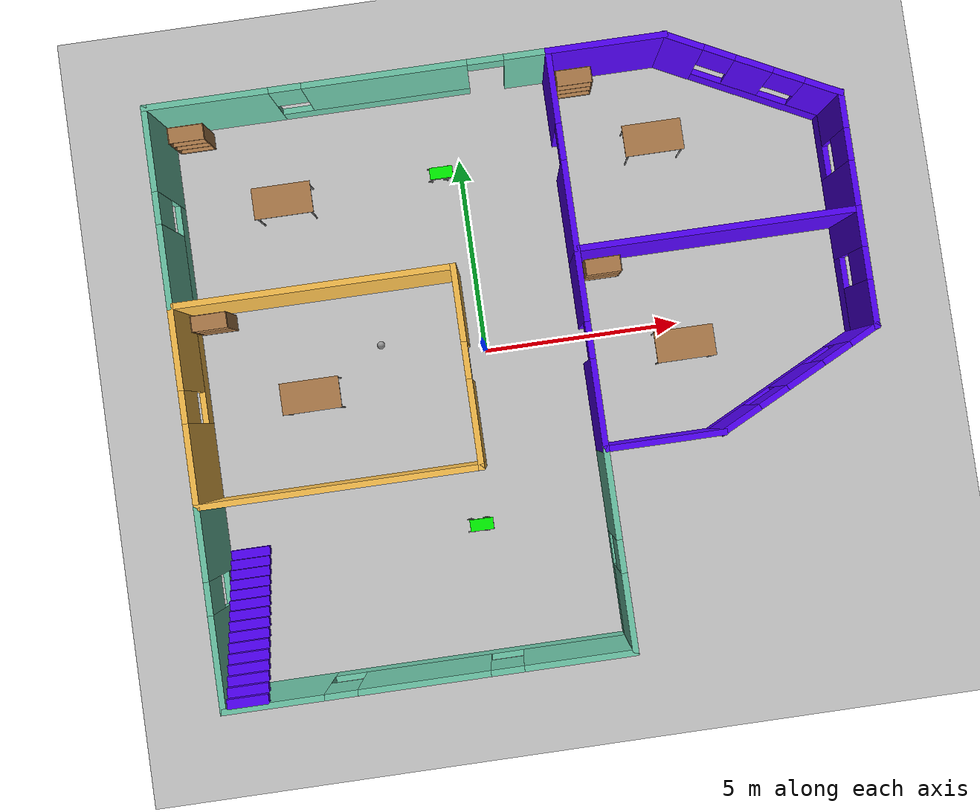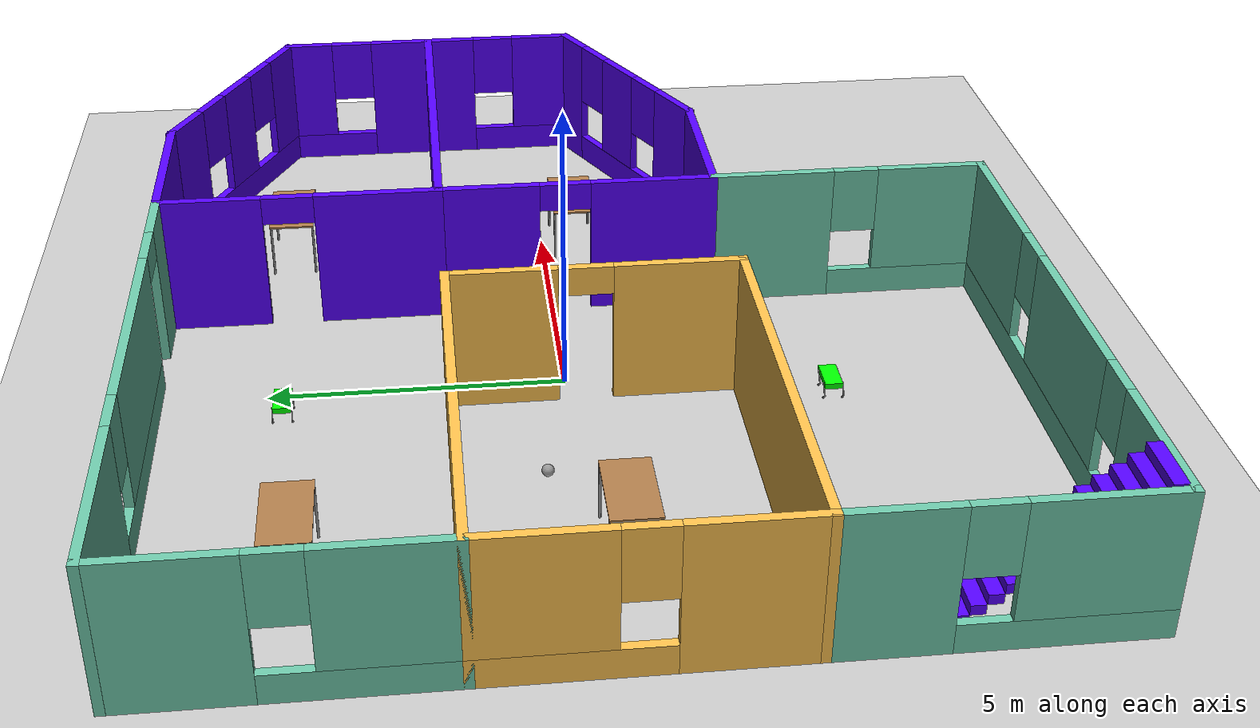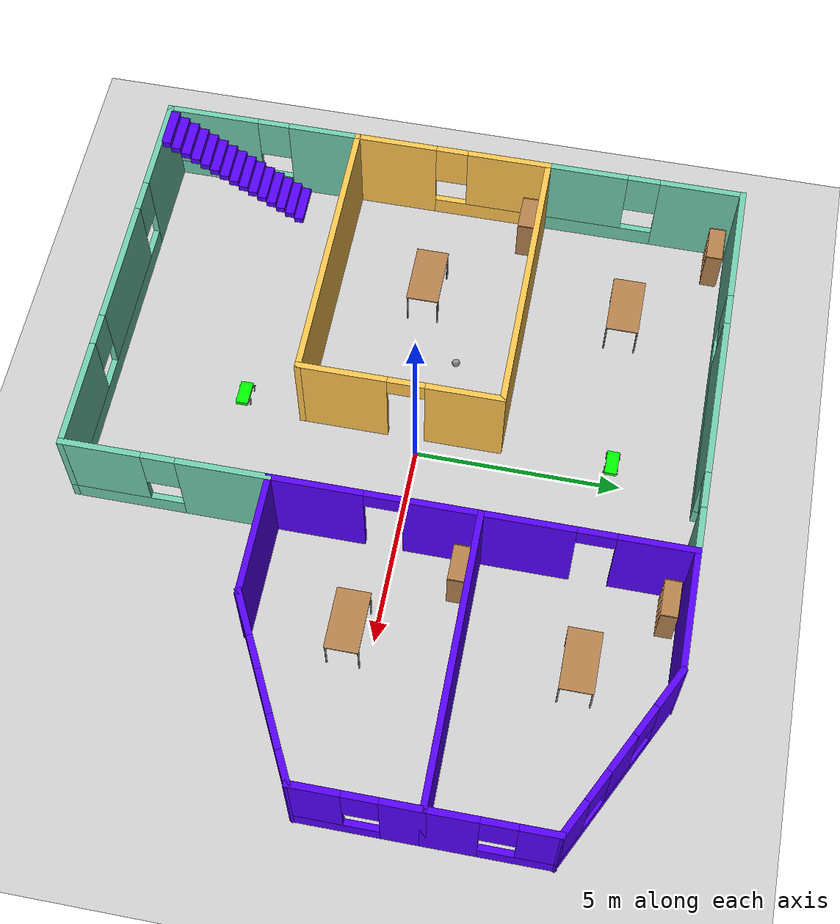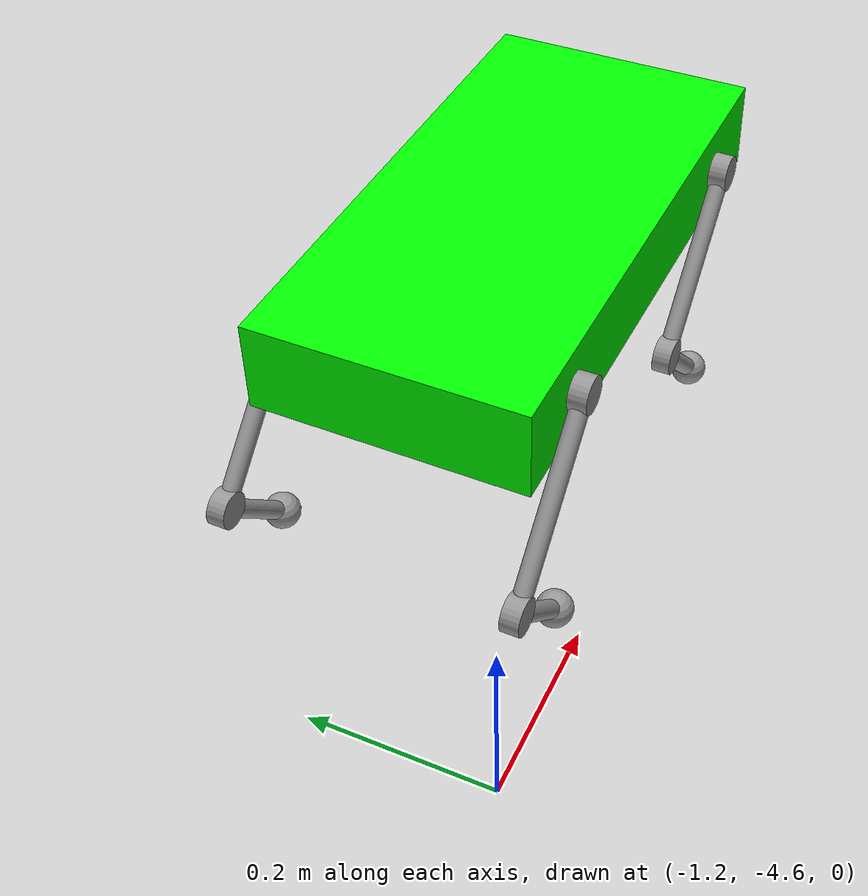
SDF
<sdf version="1.6">
 <world name="default">
  <plugin name="hello" filename="libhello.so"/>
  <light name="sun" type="directional">
   <pose>0 0 10 0 -0 0</pose>
   <diffuse>0.8 0.8 0.8 1</diffuse>
   <specular>0.2 0.2 0.2 1</specular>
   <attenuation>
    <range>1000</range>
    <constant>0.9</constant>
    <linear>0.01</linear>
    <quadratic>0.001</quadratic>
   </attenuation>
   <direction>-0.5 0.1 -0.9</direction>
  </light>
  <model name="ground_plane">
   <static>1</static>
   <link name="link">
    <collision name="collision">
     <geometry><plane><normal>0 0 1</normal><size>100 100</size></plane></geometry>
     <surface><friction><ode><mu>100</mu><mu2>50</mu2></ode></friction></surface>
    </collision>
    <visual name="visual">
     <cast_shadows>0</cast_shadows>
     <geometry><plane><normal>0 0 1</normal><size>100 100</size></plane></geometry>
     <material>
      <script><uri>file://media/materials/scripts/gazebo.material</uri><name>Gazebo/Grey</name></script>
     </material>
    </visual>
   </link>
  </model>
  <gravity>0 0 -9.8</gravity>
  <magnetic_field>6e-06 2.3e-05 -4.2e-05</magnetic_field>
  <atmosphere type="adiabatic"/>
  <physics name="default_physics" default="0" type="ode">
   <max_step_size>0.001</max_step_size>
   <real_time_factor>1</real_time_factor>
   <real_time_update_rate>1000</real_time_update_rate>
  </physics>
  <scene><ambient>0.4 0.4 0.4 1</ambient><background>0.7 0.7 0.7 1</background><shadows>1</shadows></scene>
  <spherical_coordinates>
   <surface_model>EARTH_WGS84</surface_model>
   <latitude_deg>0</latitude_deg>
   <longitude_deg>0</longitude_deg>
   <elevation>0</elevation>
   <heading_deg>0</heading_deg>
  </spherical_coordinates>
  <model name="building">
   <pose>1.04082 -0.442603 0 0 -0 0</pose>
   <link name="Stairs_0">
    <visual name="Stairs_0_Visual_0">
     <pose>-7.75322 -3.8606 0.083333 0 -0 0</pose>
     <geometry><box><size>1 0.233333 0.166667</size></box></geometry>
     <material>
      <script><uri>file://media/materials/scripts/gazebo.material</uri><name>Gazebo/Grey</name></script>
      <ambient>0.333333 0 1 1</ambient>
     </material>
     <meta><layer>0</layer></meta>
    </visual>
    <collision name="Stairs_0_Collision_0">
     <geometry><box><size>1 0.233333 0.166667</size></box></geometry>
     <pose>-7.75322 -3.8606 0.083333 0 -0 0</pose>
    </collision>
    <visual name="Stairs_0_Visual_1">
     <pose>-7.75322 -4.09394 0.25 0 -0 0</pose>
     <geometry><box><size>1 0.233333 0.166667</size></box></geometry>
     <material>
      <script><uri>file://media/materials/scripts/gazebo.material</uri><name>Gazebo/Grey</name></script>
      <ambient>0.333333 0 1 1</ambient>
     </material>
     <meta><layer>0</layer></meta>
    </visual>
    <collision name="Stairs_0_Collision_1">
     <geometry><box><size>1 0.233333 0.166667</size></box></geometry>
     <pose>-7.75322 -4.09394 0.25 0 -0 0</pose>
    </collision>
    <visual name="Stairs_0_Visual_2">
     <pose>-7.75322 -4.32727 0.416667 0 -0 0</pose>
     <geometry><box><size>1 0.233333 0.166667</size></box></geometry>
     <material>
      <script><uri>file://media/materials/scripts/gazebo.material</uri><name>Gazebo/Grey</name></script>
      <ambient>0.333333 0 1 1</ambient>
     </material>
     <meta><layer>0</layer></meta>
    </visual>
    <collision name="Stairs_0_Collision_2">
     <geometry><box><size>1 0.233333 0.166667</size></box></geometry>
     <pose>-7.75322 -4.32727 0.416667 0 -0 0</pose>
    </collision>
    <visual name="Stairs_0_Visual_3">
     <pose>-7.75322 -4.5606 0.583333 0 -0 0</pose>
     <geometry><box><size>1 0.233333 0.166667</size></box></geometry>
     <material>
      <script><uri>file://media/materials/scripts/gazebo.material</uri><name>Gazebo/Grey</name></script>
      <ambient>0.333333 0 1 1</ambient>
     </material>
     <meta><layer>0</layer></meta>
    </visual>
    <collision name="Stairs_0_Collision_3">
     <geometry><box><size>1 0.233333 0.166667</size></box></geometry>
     <pose>-7.75322 -4.5606 0.583333 0 -0 0</pose>
    </collision>
    <visual name="Stairs_0_Visual_4">
     <pose>-7.75322 -4.79394 0.75 0 -0 0</pose>
     <geometry><box><size>1 0.233333 0.166667</size></box></geometry>
     <material>
      <script><uri>file://media/materials/scripts/gazebo.material</uri><name>Gazebo/Grey</name></script>
      <ambient>0.333333 0 1 1</ambient>
     </material>
     <meta><layer>0</layer></meta>
    </visual>
    <collision name="Stairs_0_Collision_4">
     <geometry><box><size>1 0.233333 0.166667</size></box></geometry>
     <pose>-7.75322 -4.79394 0.75 0 -0 0</pose>
    </collision>
    <visual name="Stairs_0_Visual_5">
     <pose>-7.75322 -5.02727 0.916667 0 -0 0</pose>
     <geometry><box><size>1 0.233333 0.166667</size></box></geometry>
     <material>
      <script><uri>file://media/materials/scripts/gazebo.material</uri><name>Gazebo/Grey</name></script>
      <ambient>0.333333 0 1 1</ambient>
     </material>
     <meta><layer>0</layer></meta>
    </visual>
    <collision name="Stairs_0_Collision_5">
     <geometry><box><size>1 0.233333 0.166667</size></box></geometry>
     <pose>-7.75322 -5.02727 0.916667 0 -0 0</pose>
    </collision>
    <visual name="Stairs_0_Visual_6">
     <pose>-7.75322 -5.2606 1.08333 0 -0 0</pose>
     <geometry><box><size>1 0.233333 0.166667</size></box></geometry>
     <material>
      <script><uri>file://media/materials/scripts/gazebo.material</uri><name>Gazebo/Grey</name></script>
      <ambient>0.333333 0 1 1</ambient>
     </material>
     <meta><layer>0</layer></meta>
    </visual>
    <collision name="Stairs_0_Collision_6">
     <geometry><box><size>1 0.233333 0.166667</size></box></geometry>
     <pose>-7.75322 -5.2606 1.08333 0 -0 0</pose>
    </collision>
    <visual name="Stairs_0_Visual_7">
     <pose>-7.75322 -5.49394 1.25 0 -0 0</pose>
     <geometry><box><size>1 0.233333 0.166667</size></box></geometry>
     <material>
      <script><uri>file://media/materials/scripts/gazebo.material</uri><name>Gazebo/Grey</name></script>
      <ambient>0.333333 0 1 1</ambient>
     </material>
     <meta><layer>0</layer></meta>
    </visual>
    <collision name="Stairs_0_Collision_7">
     <geometry><box><size>1 0.233333 0.166667</size></box></geometry>
     <pose>-7.75322 -5.49394 1.25 0 -0 0</pose>
    </collision>
    <visual name="Stairs_0_Visual_8">
     <pose>-7.75322 -5.72727 1.41667 0 -0 0</pose>
     <geometry><box><size>1 0.233333 0.166667</size></box></geometry>
     <material>
      <script><uri>file://media/materials/scripts/gazebo.material</uri><name>Gazebo/Grey</name></script>
      <ambient>0.333333 0 1 1</ambient>
     </material>
     <meta><layer>0</layer></meta>
    </visual>
    <collision name="Stairs_0_Collision_8">
     <geometry><box><size>1 0.233333 0.166667</size></box></geometry>
     <pose>-7.75322 -5.72727 1.41667 0 -0 0</pose>
    </collision>
    <visual name="Stairs_0_Visual_9">
     <pose>-7.75322 -5.9606 1.58333 0 -0 0</pose>
     <geometry><box><size>1 0.233333 0.166667</size></box></geometry>
     <material>
      <script><uri>file://media/materials/scripts/gazebo.material</uri><name>Gazebo/Grey</name></script>
      <ambient>0.333333 0 1 1</ambient>
     </material>
     <meta><layer>0</layer></meta>
    </visual>
    <collision name="Stairs_0_Collision_9">
     <geometry><box><size>1 0.233333 0.166667</size></box></geometry>
     <pose>-7.75322 -5.9606 1.58333 0 -0 0</pose>
    </collision>
    <visual name="Stairs_0_Visual_10">
     <pose>-7.75322 -6.19394 1.75 0 -0 0</pose>
     <geometry><box><size>1 0.233333 0.166667</size></box></geometry>
     <material>
      <script><uri>file://media/materials/scripts/gazebo.material</uri><name>Gazebo/Grey</name></script>
      <ambient>0.333333 0 1 1</ambient>
     </material>
     <meta><layer>0</layer></meta>
    </visual>
    <collision name="Stairs_0_Collision_10">
     <geometry><box><size>1 0.233333 0.166667</size></box></geometry>
     <pose>-7.75322 -6.19394 1.75 0 -0 0</pose>
    </collision>
    <visual name="Stairs_0_Visual_11">
     <pose>-7.75322 -6.42727 1.91667 0 -0 0</pose>
     <geometry><box><size>1 0.233333 0.166667</size></box></geometry>
     <material>
      <script><uri>file://media/materials/scripts/gazebo.material</uri><name>Gazebo/Grey</name></script>
      <ambient>0.333333 0 1 1</ambient>
     </material>
     <meta><layer>0</layer></meta>
    </visual>
    <collision name="Stairs_0_Collision_11">
     <geometry><box><size>1 0.233333 0.166667</size></box></geometry>
     <pose>-7.75322 -6.42727 1.91667 0 -0 0</pose>
    </collision>
    <visual name="Stairs_0_Visual_12">
     <pose>-7.75322 -6.6606 2.08333 0 -0 0</pose>
     <geometry><box><size>1 0.233333 0.166667</size></box></geometry>
     <material>
      <script><uri>file://media/materials/scripts/gazebo.material</uri><name>Gazebo/Grey</name></script>
      <ambient>0.333333 0 1 1</ambient>
     </material>
     <meta><layer>0</layer></meta>
    </visual>
    <collision name="Stairs_0_Collision_12">
     <geometry><box><size>1 0.233333 0.166667</size></box></geometry>
     <pose>-7.75322 -6.6606 2.08333 0 -0 0</pose>
    </collision>
    <visual name="Stairs_0_Visual_13">
     <pose>-7.75322 -6.89394 2.25 0 -0 0</pose>
     <geometry><box><size>1 0.233333 0.166667</size></box></geometry>
     <material>
      <script><uri>file://media/materials/scripts/gazebo.material</uri><name>Gazebo/Grey</name></script>
      <ambient>0.333333 0 1 1</ambient>
     </material>
     <meta><layer>0</layer></meta>
    </visual>
    <collision name="Stairs_0_Collision_13">
     <geometry><box><size>1 0.233333 0.166667</size></box></geometry>
     <pose>-7.75322 -6.89394 2.25 0 -0 0</pose>
    </collision>
    <visual name="Stairs_0_Visual_14">
     <pose>-7.75322 -7.12727 2.41667 0 -0 0</pose>
     <geometry><box><size>1 0.233333 0.166667</size></box></geometry>
     <material>
      <script><uri>file://media/materials/scripts/gazebo.material</uri><name>Gazebo/Grey</name></script>
      <ambient>0.333333 0 1 1</ambient>
     </material>
     <meta><layer>0</layer></meta>
    </visual>
    <collision name="Stairs_0_Collision_14">
     <geometry><box><size>1 0.233333 0.166667</size></box></geometry>
     <pose>-7.75322 -7.12727 2.41667 0 -0 0</pose>
    </collision>
   </link>
   <link name="Wall_11">
    <pose>-8.36281 -4.86281 0 0 0 -1.5708</pose>
    <visual name="Wall_11_Visual_0">
     <pose>-1.578 0 1.25 0 -0 0</pose>
     <geometry><box><size>1.84401 0.15 2.5</size></box></geometry>
     <material>
      <script><uri>file://media/materials/scripts/gazebo.material</uri><name>Gazebo/Grey</name></script>
      <ambient>0.435294 0.796078 0.67451 1</ambient>
     </material>
     <meta><layer>0</layer></meta>
    </visual>
    <collision name="Wall_11_Collision_0">
     <geometry><box><size>1.84401 0.15 2.5</size></box></geometry>
     <pose>-1.578 0 1.25 0 -0 0</pose>
    </collision>
    <visual name="Wall_11_Visual_1">
     <pose>0.922004 0 0.25 0 -0 0</pose>
     <geometry><box><size>3.15599 0.15 0.5</size></box></geometry>
     <material>
      <script><uri>file://media/materials/scripts/gazebo.material</uri><name>Gazebo/Grey</name></script>
      <ambient>0.435294 0.796078 0.67451 1</ambient>
     </material>
     <meta><layer>0</layer></meta>
    </visual>
    <collision name="Wall_11_Collision_1">
     <geometry><box><size>3.15599 0.15 0.5</size></box></geometry>
     <pose>0.922004 0 0.25 0 -0 0</pose>
    </collision>
    <visual name="Wall_11_Visual_2">
     <pose>1.322 0 1.5 0 -0 0</pose>
     <geometry><box><size>2.35599 0.15 2</size></box></geometry>
     <material>
      <script><uri>file://media/materials/scripts/gazebo.material</uri><name>Gazebo/Grey</name></script>
      <ambient>0.435294 0.796078 0.67451 1</ambient>
     </material>
     <meta><layer>0</layer></meta>
    </visual>
    <collision name="Wall_11_Collision_2">
     <geometry><box><size>2.35599 0.15 2</size></box></geometry>
     <pose>1.322 0 1.5 0 -0 0</pose>
    </collision>
    <visual name="Wall_11_Visual_3">
     <pose>-0.255991 0 1.9 0 -0 0</pose>
     <geometry><box><size>0.8 0.15 1.2</size></box></geometry>
     <material>
      <script><uri>file://media/materials/scripts/gazebo.material</uri><name>Gazebo/Grey</name></script>
      <ambient>0.435294 0.796078 0.67451 1</ambient>
     </material>
     <meta><layer>0</layer></meta>
    </visual>
    <collision name="Wall_11_Collision_3">
     <geometry><box><size>0.8 0.15 1.2</size></box></geometry>
     <pose>-0.255991 0 1.9 0 -0 0</pose>
    </collision>
   </link>
   <link name="Wall_12">
    <pose>-3.43781 -7.28781 0 0 -0 0</pose>
    <visual name="Wall_12_Visual_0">
     <pose>-3.75645 0 1.25 0 -0 0</pose>
     <geometry><box><size>2.48709 0.15 2.5</size></box></geometry>
     <material>
      <script><uri>file://media/materials/scripts/gazebo.material</uri><name>Gazebo/Grey</name></script>
      <ambient>0.435294 0.796078 0.67451 1</ambient>
     </material>
     <meta><layer>0</layer></meta>
    </visual>
    <collision name="Wall_12_Collision_0">
     <geometry><box><size>2.48709 0.15 2.5</size></box></geometry>
     <pose>-3.75645 0 1.25 0 -0 0</pose>
    </collision>
    <visual name="Wall_12_Visual_1">
     <pose>1.24354 0 0.25 0 -0 0</pose>
     <geometry><box><size>7.51291 0.15 0.5</size></box></geometry>
     <material>
      <script><uri>file://media/materials/scripts/gazebo.material</uri><name>Gazebo/Grey</name></script>
      <ambient>0.435294 0.796078 0.67451 1</ambient>
     </material>
     <meta><layer>0</layer></meta>
    </visual>
    <collision name="Wall_12_Collision_1">
     <geometry><box><size>7.51291 0.15 0.5</size></box></geometry>
     <pose>1.24354 0 0.25 0 -0 0</pose>
    </collision>
    <visual name="Wall_12_Visual_2">
     <pose>-0.124545 0 1.5 0 -0 0</pose>
     <geometry><box><size>3.17673 0.15 2</size></box></geometry>
     <material>
      <script><uri>file://media/materials/scripts/gazebo.material</uri><name>Gazebo/Grey</name></script>
      <ambient>0.435294 0.796078 0.67451 1</ambient>
     </material>
     <meta><layer>0</layer></meta>
    </visual>
    <collision name="Wall_12_Collision_2">
     <geometry><box><size>3.17673 0.15 2</size></box></geometry>
     <pose>-0.124545 0 1.5 0 -0 0</pose>
    </collision>
    <visual name="Wall_12_Visual_3">
     <pose>3.63191 0 1.5 0 -0 0</pose>
     <geometry><box><size>2.73618 0.15 2</size></box></geometry>
     <material>
      <script><uri>file://media/materials/scripts/gazebo.material</uri><name>Gazebo/Grey</name></script>
      <ambient>0.435294 0.796078 0.67451 1</ambient>
     </material>
     <meta><layer>0</layer></meta>
    </visual>
    <collision name="Wall_12_Collision_3">
     <geometry><box><size>2.73618 0.15 2</size></box></geometry>
     <pose>3.63191 0 1.5 0 -0 0</pose>
    </collision>
    <visual name="Wall_12_Visual_4">
     <pose>-2.11291 0 1.9 0 -0 0</pose>
     <geometry><box><size>0.8 0.15 1.2</size></box></geometry>
     <material>
      <script><uri>file://media/materials/scripts/gazebo.material</uri><name>Gazebo/Grey</name></script>
      <ambient>0.435294 0.796078 0.67451 1</ambient>
     </material>
     <meta><layer>0</layer></meta>
    </visual>
    <collision name="Wall_12_Collision_4">
     <geometry><box><size>0.8 0.15 1.2</size></box></geometry>
     <pose>-2.11291 0 1.9 0 -0 0</pose>
    </collision>
    <visual name="Wall_12_Visual_5">
     <pose>1.86382 0 1.9 0 -0 0</pose>
     <geometry><box><size>0.8 0.15 1.2</size></box></geometry>
     <material>
      <script><uri>file://media/materials/scripts/gazebo.material</uri><name>Gazebo/Grey</name></script>
      <ambient>0.435294 0.796078 0.67451 1</ambient>
     </material>
     <meta><layer>0</layer></meta>
    </visual>
    <collision name="Wall_12_Collision_5">
     <geometry><box><size>0.8 0.15 1.2</size></box></geometry>
     <pose>1.86382 0 1.9 0 -0 0</pose>
    </collision>
   </link>
   <link name="Wall_15">
    <pose>-3.43781 7.26219 0 0 -0 0</pose>
    <visual name="Wall_15_Visual_0">
     <pose>-3.45055 0 1.25 0 -0 0</pose>
     <geometry><box><size>3.09889 0.15 2.5</size></box></geometry>
     <material>
      <script><uri>file://media/materials/scripts/gazebo.material</uri><name>Gazebo/Grey</name></script>
      <ambient>0.435294 0.796078 0.67451 1</ambient>
     </material>
     <meta><layer>0</layer></meta>
    </visual>
    <collision name="Wall_15_Collision_0">
     <geometry><box><size>3.09889 0.15 2.5</size></box></geometry>
     <pose>-3.45055 0 1.25 0 -0 0</pose>
    </collision>
    <visual name="Wall_15_Visual_1">
     <pose>4.42166 0 1.25 0 -0 0</pose>
     <geometry><box><size>1.15667 0.15 2.5</size></box></geometry>
     <material>
      <script><uri>file://media/materials/scripts/gazebo.material</uri><name>Gazebo/Grey</name></script>
      <ambient>0.435294 0.796078 0.67451 1</ambient>
     </material>
     <meta><layer>0</layer></meta>
    </visual>
    <collision name="Wall_15_Collision_1">
     <geometry><box><size>1.15667 0.15 2.5</size></box></geometry>
     <pose>4.42166 0 1.25 0 -0 0</pose>
    </collision>
    <visual name="Wall_15_Visual_2">
     <pose>0.521113 0 0.25 0 -0 0</pose>
     <geometry><box><size>4.84444 0.15 0.5</size></box></geometry>
     <material>
      <script><uri>file://media/materials/scripts/gazebo.material</uri><name>Gazebo/Grey</name></script>
      <ambient>0.435294 0.796078 0.67451 1</ambient>
     </material>
     <meta><layer>0</layer></meta>
    </visual>
    <collision name="Wall_15_Collision_2">
     <geometry><box><size>4.84444 0.15 0.5</size></box></geometry>
     <pose>0.521113 0 0.25 0 -0 0</pose>
    </collision>
    <visual name="Wall_15_Visual_3">
     <pose>0.921113 0 1.5 0 -0 0</pose>
     <geometry><box><size>4.04444 0.15 2</size></box></geometry>
     <material>
      <script><uri>file://media/materials/scripts/gazebo.material</uri><name>Gazebo/Grey</name></script>
      <ambient>0.435294 0.796078 0.67451 1</ambient>
     </material>
     <meta><layer>0</layer></meta>
    </visual>
    <collision name="Wall_15_Collision_3">
     <geometry><box><size>4.04444 0.15 2</size></box></geometry>
     <pose>0.921113 0 1.5 0 -0 0</pose>
    </collision>
    <visual name="Wall_15_Visual_4">
     <pose>-1.50111 0 1.9 0 -0 0</pose>
     <geometry><box><size>0.8 0.15 1.2</size></box></geometry>
     <material>
      <script><uri>file://media/materials/scripts/gazebo.material</uri><name>Gazebo/Grey</name></script>
      <ambient>0.435294 0.796078 0.67451 1</ambient>
     </material>
     <meta><layer>0</layer></meta>
    </visual>
    <collision name="Wall_15_Collision_4">
     <geometry><box><size>0.8 0.15 1.2</size></box></geometry>
     <pose>-1.50111 0 1.9 0 -0 0</pose>
    </collision>
    <visual name="Wall_15_Visual_5">
     <pose>3.39333 0 2.25 0 -0 0</pose>
     <geometry><box><size>0.9 0.15 0.5</size></box></geometry>
     <material>
      <script><uri>file://media/materials/scripts/gazebo.material</uri><name>Gazebo/Grey</name></script>
      <ambient>0.435294 0.796078 0.67451 1</ambient>
     </material>
     <meta><layer>0</layer></meta>
    </visual>
    <collision name="Wall_15_Collision_5">
     <geometry><box><size>0.9 0.15 0.5</size></box></geometry>
     <pose>3.39333 0 2.25 0 -0 0</pose>
    </collision>
   </link>
   <link name="Wall_20">
    <pose>1.48719 4.83719 0 0 0 -1.5708</pose>
    <visual name="Wall_20_Visual_0">
     <pose>-1.57096 0 1.25 0 -0 0</pose>
     <geometry><box><size>1.85809 0.15 2.5</size></box></geometry>
     <material>
      <script><uri>file://media/materials/scripts/gazebo.material</uri><name>Gazebo/Grey</name></script>
      <ambient>0.333333 0 1 1</ambient>
     </material>
     <meta><layer>0</layer></meta>
    </visual>
    <collision name="Wall_20_Collision_0">
     <geometry><box><size>1.85809 0.15 2.5</size></box></geometry>
     <pose>-1.57096 0 1.25 0 -0 0</pose>
    </collision>
    <visual name="Wall_20_Visual_1">
     <pose>1.37904 0 1.25 0 -0 0</pose>
     <geometry><box><size>2.24191 0.15 2.5</size></box></geometry>
     <material>
      <script><uri>file://media/materials/scripts/gazebo.material</uri><name>Gazebo/Grey</name></script>
      <ambient>0.333333 0 1 1</ambient>
     </material>
     <meta><layer>0</layer></meta>
    </visual>
    <collision name="Wall_20_Collision_1">
     <geometry><box><size>2.24191 0.15 2.5</size></box></geometry>
     <pose>1.37904 0 1.25 0 -0 0</pose>
    </collision>
    <visual name="Wall_20_Visual_2">
     <pose>-0.191914 0 2.25 0 -0 0</pose>
     <geometry><box><size>0.9 0.15 0.5</size></box></geometry>
     <material>
      <script><uri>file://media/materials/scripts/gazebo.material</uri><name>Gazebo/Grey</name></script>
      <ambient>0.333333 0 1 1</ambient>
     </material>
     <meta><layer>0</layer></meta>
    </visual>
    <collision name="Wall_20_Collision_2">
     <geometry><box><size>0.9 0.15 0.5</size></box></geometry>
     <pose>-0.191914 0 2.25 0 -0 0</pose>
    </collision>
   </link>
   <link name="Wall_21">
    <collision name="Wall_21_Collision">
     <geometry><box><size>7 0.15 2.5</size></box></geometry>
     <pose>0 0 1.25 0 -0 0</pose>
    </collision>
    <visual name="Wall_21_Visual">
     <pose>0 0 1.25 0 -0 0</pose>
     <geometry><box><size>7 0.15 2.5</size></box></geometry>
     <material>
      <script><uri>file://media/materials/scripts/gazebo.material</uri><name>Gazebo/Grey</name></script>
      <ambient>0.333333 0 1 1</ambient>
     </material>
     <meta><layer>0</layer></meta>
    </visual>
    <pose>4.91219 2.41219 0 0 -0 0</pose>
   </link>
   <link name="Wall_22">
    <pose>8.33719 3.83719 0 0 -0 1.5708</pose>
    <visual name="Wall_22_Visual_0">
     <pose>-0.874077 0 1.25 0 -0 0</pose>
     <geometry><box><size>1.25185 0.15 2.5</size></box></geometry>
     <material>
      <script><uri>file://media/materials/scripts/gazebo.material</uri><name>Gazebo/Grey</name></script>
      <ambient>0.333333 0 1 1</ambient>
     </material>
     <meta><layer>0</layer></meta>
    </visual>
    <collision name="Wall_22_Collision_0">
     <geometry><box><size>1.25185 0.15 2.5</size></box></geometry>
     <pose>-0.874077 0 1.25 0 -0 0</pose>
    </collision>
    <visual name="Wall_22_Visual_1">
     <pose>0.625923 0 0.25 0 -0 0</pose>
     <geometry><box><size>1.74815 0.15 0.5</size></box></geometry>
     <material>
      <script><uri>file://media/materials/scripts/gazebo.material</uri><name>Gazebo/Grey</name></script>
      <ambient>0.333333 0 1 1</ambient>
     </material>
     <meta><layer>0</layer></meta>
    </visual>
    <collision name="Wall_22_Collision_1">
     <geometry><box><size>1.74815 0.15 0.5</size></box></geometry>
     <pose>0.625923 0 0.25 0 -0 0</pose>
    </collision>
    <visual name="Wall_22_Visual_2">
     <pose>1.02592 0 1.5 0 -0 0</pose>
     <geometry><box><size>0.948155 0.15 2</size></box></geometry>
     <material>
      <script><uri>file://media/materials/scripts/gazebo.material</uri><name>Gazebo/Grey</name></script>
      <ambient>0.333333 0 1 1</ambient>
     </material>
     <meta><layer>0</layer></meta>
    </visual>
    <collision name="Wall_22_Collision_2">
     <geometry><box><size>0.948155 0.15 2</size></box></geometry>
     <pose>1.02592 0 1.5 0 -0 0</pose>
    </collision>
    <visual name="Wall_22_Visual_3">
     <pose>0.151845 0 1.9 0 -0 0</pose>
     <geometry><box><size>0.8 0.15 1.2</size></box></geometry>
     <material>
      <script><uri>file://media/materials/scripts/gazebo.material</uri><name>Gazebo/Grey</name></script>
      <ambient>0.333333 0 1 1</ambient>
     </material>
     <meta><layer>0</layer></meta>
    </visual>
    <collision name="Wall_22_Collision_3">
     <geometry><box><size>0.8 0.15 1.2</size></box></geometry>
     <pose>0.151845 0 1.9 0 -0 0</pose>
    </collision>
   </link>
   <link name="Wall_24">
    <collision name="Wall_24_Collision">
     <geometry><box><size>3 0.15 2.5</size></box></geometry>
     <pose>0 0 1.25 0 -0 0</pose>
    </collision>
    <visual name="Wall_24_Visual">
     <pose>0 0 1.25 0 -0 0</pose>
     <geometry><box><size>3 0.15 2.5</size></box></geometry>
     <material>
      <script><uri>file://media/materials/scripts/gazebo.material</uri><name>Gazebo/Grey</name></script>
      <ambient>0.333333 0 1 1</ambient>
     </material>
     <meta><layer>0</layer></meta>
    </visual>
    <pose>2.91219 7.26219 0 0 -0 0</pose>
   </link>
   <link name="Wall_25">
    <pose>6.33719 6.26219 0 0 0 -0.463648</pose>
    <visual name="Wall_25_Visual_0">
     <pose>-1.77228 0 1.25 0 -0 0</pose>
     <geometry><box><size>1.07758 0.15 2.5</size></box></geometry>
     <material>
      <script><uri>file://media/materials/scripts/gazebo.material</uri><name>Gazebo/Grey</name></script>
      <ambient>0.333333 0 1 1</ambient>
     </material>
     <meta><layer>0</layer></meta>
    </visual>
    <collision name="Wall_25_Collision_0">
     <geometry><box><size>1.07758 0.15 2.5</size></box></geometry>
     <pose>-1.77228 0 1.25 0 -0 0</pose>
    </collision>
    <visual name="Wall_25_Visual_1">
     <pose>0.538789 0 0.25 0 -0 0</pose>
     <geometry><box><size>3.54456 0.15 0.5</size></box></geometry>
     <material>
      <script><uri>file://media/materials/scripts/gazebo.material</uri><name>Gazebo/Grey</name></script>
      <ambient>0.333333 0 1 1</ambient>
     </material>
     <meta><layer>0</layer></meta>
    </visual>
    <collision name="Wall_25_Collision_1">
     <geometry><box><size>3.54456 0.15 0.5</size></box></geometry>
     <pose>0.538789 0 0.25 0 -0 0</pose>
    </collision>
    <visual name="Wall_25_Visual_2">
     <pose>0.048894 0 1.5 0 -0 0</pose>
     <geometry><box><size>0.964767 0.15 2</size></box></geometry>
     <material>
      <script><uri>file://media/materials/scripts/gazebo.material</uri><name>Gazebo/Grey</name></script>
      <ambient>0.333333 0 1 1</ambient>
     </material>
     <meta><layer>0</layer></meta>
    </visual>
    <collision name="Wall_25_Collision_2">
     <geometry><box><size>0.964767 0.15 2</size></box></geometry>
     <pose>0.048894 0 1.5 0 -0 0</pose>
    </collision>
    <visual name="Wall_25_Visual_3">
     <pose>1.82117 0 1.5 0 -0 0</pose>
     <geometry><box><size>0.97979 0.15 2</size></box></geometry>
     <material>
      <script><uri>file://media/materials/scripts/gazebo.material</uri><name>Gazebo/Grey</name></script>
      <ambient>0.333333 0 1 1</ambient>
     </material>
     <meta><layer>0</layer></meta>
    </visual>
    <collision name="Wall_25_Collision_3">
     <geometry><box><size>0.97979 0.15 2</size></box></geometry>
     <pose>1.82117 0 1.5 0 -0 0</pose>
    </collision>
    <visual name="Wall_25_Visual_4">
     <pose>-0.83349 0 1.9 0 -0 0</pose>
     <geometry><box><size>0.8 0.15 1.2</size></box></geometry>
     <material>
      <script><uri>file://media/materials/scripts/gazebo.material</uri><name>Gazebo/Grey</name></script>
      <ambient>0.333333 0 1 1</ambient>
     </material>
     <meta><layer>0</layer></meta>
    </visual>
    <collision name="Wall_25_Collision_4">
     <geometry><box><size>0.8 0.15 1.2</size></box></geometry>
     <pose>-0.83349 0 1.9 0 -0 0</pose>
    </collision>
    <visual name="Wall_25_Visual_5">
     <pose>0.931278 0 1.9 0 -0 0</pose>
     <geometry><box><size>0.8 0.15 1.2</size></box></geometry>
     <material>
      <script><uri>file://media/materials/scripts/gazebo.material</uri><name>Gazebo/Grey</name></script>
      <ambient>0.333333 0 1 1</ambient>
     </material>
     <meta><layer>0</layer></meta>
    </visual>
    <collision name="Wall_25_Collision_5">
     <geometry><box><size>0.8 0.15 1.2</size></box></geometry>
     <pose>0.931278 0 1.9 0 -0 0</pose>
    </collision>
   </link>
   <link name="Wall_27">
    <pose>1.48719 -0.012812 0 0 0 -1.5708</pose>
    <visual name="Wall_27_Visual_0">
     <pose>-1.57933 0 1.25 0 -0 0</pose>
     <geometry><box><size>1.84134 0.15 2.5</size></box></geometry>
     <material>
      <script><uri>file://media/materials/scripts/gazebo.material</uri><name>Gazebo/Grey</name></script>
      <ambient>0.333333 0 1 1</ambient>
     </material>
     <meta><layer>0</layer></meta>
    </visual>
    <collision name="Wall_27_Collision_0">
     <geometry><box><size>1.84134 0.15 2.5</size></box></geometry>
     <pose>-1.57933 0 1.25 0 -0 0</pose>
    </collision>
    <visual name="Wall_27_Visual_1">
     <pose>1.37067 0 1.25 0 -0 0</pose>
     <geometry><box><size>2.25866 0.15 2.5</size></box></geometry>
     <material>
      <script><uri>file://media/materials/scripts/gazebo.material</uri><name>Gazebo/Grey</name></script>
      <ambient>0.333333 0 1 1</ambient>
     </material>
     <meta><layer>0</layer></meta>
    </visual>
    <collision name="Wall_27_Collision_1">
     <geometry><box><size>2.25866 0.15 2.5</size></box></geometry>
     <pose>1.37067 0 1.25 0 -0 0</pose>
    </collision>
    <visual name="Wall_27_Visual_2">
     <pose>-0.208657 0 2.25 0 -0 0</pose>
     <geometry><box><size>0.9 0.15 0.5</size></box></geometry>
     <material>
      <script><uri>file://media/materials/scripts/gazebo.material</uri><name>Gazebo/Grey</name></script>
      <ambient>0.333333 0 1 1</ambient>
     </material>
     <meta><layer>0</layer></meta>
    </visual>
    <collision name="Wall_27_Collision_2">
     <geometry><box><size>0.9 0.15 0.5</size></box></geometry>
     <pose>-0.208657 0 2.25 0 -0 0</pose>
    </collision>
   </link>
   <link name="Wall_28">
    <collision name="Wall_28_Collision">
     <geometry><box><size>3 0.15 2.5</size></box></geometry>
     <pose>0 0 1.25 0 -0 0</pose>
    </collision>
    <visual name="Wall_28_Visual">
     <pose>0 0 1.25 0 -0 0</pose>
     <geometry><box><size>3 0.15 2.5</size></box></geometry>
     <material>
      <script><uri>file://media/materials/scripts/gazebo.material</uri><name>Gazebo/Grey</name></script>
      <ambient>0.333333 0 1 1</ambient>
     </material>
     <meta><layer>0</layer></meta>
    </visual>
    <pose>2.91219 -2.43781 0 0 -0 0</pose>
   </link>
   <link name="Wall_30">
    <pose>8.33719 0.987188 0 0 0 -1.5708</pose>
    <visual name="Wall_30_Visual_0">
     <pose>-0.997887 0 1.25 0 -0 0</pose>
     <geometry><box><size>1.00423 0.15 2.5</size></box></geometry>
     <material>
      <script><uri>file://media/materials/scripts/gazebo.material</uri><name>Gazebo/Grey</name></script>
      <ambient>0.333333 0 1 1</ambient>
     </material>
     <meta><layer>0</layer></meta>
    </visual>
    <collision name="Wall_30_Collision_0">
     <geometry><box><size>1.00423 0.15 2.5</size></box></geometry>
     <pose>-0.997887 0 1.25 0 -0 0</pose>
    </collision>
    <visual name="Wall_30_Visual_1">
     <pose>0.502113 0 0.25 0 -0 0</pose>
     <geometry><box><size>1.99577 0.15 0.5</size></box></geometry>
     <material>
      <script><uri>file://media/materials/scripts/gazebo.material</uri><name>Gazebo/Grey</name></script>
      <ambient>0.333333 0 1 1</ambient>
     </material>
     <meta><layer>0</layer></meta>
    </visual>
    <collision name="Wall_30_Collision_1">
     <geometry><box><size>1.99577 0.15 0.5</size></box></geometry>
     <pose>0.502113 0 0.25 0 -0 0</pose>
    </collision>
    <visual name="Wall_30_Visual_2">
     <pose>0.902113 0 1.5 0 -0 0</pose>
     <geometry><box><size>1.19577 0.15 2</size></box></geometry>
     <material>
      <script><uri>file://media/materials/scripts/gazebo.material</uri><name>Gazebo/Grey</name></script>
      <ambient>0.333333 0 1 1</ambient>
     </material>
     <meta><layer>0</layer></meta>
    </visual>
    <collision name="Wall_30_Collision_2">
     <geometry><box><size>1.19577 0.15 2</size></box></geometry>
     <pose>0.902113 0 1.5 0 -0 0</pose>
    </collision>
    <visual name="Wall_30_Visual_3">
     <pose>-0.095774 0 1.9 0 -0 0</pose>
     <geometry><box><size>0.8 0.15 1.2</size></box></geometry>
     <material>
      <script><uri>file://media/materials/scripts/gazebo.material</uri><name>Gazebo/Grey</name></script>
      <ambient>0.333333 0 1 1</ambient>
     </material>
     <meta><layer>0</layer></meta>
    </visual>
    <collision name="Wall_30_Collision_3">
     <geometry><box><size>0.8 0.15 1.2</size></box></geometry>
     <pose>-0.095774 0 1.9 0 -0 0</pose>
    </collision>
   </link>
   <link name="Wall_31">
    <pose>6.33719 -1.43781 0 0 0 -2.67794</pose>
    <visual name="Wall_31_Visual_0">
     <pose>-1.89022 0 1.25 0 -0 0</pose>
     <geometry><box><size>0.841691 0.15 2.5</size></box></geometry>
     <material>
      <script><uri>file://media/materials/scripts/gazebo.material</uri><name>Gazebo/Grey</name></script>
      <ambient>0.333333 0 1 1</ambient>
     </material>
     <meta><layer>0</layer></meta>
    </visual>
    <collision name="Wall_31_Collision_0">
     <geometry><box><size>0.841691 0.15 2.5</size></box></geometry>
     <pose>-1.89022 0 1.25 0 -0 0</pose>
    </collision>
    <visual name="Wall_31_Visual_1">
     <pose>0.420845 0 0.25 0 -0 0</pose>
     <geometry><box><size>3.78044 0.15 0.5</size></box></geometry>
     <material>
      <script><uri>file://media/materials/scripts/gazebo.material</uri><name>Gazebo/Grey</name></script>
      <ambient>0.333333 0 1 1</ambient>
     </material>
     <meta><layer>0</layer></meta>
    </visual>
    <collision name="Wall_31_Collision_1">
     <geometry><box><size>3.78044 0.15 0.5</size></box></geometry>
     <pose>0.420845 0 0.25 0 -0 0</pose>
    </collision>
    <visual name="Wall_31_Visual_2">
     <pose>-0.145953 0 1.5 0 -0 0</pose>
     <geometry><box><size>1.04685 0.15 2</size></box></geometry>
     <material>
      <script><uri>file://media/materials/scripts/gazebo.material</uri><name>Gazebo/Grey</name></script>
      <ambient>0.333333 0 1 1</ambient>
     </material>
     <meta><layer>0</layer></meta>
    </visual>
    <collision name="Wall_31_Collision_2">
     <geometry><box><size>1.04685 0.15 2</size></box></geometry>
     <pose>-0.145953 0 1.5 0 -0 0</pose>
    </collision>
    <visual name="Wall_31_Visual_3">
     <pose>1.74427 0 1.5 0 -0 0</pose>
     <geometry><box><size>1.1336 0.15 2</size></box></geometry>
     <material>
      <script><uri>file://media/materials/scripts/gazebo.material</uri><name>Gazebo/Grey</name></script>
      <ambient>0.333333 0 1 1</ambient>
     </material>
     <meta><layer>0</layer></meta>
    </visual>
    <collision name="Wall_31_Collision_3">
     <geometry><box><size>1.1336 0.15 2</size></box></geometry>
     <pose>1.74427 0 1.5 0 -0 0</pose>
    </collision>
    <visual name="Wall_31_Visual_4">
     <pose>-1.06938 0 1.9 0 -0 0</pose>
     <geometry><box><size>0.8 0.15 1.2</size></box></geometry>
     <material>
      <script><uri>file://media/materials/scripts/gazebo.material</uri><name>Gazebo/Grey</name></script>
      <ambient>0.333333 0 1 1</ambient>
     </material>
     <meta><layer>0</layer></meta>
    </visual>
    <collision name="Wall_31_Collision_4">
     <geometry><box><size>0.8 0.15 1.2</size></box></geometry>
     <pose>-1.06938 0 1.9 0 -0 0</pose>
    </collision>
    <visual name="Wall_31_Visual_5">
     <pose>0.777472 0 1.9 0 -0 0</pose>
     <geometry><box><size>0.8 0.15 1.2</size></box></geometry>
     <material>
      <script><uri>file://media/materials/scripts/gazebo.material</uri><name>Gazebo/Grey</name></script>
      <ambient>0.333333 0 1 1</ambient>
     </material>
     <meta><layer>0</layer></meta>
    </visual>
    <collision name="Wall_31_Collision_5">
     <geometry><box><size>0.8 0.15 1.2</size></box></geometry>
     <pose>0.777472 0 1.9 0 -0 0</pose>
    </collision>
   </link>
   <link name="Wall_33">
    <pose>1.48719 -4.86281 0 0 0 -1.5708</pose>
    <visual name="Wall_33_Visual_0">
     <pose>-1.37916 0 1.25 0 -0 0</pose>
     <geometry><box><size>2.24168 0.15 2.5</size></box></geometry>
     <material>
      <script><uri>file://media/materials/scripts/gazebo.material</uri><name>Gazebo/Grey</name></script>
      <ambient>0.435294 0.796078 0.67451 1</ambient>
     </material>
     <meta><layer>0</layer></meta>
    </visual>
    <collision name="Wall_33_Collision_0">
     <geometry><box><size>2.24168 0.15 2.5</size></box></geometry>
     <pose>-1.37916 0 1.25 0 -0 0</pose>
    </collision>
    <visual name="Wall_33_Visual_1">
     <pose>1.12084 0 0.25 0 -0 0</pose>
     <geometry><box><size>2.75832 0.15 0.5</size></box></geometry>
     <material>
      <script><uri>file://media/materials/scripts/gazebo.material</uri><name>Gazebo/Grey</name></script>
      <ambient>0.435294 0.796078 0.67451 1</ambient>
     </material>
     <meta><layer>0</layer></meta>
    </visual>
    <collision name="Wall_33_Collision_1">
     <geometry><box><size>2.75832 0.15 0.5</size></box></geometry>
     <pose>1.12084 0 0.25 0 -0 0</pose>
    </collision>
    <visual name="Wall_33_Visual_2">
     <pose>1.52084 0 1.5 0 -0 0</pose>
     <geometry><box><size>1.95832 0.15 2</size></box></geometry>
     <material>
      <script><uri>file://media/materials/scripts/gazebo.material</uri><name>Gazebo/Grey</name></script>
      <ambient>0.435294 0.796078 0.67451 1</ambient>
     </material>
     <meta><layer>0</layer></meta>
    </visual>
    <collision name="Wall_33_Collision_2">
     <geometry><box><size>1.95832 0.15 2</size></box></geometry>
     <pose>1.52084 0 1.5 0 -0 0</pose>
    </collision>
    <visual name="Wall_33_Visual_3">
     <pose>0.141682 0 1.9 0 -0 0</pose>
     <geometry><box><size>0.8 0.15 1.2</size></box></geometry>
     <material>
      <script><uri>file://media/materials/scripts/gazebo.material</uri><name>Gazebo/Grey</name></script>
      <ambient>0.435294 0.796078 0.67451 1</ambient>
     </material>
     <meta><layer>0</layer></meta>
    </visual>
    <collision name="Wall_33_Collision_3">
     <geometry><box><size>0.8 0.15 1.2</size></box></geometry>
     <pose>0.141682 0 1.9 0 -0 0</pose>
    </collision>
   </link>
   <link name="Wall_4">
    <pose>-8.36281 4.83719 0 0 0 -1.5708</pose>
    <visual name="Wall_4_Visual_0">
     <pose>-1.43889 0 1.25 0 -0 0</pose>
     <geometry><box><size>2.12222 0.15 2.5</size></box></geometry>
     <material>
      <script><uri>file://media/materials/scripts/gazebo.material</uri><name>Gazebo/Grey</name></script>
      <ambient>0.435294 0.796078 0.67451 1</ambient>
     </material>
     <meta><layer>0</layer></meta>
    </visual>
    <collision name="Wall_4_Collision_0">
     <geometry><box><size>2.12222 0.15 2.5</size></box></geometry>
     <pose>-1.43889 0 1.25 0 -0 0</pose>
    </collision>
    <visual name="Wall_4_Visual_1">
     <pose>1.06111 0 0.25 0 -0 0</pose>
     <geometry><box><size>2.87778 0.15 0.5</size></box></geometry>
     <material>
      <script><uri>file://media/materials/scripts/gazebo.material</uri><name>Gazebo/Grey</name></script>
      <ambient>0.435294 0.796078 0.67451 1</ambient>
     </material>
     <meta><layer>0</layer></meta>
    </visual>
    <collision name="Wall_4_Collision_1">
     <geometry><box><size>2.87778 0.15 0.5</size></box></geometry>
     <pose>1.06111 0 0.25 0 -0 0</pose>
    </collision>
    <visual name="Wall_4_Visual_2">
     <pose>1.46111 0 1.5 0 -0 0</pose>
     <geometry><box><size>2.07778 0.15 2</size></box></geometry>
     <material>
      <script><uri>file://media/materials/scripts/gazebo.material</uri><name>Gazebo/Grey</name></script>
      <ambient>0.435294 0.796078 0.67451 1</ambient>
     </material>
     <meta><layer>0</layer></meta>
    </visual>
    <collision name="Wall_4_Collision_2">
     <geometry><box><size>2.07778 0.15 2</size></box></geometry>
     <pose>1.46111 0 1.5 0 -0 0</pose>
    </collision>
    <visual name="Wall_4_Visual_3">
     <pose>0.022218 0 1.9 0 -0 0</pose>
     <geometry><box><size>0.8 0.15 1.2</size></box></geometry>
     <material>
      <script><uri>file://media/materials/scripts/gazebo.material</uri><name>Gazebo/Grey</name></script>
      <ambient>0.435294 0.796078 0.67451 1</ambient>
     </material>
     <meta><layer>0</layer></meta>
    </visual>
    <collision name="Wall_4_Collision_3">
     <geometry><box><size>0.8 0.15 1.2</size></box></geometry>
     <pose>0.022218 0 1.9 0 -0 0</pose>
    </collision>
   </link>
   <link name="Wall_6">
    <collision name="Wall_6_Collision">
     <geometry><box><size>7 0.15 2.5</size></box></geometry>
     <pose>0 0 1.25 0 -0 0</pose>
    </collision>
    <visual name="Wall_6_Visual">
     <pose>0 0 1.25 0 -0 0</pose>
     <geometry><box><size>7 0.15 2.5</size></box></geometry>
     <material>
      <script><uri>file://media/materials/scripts/gazebo.material</uri><name>Gazebo/Grey</name></script>
      <ambient>1 0.764706 0.305882 1</ambient>
     </material>
     <meta><layer>0</layer></meta>
    </visual>
    <pose>-4.93781 2.41219 0 0 -0 0</pose>
   </link>
   <link name="Wall_7">
    <pose>-1.51281 -0.012812 0 0 0 -1.5708</pose>
    <visual name="Wall_7_Visual_0">
     <pose>-1.54874 0 1.25 0 -0 0</pose>
     <geometry><box><size>1.90252 0.15 2.5</size></box></geometry>
     <material>
      <script><uri>file://media/materials/scripts/gazebo.material</uri><name>Gazebo/Grey</name></script>
      <ambient>1 0.764706 0.305882 1</ambient>
     </material>
     <meta><layer>0</layer></meta>
    </visual>
    <collision name="Wall_7_Collision_0">
     <geometry><box><size>1.90252 0.15 2.5</size></box></geometry>
     <pose>-1.54874 0 1.25 0 -0 0</pose>
    </collision>
    <visual name="Wall_7_Visual_1">
     <pose>1.40126 0 1.25 0 -0 0</pose>
     <geometry><box><size>2.19748 0.15 2.5</size></box></geometry>
     <material>
      <script><uri>file://media/materials/scripts/gazebo.material</uri><name>Gazebo/Grey</name></script>
      <ambient>1 0.764706 0.305882 1</ambient>
     </material>
     <meta><layer>0</layer></meta>
    </visual>
    <collision name="Wall_7_Collision_1">
     <geometry><box><size>2.19748 0.15 2.5</size></box></geometry>
     <pose>1.40126 0 1.25 0 -0 0</pose>
    </collision>
    <visual name="Wall_7_Visual_2">
     <pose>-0.147477 0 2.25 0 -0 0</pose>
     <geometry><box><size>0.9 0.15 0.5</size></box></geometry>
     <material>
      <script><uri>file://media/materials/scripts/gazebo.material</uri><name>Gazebo/Grey</name></script>
      <ambient>1 0.764706 0.305882 1</ambient>
     </material>
     <meta><layer>0</layer></meta>
    </visual>
    <collision name="Wall_7_Collision_2">
     <geometry><box><size>0.9 0.15 0.5</size></box></geometry>
     <pose>-0.147477 0 2.25 0 -0 0</pose>
    </collision>
   </link>
   <link name="Wall_8">
    <collision name="Wall_8_Collision">
     <geometry><box><size>7 0.15 2.5</size></box></geometry>
     <pose>0 0 1.25 0 -0 0</pose>
    </collision>
    <visual name="Wall_8_Visual">
     <pose>0 0 1.25 0 -0 0</pose>
     <geometry><box><size>7 0.15 2.5</size></box></geometry>
     <material>
      <script><uri>file://media/materials/scripts/gazebo.material</uri><name>Gazebo/Grey</name></script>
      <ambient>1 0.764706 0.305882 1</ambient>
     </material>
     <meta><layer>0</layer></meta>
    </visual>
    <pose>-4.93781 -2.43781 0 0 -0 3.14159</pose>
   </link>
   <link name="Wall_9">
    <pose>-8.36281 -0.012812 0 0 -0 1.5708</pose>
    <visual name="Wall_9_Visual_0">
     <pose>-1.45274 0 1.25 0 -0 0</pose>
     <geometry><box><size>2.09453 0.15 2.5</size></box></geometry>
     <material>
      <script><uri>file://media/materials/scripts/gazebo.material</uri><name>Gazebo/Grey</name></script>
      <ambient>1 0.764706 0.305882 1</ambient>
     </material>
     <meta><layer>0</layer></meta>
    </visual>
    <collision name="Wall_9_Collision_0">
     <geometry><box><size>2.09453 0.15 2.5</size></box></geometry>
     <pose>-1.45274 0 1.25 0 -0 0</pose>
    </collision>
    <visual name="Wall_9_Visual_1">
     <pose>1.04726 0 0.25 0 -0 0</pose>
     <geometry><box><size>2.90547 0.15 0.5</size></box></geometry>
     <material>
      <script><uri>file://media/materials/scripts/gazebo.material</uri><name>Gazebo/Grey</name></script>
      <ambient>1 0.764706 0.305882 1</ambient>
     </material>
     <meta><layer>0</layer></meta>
    </visual>
    <collision name="Wall_9_Collision_1">
     <geometry><box><size>2.90547 0.15 0.5</size></box></geometry>
     <pose>1.04726 0 0.25 0 -0 0</pose>
    </collision>
    <visual name="Wall_9_Visual_2">
     <pose>1.44726 0 1.5 0 -0 0</pose>
     <geometry><box><size>2.10547 0.15 2</size></box></geometry>
     <material>
      <script><uri>file://media/materials/scripts/gazebo.material</uri><name>Gazebo/Grey</name></script>
      <ambient>1 0.764706 0.305882 1</ambient>
     </material>
     <meta><layer>0</layer></meta>
    </visual>
    <collision name="Wall_9_Collision_2">
     <geometry><box><size>2.10547 0.15 2</size></box></geometry>
     <pose>1.44726 0 1.5 0 -0 0</pose>
    </collision>
    <visual name="Wall_9_Visual_3">
     <pose>-0.005474 0 1.9 0 -0 0</pose>
     <geometry><box><size>0.8 0.15 1.2</size></box></geometry>
     <material>
      <script><uri>file://media/materials/scripts/gazebo.material</uri><name>Gazebo/Grey</name></script>
      <ambient>1 0.764706 0.305882 1</ambient>
     </material>
     <meta><layer>0</layer></meta>
    </visual>
    <collision name="Wall_9_Collision_3">
     <geometry><box><size>0.8 0.15 1.2</size></box></geometry>
     <pose>-0.005474 0 1.9 0 -0 0</pose>
    </collision>
   </link>
   <static>1</static>
  </model>
  <model name="robodoggi">
   <link name="link_0">
    <pose>3.29895 2.116 0.505494 0 -0 0</pose>
    <inertial>
     <mass>1</mass>
     <inertia>
      <ixx>0.166667</ixx>
      <ixy>0</ixy>
      <ixz>0</ixz>
      <iyy>0.166667</iyy>
      <iyz>0</iyz>
      <izz>0.166667</izz>
     </inertia>
    </inertial>
    <visual name="visual">
     <geometry><box><size>0.6 0.3 0.1</size></box></geometry>
     <material>
      <lighting>1</lighting>
      <script><uri>file://media/materials/scripts/gazebo.material</uri><name>Gazebo/Grey</name></script>
      <shader type="pixel"><normal_map>__default__</normal_map></shader>
      <ambient>0 1 0 1</ambient>
      <diffuse>0.7 0.7 0.7 1</diffuse>
      <specular>0.01 0.01 0.01 1</specular>
      <emissive>0 0 0 1</emissive>
     </material>
    </visual>
    <collision name="collision">
     <geometry><box><size>0.6 0.3 0.1</size></box></geometry>
     <surface>
      <friction>
       <ode><mu>1</mu><mu2>1</mu2><fdir1>0 0 0</fdir1><slip1>0</slip1><slip2>0</slip2></ode>
       <torsional>
        <coefficient>1</coefficient>
        <patch_radius>0</patch_radius>
        <surface_radius>0</surface_radius>
        <use_patch_radius>1</use_patch_radius>
        <ode><slip>0</slip></ode>
       </torsional>
      </friction>
      <bounce><restitution_coefficient>0</restitution_coefficient><threshold>1e+06</threshold></bounce>
      <contact>
       <collide_without_contact>0</collide_without_contact>
       <collide_without_contact_bitmask>1</collide_without_contact_bitmask>
       <collide_bitmask>1</collide_bitmask>
       <ode>
        <soft_cfm>0</soft_cfm>
        <soft_erp>0.2</soft_erp>
        <kp>1e+13</kp>
        <kd>1</kd>
        <max_vel>0.01</max_vel>
        <min_depth>0</min_depth>
       </ode>
       <bullet>
        <split_impulse>1</split_impulse>
        <split_impulse_penetration_threshold>-0.01</split_impulse_penetration_threshold>
        <soft_cfm>0</soft_cfm>
        <soft_erp>0.2</soft_erp>
        <kp>1e+13</kp>
        <kd>1</kd>
       </bullet>
      </contact>
     </surface>
    </collision>
   </link>
   <link name="link_1">
    <pose>3.09895 1.956 0.505494 1.5708 -0 0</pose>
    <inertial>
     <mass>1</mass>
     <inertia><ixx>0.145833</ixx><ixy>0</ixy><ixz>0</ixz><iyy>0.145833</iyy><iyz>0</iyz><izz>0.125</izz></inertia>
    </inertial>
    <visual name="visual">
     <geometry><cylinder><radius>0.02</radius><length>0.02</length></cylinder></geometry>
     <material>
      <lighting>1</lighting>
      <script><uri>file://media/materials/scripts/gazebo.material</uri><name>Gazebo/Grey</name></script>
      <shader type="pixel"><normal_map>__default__</normal_map></shader>
      <ambient>0.3 0.3 0.3 1</ambient>
      <diffuse>0.7 0.7 0.7 1</diffuse>
      <specular>0.01 0.01 0.01 1</specular>
      <emissive>0 0 0 1</emissive>
     </material>
    </visual>
    <collision name="collision">
     <geometry><cylinder><radius>0.02</radius><length>0.02</length></cylinder></geometry>
     <surface>
      <friction>
       <ode><mu>1</mu><mu2>1</mu2><fdir1>0 0 0</fdir1><slip1>0</slip1><slip2>0</slip2></ode>
       <torsional>
        <coefficient>1</coefficient>
        <patch_radius>0</patch_radius>
        <surface_radius>0</surface_radius>
        <use_patch_radius>1</use_patch_radius>
        <ode><slip>0</slip></ode>
       </torsional>
      </friction>
      <bounce><restitution_coefficient>0</restitution_coefficient><threshold>1e+06</threshold></bounce>
      <contact>
       <collide_without_contact>0</collide_without_contact>
       <collide_without_contact_bitmask>1</collide_without_contact_bitmask>
       <collide_bitmask>1</collide_bitmask>
       <ode>
        <soft_cfm>0</soft_cfm>
        <soft_erp>0.2</soft_erp>
        <kp>1e+13</kp>
        <kd>1</kd>
        <max_vel>0.01</max_vel>
        <min_depth>0</min_depth>
       </ode>
       <bullet>
        <split_impulse>1</split_impulse>
        <split_impulse_penetration_threshold>-0.01</split_impulse_penetration_threshold>
        <soft_cfm>0</soft_cfm>
        <soft_erp>0.2</soft_erp>
        <kp>1e+13</kp>
        <kd>1</kd>
       </bullet>
      </contact>
     </surface>
    </collision>
   </link>
   <link name="link_1_clone">
    <pose>2.94624 1.956 0.352783 1.5708 -0 0</pose>
    <inertial>
     <mass>1</mass>
     <inertia><ixx>0.145833</ixx><ixy>0</ixy><ixz>0</ixz><iyy>0.145833</iyy><iyz>0</iyz><izz>0.125</izz></inertia>
    </inertial>
    <visual name="visual">
     <geometry><cylinder><radius>0.02</radius><length>0.02</length></cylinder></geometry>
     <material>
      <lighting>1</lighting>
      <script><uri>file://media/materials/scripts/gazebo.material</uri><name>Gazebo/Grey</name></script>
      <shader type="pixel"><normal_map>__default__</normal_map></shader>
      <ambient>0.3 0.3 0.3 1</ambient>
      <diffuse>0.7 0.7 0.7 1</diffuse>
      <specular>0.01 0.01 0.01 1</specular>
      <emissive>0 0 0 1</emissive>
     </material>
    </visual>
    <collision name="collision">
     <geometry><cylinder><radius>0.02</radius><length>0.02</length></cylinder></geometry>
     <surface>
      <friction>
       <ode><mu>1</mu><mu2>1</mu2><fdir1>0 0 0</fdir1><slip1>0</slip1><slip2>0</slip2></ode>
       <torsional>
        <coefficient>1</coefficient>
        <patch_radius>0</patch_radius>
        <surface_radius>0</surface_radius>
        <use_patch_radius>1</use_patch_radius>
        <ode><slip>0</slip></ode>
       </torsional>
      </friction>
      <bounce><restitution_coefficient>0</restitution_coefficient><threshold>1e+06</threshold></bounce>
      <contact>
       <collide_without_contact>0</collide_without_contact>
       <collide_without_contact_bitmask>1</collide_without_contact_bitmask>
       <collide_bitmask>1</collide_bitmask>
       <ode>
        <soft_cfm>0</soft_cfm>
        <soft_erp>0.2</soft_erp>
        <kp>1e+13</kp>
        <kd>1</kd>
        <max_vel>0.01</max_vel>
        <min_depth>0</min_depth>
       </ode>
       <bullet>
        <split_impulse>1</split_impulse>
        <split_impulse_penetration_threshold>-0.01</split_impulse_penetration_threshold>
        <soft_cfm>0</soft_cfm>
        <soft_erp>0.2</soft_erp>
        <kp>1e+13</kp>
        <kd>1</kd>
       </bullet>
      </contact>
     </surface>
    </collision>
   </link>
   <link name="link_1_clone_0">
    <pose>3.49895 1.956 0.505494 1.5708 -0 0</pose>
    <inertial>
     <mass>1</mass>
     <inertia><ixx>0.145833</ixx><ixy>0</ixy><ixz>0</ixz><iyy>0.145833</iyy><iyz>0</iyz><izz>0.125</izz></inertia>
    </inertial>
    <visual name="visual">
     <geometry><cylinder><radius>0.02</radius><length>0.02</length></cylinder></geometry>
     <material>
      <lighting>1</lighting>
      <script><uri>file://media/materials/scripts/gazebo.material</uri><name>Gazebo/Grey</name></script>
      <shader type="pixel"><normal_map>__default__</normal_map></shader>
      <ambient>0.3 0.3 0.3 1</ambient>
      <diffuse>0.7 0.7 0.7 1</diffuse>
      <specular>0.01 0.01 0.01 1</specular>
      <emissive>0 0 0 1</emissive>
     </material>
    </visual>
    <collision name="collision">
     <geometry><cylinder><radius>0.02</radius><length>0.02</length></cylinder></geometry>
     <surface>
      <friction>
       <ode><mu>1</mu><mu2>1</mu2><fdir1>0 0 0</fdir1><slip1>0</slip1><slip2>0</slip2></ode>
       <torsional>
        <coefficient>1</coefficient>
        <patch_radius>0</patch_radius>
        <surface_radius>0</surface_radius>
        <use_patch_radius>1</use_patch_radius>
        <ode><slip>0</slip></ode>
       </torsional>
      </friction>
      <bounce><restitution_coefficient>0</restitution_coefficient><threshold>1e+06</threshold></bounce>
      <contact>
       <collide_without_contact>0</collide_without_contact>
       <collide_without_contact_bitmask>1</collide_without_contact_bitmask>
       <collide_bitmask>1</collide_bitmask>
       <ode>
        <soft_cfm>0</soft_cfm>
        <soft_erp>0.2</soft_erp>
        <kp>1e+13</kp>
        <kd>1</kd>
        <max_vel>0.01</max_vel>
        <min_depth>0</min_depth>
       </ode>
       <bullet>
        <split_impulse>1</split_impulse>
        <split_impulse_penetration_threshold>-0.01</split_impulse_penetration_threshold>
        <soft_cfm>0</soft_cfm>
        <soft_erp>0.2</soft_erp>
        <kp>1e+13</kp>
        <kd>1</kd>
       </bullet>
      </contact>
     </surface>
    </collision>
   </link>
   <link name="link_1_clone_0_clone">
    <pose>3.49895 2.27601 0.505494 1.5708 -0 0</pose>
    <inertial>
     <mass>1</mass>
     <inertia><ixx>0.145833</ixx><ixy>0</ixy><ixz>0</ixz><iyy>0.145833</iyy><iyz>0</iyz><izz>0.125</izz></inertia>
    </inertial>
    <visual name="visual">
     <geometry><cylinder><radius>0.02</radius><length>0.02</length></cylinder></geometry>
     <material>
      <lighting>1</lighting>
      <script><uri>file://media/materials/scripts/gazebo.material</uri><name>Gazebo/Grey</name></script>
      <shader type="pixel"><normal_map>__default__</normal_map></shader>
      <ambient>0.3 0.3 0.3 1</ambient>
      <diffuse>0.7 0.7 0.7 1</diffuse>
      <specular>0.01 0.01 0.01 1</specular>
      <emissive>0 0 0 1</emissive>
     </material>
    </visual>
    <collision name="collision">
     <geometry><cylinder><radius>0.02</radius><length>0.02</length></cylinder></geometry>
     <surface>
      <friction>
       <ode><mu>1</mu><mu2>1</mu2><fdir1>0 0 0</fdir1><slip1>0</slip1><slip2>0</slip2></ode>
       <torsional>
        <coefficient>1</coefficient>
        <patch_radius>0</patch_radius>
        <surface_radius>0</surface_radius>
        <use_patch_radius>1</use_patch_radius>
        <ode><slip>0</slip></ode>
       </torsional>
      </friction>
      <bounce><restitution_coefficient>0</restitution_coefficient><threshold>1e+06</threshold></bounce>
      <contact>
       <collide_without_contact>0</collide_without_contact>
       <collide_without_contact_bitmask>1</collide_without_contact_bitmask>
       <collide_bitmask>1</collide_bitmask>
       <ode>
        <soft_cfm>0</soft_cfm>
        <soft_erp>0.2</soft_erp>
        <kp>1e+13</kp>
        <kd>1</kd>
        <max_vel>0.01</max_vel>
        <min_depth>0</min_depth>
       </ode>
       <bullet>
        <split_impulse>1</split_impulse>
        <split_impulse_penetration_threshold>-0.01</split_impulse_penetration_threshold>
        <soft_cfm>0</soft_cfm>
        <soft_erp>0.2</soft_erp>
        <kp>1e+13</kp>
        <kd>1</kd>
       </bullet>
      </contact>
     </surface>
    </collision>
   </link>
   <link name="link_1_clone_0_clone_clone">
    <pose>3.34824 2.27601 0.354783 1.5708 -0 0</pose>
    <inertial>
     <mass>1</mass>
     <inertia><ixx>0.145833</ixx><ixy>0</ixy><ixz>0</ixz><iyy>0.145833</iyy><iyz>0</iyz><izz>0.125</izz></inertia>
    </inertial>
    <visual name="visual">
     <geometry><cylinder><radius>0.02</radius><length>0.02</length></cylinder></geometry>
     <material>
      <lighting>1</lighting>
      <script><uri>file://media/materials/scripts/gazebo.material</uri><name>Gazebo/Grey</name></script>
      <shader type="pixel"><normal_map>__default__</normal_map></shader>
      <ambient>0.3 0.3 0.3 1</ambient>
      <diffuse>0.7 0.7 0.7 1</diffuse>
      <specular>0.01 0.01 0.01 1</specular>
      <emissive>0 0 0 1</emissive>
     </material>
    </visual>
    <collision name="collision">
     <geometry><cylinder><radius>0.02</radius><length>0.02</length></cylinder></geometry>
     <surface>
      <friction>
       <ode><mu>1</mu><mu2>1</mu2><fdir1>0 0 0</fdir1><slip1>0</slip1><slip2>0</slip2></ode>
       <torsional>
        <coefficient>1</coefficient>
        <patch_radius>0</patch_radius>
        <surface_radius>0</surface_radius>
        <use_patch_radius>1</use_patch_radius>
        <ode><slip>0</slip></ode>
       </torsional>
      </friction>
      <bounce><restitution_coefficient>0</restitution_coefficient><threshold>1e+06</threshold></bounce>
      <contact>
       <collide_without_contact>0</collide_without_contact>
       <collide_without_contact_bitmask>1</collide_without_contact_bitmask>
       <collide_bitmask>1</collide_bitmask>
       <ode>
        <soft_cfm>0</soft_cfm>
        <soft_erp>0.2</soft_erp>
        <kp>1e+13</kp>
        <kd>1</kd>
        <max_vel>0.01</max_vel>
        <min_depth>0</min_depth>
       </ode>
       <bullet>
        <split_impulse>1</split_impulse>
        <split_impulse_penetration_threshold>-0.01</split_impulse_penetration_threshold>
        <soft_cfm>0</soft_cfm>
        <soft_erp>0.2</soft_erp>
        <kp>1e+13</kp>
        <kd>1</kd>
       </bullet>
      </contact>
     </surface>
    </collision>
   </link>
   <link name="link_1_clone_0_clone_clone_0">
    <pose>3.09895 2.27601 0.505494 1.5708 -0 0</pose>
    <inertial>
     <mass>1</mass>
     <inertia><ixx>0.145833</ixx><ixy>0</ixy><ixz>0</ixz><iyy>0.145833</iyy><iyz>0</iyz><izz>0.125</izz></inertia>
    </inertial>
    <visual name="visual">
     <geometry><cylinder><radius>0.02</radius><length>0.02</length></cylinder></geometry>
     <material>
      <lighting>1</lighting>
      <script><uri>file://media/materials/scripts/gazebo.material</uri><name>Gazebo/Grey</name></script>
      <shader type="pixel"><normal_map>__default__</normal_map></shader>
      <ambient>0.3 0.3 0.3 1</ambient>
      <diffuse>0.7 0.7 0.7 1</diffuse>
      <specular>0.01 0.01 0.01 1</specular>
      <emissive>0 0 0 1</emissive>
     </material>
    </visual>
    <collision name="collision">
     <geometry><cylinder><radius>0.02</radius><length>0.02</length></cylinder></geometry>
     <surface>
      <friction>
       <ode><mu>1</mu><mu2>1</mu2><fdir1>0 0 0</fdir1><slip1>0</slip1><slip2>0</slip2></ode>
       <torsional>
        <coefficient>1</coefficient>
        <patch_radius>0</patch_radius>
        <surface_radius>0</surface_radius>
        <use_patch_radius>1</use_patch_radius>
        <ode><slip>0</slip></ode>
       </torsional>
      </friction>
      <bounce><restitution_coefficient>0</restitution_coefficient><threshold>1e+06</threshold></bounce>
      <contact>
       <collide_without_contact>0</collide_without_contact>
       <collide_without_contact_bitmask>1</collide_without_contact_bitmask>
       <collide_bitmask>1</collide_bitmask>
       <ode>
        <soft_cfm>0</soft_cfm>
        <soft_erp>0.2</soft_erp>
        <kp>1e+13</kp>
        <kd>1</kd>
        <max_vel>0.01</max_vel>
        <min_depth>0</min_depth>
       </ode>
       <bullet>
        <split_impulse>1</split_impulse>
        <split_impulse_penetration_threshold>-0.01</split_impulse_penetration_threshold>
        <soft_cfm>0</soft_cfm>
        <soft_erp>0.2</soft_erp>
        <kp>1e+13</kp>
        <kd>1</kd>
       </bullet>
      </contact>
     </surface>
    </collision>
   </link>
   <link name="link_1_clone_0_clone_clone_clone">
    <pose>2.94824 2.27601 0.354783 1.5708 -0 0</pose>
    <inertial>
     <mass>1</mass>
     <inertia><ixx>0.145833</ixx><ixy>0</ixy><ixz>0</ixz><iyy>0.145833</iyy><iyz>0</iyz><izz>0.125</izz></inertia>
    </inertial>
    <visual name="visual">
     <geometry><cylinder><radius>0.02</radius><length>0.02</length></cylinder></geometry>
     <material>
      <lighting>1</lighting>
      <script><uri>file://media/materials/scripts/gazebo.material</uri><name>Gazebo/Grey</name></script>
      <shader type="pixel"><normal_map>__default__</normal_map></shader>
      <ambient>0.3 0.3 0.3 1</ambient>
      <diffuse>0.7 0.7 0.7 1</diffuse>
      <specular>0.01 0.01 0.01 1</specular>
      <emissive>0 0 0 1</emissive>
     </material>
    </visual>
    <collision name="collision">
     <geometry><cylinder><radius>0.02</radius><length>0.02</length></cylinder></geometry>
     <surface>
      <friction>
       <ode><mu>1</mu><mu2>1</mu2><fdir1>0 0 0</fdir1><slip1>0</slip1><slip2>0</slip2></ode>
       <torsional>
        <coefficient>1</coefficient>
        <patch_radius>0</patch_radius>
        <surface_radius>0</surface_radius>
        <use_patch_radius>1</use_patch_radius>
        <ode><slip>0</slip></ode>
       </torsional>
      </friction>
      <bounce><restitution_coefficient>0</restitution_coefficient><threshold>1e+06</threshold></bounce>
      <contact>
       <collide_without_contact>0</collide_without_contact>
       <collide_without_contact_bitmask>1</collide_without_contact_bitmask>
       <collide_bitmask>1</collide_bitmask>
       <ode>
        <soft_cfm>0</soft_cfm>
        <soft_erp>0.2</soft_erp>
        <kp>1e+13</kp>
        <kd>1</kd>
        <max_vel>0.01</max_vel>
        <min_depth>0</min_depth>
       </ode>
       <bullet>
        <split_impulse>1</split_impulse>
        <split_impulse_penetration_threshold>-0.01</split_impulse_penetration_threshold>
        <soft_cfm>0</soft_cfm>
        <soft_erp>0.2</soft_erp>
        <kp>1e+13</kp>
        <kd>1</kd>
       </bullet>
      </contact>
     </surface>
    </collision>
   </link>
   <link name="link_1_clone_clone">
    <pose>3.34824 1.956 0.354783 1.5708 -0 0</pose>
    <inertial>
     <mass>1</mass>
     <inertia><ixx>0.145833</ixx><ixy>0</ixy><ixz>0</ixz><iyy>0.145833</iyy><iyz>0</iyz><izz>0.125</izz></inertia>
    </inertial>
    <visual name="visual">
     <geometry><cylinder><radius>0.02</radius><length>0.02</length></cylinder></geometry>
     <material>
      <lighting>1</lighting>
      <script><uri>file://media/materials/scripts/gazebo.material</uri><name>Gazebo/Grey</name></script>
      <shader type="pixel"><normal_map>__default__</normal_map></shader>
      <ambient>0.3 0.3 0.3 1</ambient>
      <diffuse>0.7 0.7 0.7 1</diffuse>
      <specular>0.01 0.01 0.01 1</specular>
      <emissive>0 0 0 1</emissive>
     </material>
    </visual>
    <collision name="collision">
     <geometry><cylinder><radius>0.02</radius><length>0.02</length></cylinder></geometry>
     <surface>
      <friction>
       <ode><mu>1</mu><mu2>1</mu2><fdir1>0 0 0</fdir1><slip1>0</slip1><slip2>0</slip2></ode>
       <torsional>
        <coefficient>1</coefficient>
        <patch_radius>0</patch_radius>
        <surface_radius>0</surface_radius>
        <use_patch_radius>1</use_patch_radius>
        <ode><slip>0</slip></ode>
       </torsional>
      </friction>
      <bounce><restitution_coefficient>0</restitution_coefficient><threshold>1e+06</threshold></bounce>
      <contact>
       <collide_without_contact>0</collide_without_contact>
       <collide_without_contact_bitmask>1</collide_without_contact_bitmask>
       <collide_bitmask>1</collide_bitmask>
       <ode>
        <soft_cfm>0</soft_cfm>
        <soft_erp>0.2</soft_erp>
        <kp>1e+13</kp>
        <kd>1</kd>
        <max_vel>0.01</max_vel>
        <min_depth>0</min_depth>
       </ode>
       <bullet>
        <split_impulse>1</split_impulse>
        <split_impulse_penetration_threshold>-0.01</split_impulse_penetration_threshold>
        <soft_cfm>0</soft_cfm>
        <soft_erp>0.2</soft_erp>
        <kp>1e+13</kp>
        <kd>1</kd>
       </bullet>
      </contact>
     </surface>
    </collision>
   </link>
   <link name="link_2">
    <pose>3.01695 1.956 0.423494 0 0.785398 -1e-06</pose>
    <inertial>
     <mass>1</mass>
     <inertia><ixx>0.145833</ixx><ixy>0</ixy><ixz>0</ixz><iyy>0.145833</iyy><iyz>0</iyz><izz>0.125</izz></inertia>
    </inertial>
    <visual name="visual">
     <geometry><cylinder><radius>0.01</radius><length>0.2</length></cylinder></geometry>
     <material>
      <lighting>1</lighting>
      <script><uri>file://media/materials/scripts/gazebo.material</uri><name>Gazebo/Grey</name></script>
      <shader type="pixel"><normal_map>__default__</normal_map></shader>
      <ambient>0.3 0.3 0.3 1</ambient>
      <diffuse>0.7 0.7 0.7 1</diffuse>
      <specular>0.01 0.01 0.01 1</specular>
      <emissive>0 0 0 1</emissive>
     </material>
    </visual>
    <collision name="collision">
     <geometry><cylinder><radius>0.01</radius><length>0.2</length></cylinder></geometry>
     <surface>
      <friction>
       <ode><mu>1</mu><mu2>1</mu2><fdir1>0 0 0</fdir1><slip1>0</slip1><slip2>0</slip2></ode>
       <torsional>
        <coefficient>1</coefficient>
        <patch_radius>0</patch_radius>
        <surface_radius>0</surface_radius>
        <use_patch_radius>1</use_patch_radius>
        <ode><slip>0</slip></ode>
       </torsional>
      </friction>
      <bounce><restitution_coefficient>0</restitution_coefficient><threshold>1e+06</threshold></bounce>
      <contact>
       <collide_without_contact>0</collide_without_contact>
       <collide_without_contact_bitmask>1</collide_without_contact_bitmask>
       <collide_bitmask>1</collide_bitmask>
       <ode>
        <soft_cfm>0</soft_cfm>
        <soft_erp>0.2</soft_erp>
        <kp>1e+13</kp>
        <kd>1</kd>
        <max_vel>0.01</max_vel>
        <min_depth>0</min_depth>
       </ode>
       <bullet>
        <split_impulse>1</split_impulse>
        <split_impulse_penetration_threshold>-0.01</split_impulse_penetration_threshold>
        <soft_cfm>0</soft_cfm>
        <soft_erp>0.2</soft_erp>
        <kp>1e+13</kp>
        <kd>1</kd>
       </bullet>
      </contact>
     </surface>
    </collision>
   </link>
   <link name="link_2_clone">
    <pose>2.99624 1.956 0.302783 -1e-06 -0.785398 1e-06</pose>
    <inertial>
     <mass>1</mass>
     <inertia><ixx>0.145833</ixx><ixy>0</ixy><ixz>0</ixz><iyy>0.145833</iyy><iyz>0</iyz><izz>0.125</izz></inertia>
    </inertial>
    <visual name="visual">
     <geometry><cylinder><radius>0.01</radius><length>0.1</length></cylinder></geometry>
     <material>
      <lighting>1</lighting>
      <script><uri>file://media/materials/scripts/gazebo.material</uri><name>Gazebo/Grey</name></script>
      <shader type="pixel"><normal_map>__default__</normal_map></shader>
      <ambient>0.3 0.3 0.3 1</ambient>
      <diffuse>0.7 0.7 0.7 1</diffuse>
      <specular>0.01 0.01 0.01 1</specular>
      <emissive>0 0 0 1</emissive>
     </material>
    </visual>
    <collision name="collision">
     <geometry><cylinder><radius>0.01</radius><length>0.1</length></cylinder></geometry>
     <surface>
      <friction>
       <ode><mu>1</mu><mu2>1</mu2><fdir1>0 0 0</fdir1><slip1>0</slip1><slip2>0</slip2></ode>
       <torsional>
        <coefficient>1</coefficient>
        <patch_radius>0</patch_radius>
        <surface_radius>0</surface_radius>
        <use_patch_radius>1</use_patch_radius>
        <ode><slip>0</slip></ode>
       </torsional>
      </friction>
      <bounce><restitution_coefficient>0</restitution_coefficient><threshold>1e+06</threshold></bounce>
      <contact>
       <collide_without_contact>0</collide_without_contact>
       <collide_without_contact_bitmask>1</collide_without_contact_bitmask>
       <collide_bitmask>1</collide_bitmask>
       <ode>
        <soft_cfm>0</soft_cfm>
        <soft_erp>0.2</soft_erp>
        <kp>1e+13</kp>
        <kd>1</kd>
        <max_vel>0.01</max_vel>
        <min_depth>0</min_depth>
       </ode>
       <bullet>
        <split_impulse>1</split_impulse>
        <split_impulse_penetration_threshold>-0.01</split_impulse_penetration_threshold>
        <soft_cfm>0</soft_cfm>
        <soft_erp>0.2</soft_erp>
        <kp>1e+13</kp>
        <kd>1</kd>
       </bullet>
      </contact>
     </surface>
    </collision>
   </link>
   <link name="link_2_clone_0">
    <pose>3.41895 1.956 0.425494 1e-06 0.785398 -1e-06</pose>
    <inertial>
     <mass>1</mass>
     <inertia><ixx>0.145833</ixx><ixy>0</ixy><ixz>0</ixz><iyy>0.145833</iyy><iyz>0</iyz><izz>0.125</izz></inertia>
    </inertial>
    <visual name="visual">
     <geometry><cylinder><radius>0.01</radius><length>0.2</length></cylinder></geometry>
     <material>
      <lighting>1</lighting>
      <script><uri>file://media/materials/scripts/gazebo.material</uri><name>Gazebo/Grey</name></script>
      <shader type="pixel"><normal_map>__default__</normal_map></shader>
      <ambient>0.3 0.3 0.3 1</ambient>
      <diffuse>0.7 0.7 0.7 1</diffuse>
      <specular>0.01 0.01 0.01 1</specular>
      <emissive>0 0 0 1</emissive>
     </material>
    </visual>
    <collision name="collision">
     <geometry><cylinder><radius>0.01</radius><length>0.2</length></cylinder></geometry>
     <surface>
      <friction>
       <ode><mu>1</mu><mu2>1</mu2><fdir1>0 0 0</fdir1><slip1>0</slip1><slip2>0</slip2></ode>
       <torsional>
        <coefficient>1</coefficient>
        <patch_radius>0</patch_radius>
        <surface_radius>0</surface_radius>
        <use_patch_radius>1</use_patch_radius>
        <ode><slip>0</slip></ode>
       </torsional>
      </friction>
      <bounce><restitution_coefficient>0</restitution_coefficient><threshold>1e+06</threshold></bounce>
      <contact>
       <collide_without_contact>0</collide_without_contact>
       <collide_without_contact_bitmask>1</collide_without_contact_bitmask>
       <collide_bitmask>1</collide_bitmask>
       <ode>
        <soft_cfm>0</soft_cfm>
        <soft_erp>0.2</soft_erp>
        <kp>1e+13</kp>
        <kd>1</kd>
        <max_vel>0.01</max_vel>
        <min_depth>0</min_depth>
       </ode>
       <bullet>
        <split_impulse>1</split_impulse>
        <split_impulse_penetration_threshold>-0.01</split_impulse_penetration_threshold>
        <soft_cfm>0</soft_cfm>
        <soft_erp>0.2</soft_erp>
        <kp>1e+13</kp>
        <kd>1</kd>
       </bullet>
      </contact>
     </surface>
    </collision>
   </link>
   <link name="link_2_clone_0_clone">
    <pose>3.41895 2.27601 0.425494 2e-06 0.785398 -1e-06</pose>
    <inertial>
     <mass>1</mass>
     <inertia><ixx>0.145833</ixx><ixy>0</ixy><ixz>0</ixz><iyy>0.145833</iyy><iyz>0</iyz><izz>0.125</izz></inertia>
    </inertial>
    <visual name="visual">
     <geometry><cylinder><radius>0.01</radius><length>0.2</length></cylinder></geometry>
     <material>
      <lighting>1</lighting>
      <script><uri>file://media/materials/scripts/gazebo.material</uri><name>Gazebo/Grey</name></script>
      <shader type="pixel"><normal_map>__default__</normal_map></shader>
      <ambient>0.3 0.3 0.3 1</ambient>
      <diffuse>0.7 0.7 0.7 1</diffuse>
      <specular>0.01 0.01 0.01 1</specular>
      <emissive>0 0 0 1</emissive>
     </material>
    </visual>
    <collision name="collision">
     <geometry><cylinder><radius>0.01</radius><length>0.2</length></cylinder></geometry>
     <surface>
      <friction>
       <ode><mu>1</mu><mu2>1</mu2><fdir1>0 0 0</fdir1><slip1>0</slip1><slip2>0</slip2></ode>
       <torsional>
        <coefficient>1</coefficient>
        <patch_radius>0</patch_radius>
        <surface_radius>0</surface_radius>
        <use_patch_radius>1</use_patch_radius>
        <ode><slip>0</slip></ode>
       </torsional>
      </friction>
      <bounce><restitution_coefficient>0</restitution_coefficient><threshold>1e+06</threshold></bounce>
      <contact>
       <collide_without_contact>0</collide_without_contact>
       <collide_without_contact_bitmask>1</collide_without_contact_bitmask>
       <collide_bitmask>1</collide_bitmask>
       <ode>
        <soft_cfm>0</soft_cfm>
        <soft_erp>0.2</soft_erp>
        <kp>1e+13</kp>
        <kd>1</kd>
        <max_vel>0.01</max_vel>
        <min_depth>0</min_depth>
       </ode>
       <bullet>
        <split_impulse>1</split_impulse>
        <split_impulse_penetration_threshold>-0.01</split_impulse_penetration_threshold>
        <soft_cfm>0</soft_cfm>
        <soft_erp>0.2</soft_erp>
        <kp>1e+13</kp>
        <kd>1</kd>
       </bullet>
      </contact>
     </surface>
    </collision>
   </link>
   <link name="link_2_clone_0_clone_clone">
    <pose>3.01895 2.27601 0.425494 3e-06 0.785398 -1e-06</pose>
    <inertial>
     <mass>1</mass>
     <inertia><ixx>0.145833</ixx><ixy>0</ixy><ixz>0</ixz><iyy>0.145833</iyy><iyz>0</iyz><izz>0.125</izz></inertia>
    </inertial>
    <visual name="visual">
     <geometry><cylinder><radius>0.01</radius><length>0.2</length></cylinder></geometry>
     <material>
      <lighting>1</lighting>
      <script><uri>file://media/materials/scripts/gazebo.material</uri><name>Gazebo/Grey</name></script>
      <shader type="pixel"><normal_map>__default__</normal_map></shader>
      <ambient>0.3 0.3 0.3 1</ambient>
      <diffuse>0.7 0.7 0.7 1</diffuse>
      <specular>0.01 0.01 0.01 1</specular>
      <emissive>0 0 0 1</emissive>
     </material>
    </visual>
    <collision name="collision">
     <geometry><cylinder><radius>0.01</radius><length>0.2</length></cylinder></geometry>
     <surface>
      <friction>
       <ode><mu>1</mu><mu2>1</mu2><fdir1>0 0 0</fdir1><slip1>0</slip1><slip2>0</slip2></ode>
       <torsional>
        <coefficient>1</coefficient>
        <patch_radius>0</patch_radius>
        <surface_radius>0</surface_radius>
        <use_patch_radius>1</use_patch_radius>
        <ode><slip>0</slip></ode>
       </torsional>
      </friction>
      <bounce><restitution_coefficient>0</restitution_coefficient><threshold>1e+06</threshold></bounce>
      <contact>
       <collide_without_contact>0</collide_without_contact>
       <collide_without_contact_bitmask>1</collide_without_contact_bitmask>
       <collide_bitmask>1</collide_bitmask>
       <ode>
        <soft_cfm>0</soft_cfm>
        <soft_erp>0.2</soft_erp>
        <kp>1e+13</kp>
        <kd>1</kd>
        <max_vel>0.01</max_vel>
        <min_depth>0</min_depth>
       </ode>
       <bullet>
        <split_impulse>1</split_impulse>
        <split_impulse_penetration_threshold>-0.01</split_impulse_penetration_threshold>
        <soft_cfm>0</soft_cfm>
        <soft_erp>0.2</soft_erp>
        <kp>1e+13</kp>
        <kd>1</kd>
       </bullet>
      </contact>
     </surface>
    </collision>
   </link>
   <link name="link_2_clone_clone">
    <pose>3.39824 1.956 0.304783 -1e-06 -0.785398 2e-06</pose>
    <inertial>
     <mass>1</mass>
     <inertia><ixx>0.145833</ixx><ixy>0</ixy><ixz>0</ixz><iyy>0.145833</iyy><iyz>0</iyz><izz>0.125</izz></inertia>
    </inertial>
    <visual name="visual">
     <geometry><cylinder><radius>0.01</radius><length>0.1</length></cylinder></geometry>
     <material>
      <lighting>1</lighting>
      <script><uri>file://media/materials/scripts/gazebo.material</uri><name>Gazebo/Grey</name></script>
      <shader type="pixel"><normal_map>__default__</normal_map></shader>
      <ambient>0.3 0.3 0.3 1</ambient>
      <diffuse>0.7 0.7 0.7 1</diffuse>
      <specular>0.01 0.01 0.01 1</specular>
      <emissive>0 0 0 1</emissive>
     </material>
    </visual>
    <collision name="collision">
     <geometry><cylinder><radius>0.01</radius><length>0.1</length></cylinder></geometry>
     <surface>
      <friction>
       <ode><mu>1</mu><mu2>1</mu2><fdir1>0 0 0</fdir1><slip1>0</slip1><slip2>0</slip2></ode>
       <torsional>
        <coefficient>1</coefficient>
        <patch_radius>0</patch_radius>
        <surface_radius>0</surface_radius>
        <use_patch_radius>1</use_patch_radius>
        <ode><slip>0</slip></ode>
       </torsional>
      </friction>
      <bounce><restitution_coefficient>0</restitution_coefficient><threshold>1e+06</threshold></bounce>
      <contact>
       <collide_without_contact>0</collide_without_contact>
       <collide_without_contact_bitmask>1</collide_without_contact_bitmask>
       <collide_bitmask>1</collide_bitmask>
       <ode>
        <soft_cfm>0</soft_cfm>
        <soft_erp>0.2</soft_erp>
        <kp>1e+13</kp>
        <kd>1</kd>
        <max_vel>0.01</max_vel>
        <min_depth>0</min_depth>
       </ode>
       <bullet>
        <split_impulse>1</split_impulse>
        <split_impulse_penetration_threshold>-0.01</split_impulse_penetration_threshold>
        <soft_cfm>0</soft_cfm>
        <soft_erp>0.2</soft_erp>
        <kp>1e+13</kp>
        <kd>1</kd>
       </bullet>
      </contact>
     </surface>
    </collision>
   </link>
   <link name="link_2_clone_clone_clone">
    <pose>3.39824 2.27601 0.304783 -1e-06 -0.785398 2e-06</pose>
    <inertial>
     <mass>1</mass>
     <inertia><ixx>0.145833</ixx><ixy>0</ixy><ixz>0</ixz><iyy>0.145833</iyy><iyz>0</iyz><izz>0.125</izz></inertia>
    </inertial>
    <visual name="visual">
     <geometry><cylinder><radius>0.01</radius><length>0.1</length></cylinder></geometry>
     <material>
      <lighting>1</lighting>
      <script><uri>file://media/materials/scripts/gazebo.material</uri><name>Gazebo/Grey</name></script>
      <shader type="pixel"><normal_map>__default__</normal_map></shader>
      <ambient>0.3 0.3 0.3 1</ambient>
      <diffuse>0.7 0.7 0.7 1</diffuse>
      <specular>0.01 0.01 0.01 1</specular>
      <emissive>0 0 0 1</emissive>
     </material>
    </visual>
    <collision name="collision">
     <geometry><cylinder><radius>0.01</radius><length>0.1</length></cylinder></geometry>
     <surface>
      <friction>
       <ode><mu>1</mu><mu2>1</mu2><fdir1>0 0 0</fdir1><slip1>0</slip1><slip2>0</slip2></ode>
       <torsional>
        <coefficient>1</coefficient>
        <patch_radius>0</patch_radius>
        <surface_radius>0</surface_radius>
        <use_patch_radius>1</use_patch_radius>
        <ode><slip>0</slip></ode>
       </torsional>
      </friction>
      <bounce><restitution_coefficient>0</restitution_coefficient><threshold>1e+06</threshold></bounce>
      <contact>
       <collide_without_contact>0</collide_without_contact>
       <collide_without_contact_bitmask>1</collide_without_contact_bitmask>
       <collide_bitmask>1</collide_bitmask>
       <ode>
        <soft_cfm>0</soft_cfm>
        <soft_erp>0.2</soft_erp>
        <kp>1e+13</kp>
        <kd>1</kd>
        <max_vel>0.01</max_vel>
        <min_depth>0</min_depth>
       </ode>
       <bullet>
        <split_impulse>1</split_impulse>
        <split_impulse_penetration_threshold>-0.01</split_impulse_penetration_threshold>
        <soft_cfm>0</soft_cfm>
        <soft_erp>0.2</soft_erp>
        <kp>1e+13</kp>
        <kd>1</kd>
       </bullet>
      </contact>
     </surface>
    </collision>
   </link>
   <link name="link_2_clone_clone_clone_clone">
    <pose>2.99824 2.27601 0.304783 -1e-06 -0.785398 2e-06</pose>
    <inertial>
     <mass>1</mass>
     <inertia><ixx>0.145833</ixx><ixy>0</ixy><ixz>0</ixz><iyy>0.145833</iyy><iyz>0</iyz><izz>0.125</izz></inertia>
    </inertial>
    <visual name="visual">
     <geometry><cylinder><radius>0.01</radius><length>0.1</length></cylinder></geometry>
     <material>
      <lighting>1</lighting>
      <script><uri>file://media/materials/scripts/gazebo.material</uri><name>Gazebo/Grey</name></script>
      <shader type="pixel"><normal_map>__default__</normal_map></shader>
      <ambient>0.3 0.3 0.3 1</ambient>
      <diffuse>0.7 0.7 0.7 1</diffuse>
      <specular>0.01 0.01 0.01 1</specular>
      <emissive>0 0 0 1</emissive>
     </material>
    </visual>
    <collision name="collision">
     <geometry><cylinder><radius>0.01</radius><length>0.1</length></cylinder></geometry>
     <surface>
      <friction>
       <ode><mu>1</mu><mu2>1</mu2><fdir1>0 0 0</fdir1><slip1>0</slip1><slip2>0</slip2></ode>
       <torsional>
        <coefficient>1</coefficient>
        <patch_radius>0</patch_radius>
        <surface_radius>0</surface_radius>
        <use_patch_radius>1</use_patch_radius>
        <ode><slip>0</slip></ode>
       </torsional>
      </friction>
      <bounce><restitution_coefficient>0</restitution_coefficient><threshold>1e+06</threshold></bounce>
      <contact>
       <collide_without_contact>0</collide_without_contact>
       <collide_without_contact_bitmask>1</collide_without_contact_bitmask>
       <collide_bitmask>1</collide_bitmask>
       <ode>
        <soft_cfm>0</soft_cfm>
        <soft_erp>0.2</soft_erp>
        <kp>1e+13</kp>
        <kd>1</kd>
        <max_vel>0.01</max_vel>
        <min_depth>0</min_depth>
       </ode>
       <bullet>
        <split_impulse>1</split_impulse>
        <split_impulse_penetration_threshold>-0.01</split_impulse_penetration_threshold>
        <soft_cfm>0</soft_cfm>
        <soft_erp>0.2</soft_erp>
        <kp>1e+13</kp>
        <kd>1</kd>
       </bullet>
      </contact>
     </surface>
    </collision>
   </link>
   <link name="link_3">
    <pose>3.03866 1.956 0.260357 0 -0 0</pose>
    <inertial>
     <mass>1</mass>
     <inertia><ixx>0.1</ixx><ixy>0</ixy><ixz>0</ixz><iyy>0.1</iyy><iyz>0</iyz><izz>0.1</izz></inertia>
    </inertial>
    <visual name="visual">
     <geometry><sphere><radius>0.02</radius></sphere></geometry>
     <material>
      <lighting>1</lighting>
      <script><uri>file://media/materials/scripts/gazebo.material</uri><name>Gazebo/Grey</name></script>
      <shader type="pixel"><normal_map>__default__</normal_map></shader>
      <ambient>0.3 0.3 0.3 1</ambient>
      <diffuse>0.7 0.7 0.7 1</diffuse>
      <specular>0.01 0.01 0.01 1</specular>
      <emissive>0 0 0 1</emissive>
     </material>
    </visual>
    <collision name="collision">
     <geometry><sphere><radius>0.02</radius></sphere></geometry>
     <surface>
      <friction>
       <ode><mu>1</mu><mu2>1</mu2><fdir1>0 0 0</fdir1><slip1>0</slip1><slip2>0</slip2></ode>
       <torsional>
        <coefficient>1</coefficient>
        <patch_radius>0</patch_radius>
        <surface_radius>0</surface_radius>
        <use_patch_radius>1</use_patch_radius>
        <ode><slip>0</slip></ode>
       </torsional>
      </friction>
      <bounce><restitution_coefficient>0</restitution_coefficient><threshold>1e+06</threshold></bounce>
      <contact>
       <collide_without_contact>0</collide_without_contact>
       <collide_without_contact_bitmask>1</collide_without_contact_bitmask>
       <collide_bitmask>1</collide_bitmask>
       <ode>
        <soft_cfm>0</soft_cfm>
        <soft_erp>0.2</soft_erp>
        <kp>1e+13</kp>
        <kd>1</kd>
        <max_vel>0.01</max_vel>
        <min_depth>0</min_depth>
       </ode>
       <bullet>
        <split_impulse>1</split_impulse>
        <split_impulse_penetration_threshold>-0.01</split_impulse_penetration_threshold>
        <soft_cfm>0</soft_cfm>
        <soft_erp>0.2</soft_erp>
        <kp>1e+13</kp>
        <kd>1</kd>
       </bullet>
      </contact>
     </surface>
    </collision>
   </link>
   <link name="link_3_clone">
    <pose>3.44067 1.956 0.262357 0 -0 0</pose>
    <inertial>
     <mass>1</mass>
     <inertia><ixx>0.1</ixx><ixy>0</ixy><ixz>0</ixz><iyy>0.1</iyy><iyz>0</iyz><izz>0.1</izz></inertia>
    </inertial>
    <visual name="visual">
     <geometry><sphere><radius>0.02</radius></sphere></geometry>
     <material>
      <lighting>1</lighting>
      <script><uri>file://media/materials/scripts/gazebo.material</uri><name>Gazebo/Grey</name></script>
      <shader type="pixel"><normal_map>__default__</normal_map></shader>
      <ambient>0.3 0.3 0.3 1</ambient>
      <diffuse>0.7 0.7 0.7 1</diffuse>
      <specular>0.01 0.01 0.01 1</specular>
      <emissive>0 0 0 1</emissive>
     </material>
    </visual>
    <collision name="collision">
     <geometry><sphere><radius>0.02</radius></sphere></geometry>
     <surface>
      <friction>
       <ode><mu>1</mu><mu2>1</mu2><fdir1>0 0 0</fdir1><slip1>0</slip1><slip2>0</slip2></ode>
       <torsional>
        <coefficient>1</coefficient>
        <patch_radius>0</patch_radius>
        <surface_radius>0</surface_radius>
        <use_patch_radius>1</use_patch_radius>
        <ode><slip>0</slip></ode>
       </torsional>
      </friction>
      <bounce><restitution_coefficient>0</restitution_coefficient><threshold>1e+06</threshold></bounce>
      <contact>
       <collide_without_contact>0</collide_without_contact>
       <collide_without_contact_bitmask>1</collide_without_contact_bitmask>
       <collide_bitmask>1</collide_bitmask>
       <ode>
        <soft_cfm>0</soft_cfm>
        <soft_erp>0.2</soft_erp>
        <kp>1e+13</kp>
        <kd>1</kd>
        <max_vel>0.01</max_vel>
        <min_depth>0</min_depth>
       </ode>
       <bullet>
        <split_impulse>1</split_impulse>
        <split_impulse_penetration_threshold>-0.01</split_impulse_penetration_threshold>
        <soft_cfm>0</soft_cfm>
        <soft_erp>0.2</soft_erp>
        <kp>1e+13</kp>
        <kd>1</kd>
       </bullet>
      </contact>
     </surface>
    </collision>
   </link>
   <link name="link_3_clone_clone">
    <pose>3.44067 2.27601 0.262357 0 -0 0</pose>
    <inertial>
     <mass>1</mass>
     <inertia><ixx>0.1</ixx><ixy>0</ixy><ixz>0</ixz><iyy>0.1</iyy><iyz>0</iyz><izz>0.1</izz></inertia>
    </inertial>
    <visual name="visual">
     <geometry><sphere><radius>0.02</radius></sphere></geometry>
     <material>
      <lighting>1</lighting>
      <script><uri>file://media/materials/scripts/gazebo.material</uri><name>Gazebo/Grey</name></script>
      <shader type="pixel"><normal_map>__default__</normal_map></shader>
      <ambient>0.3 0.3 0.3 1</ambient>
      <diffuse>0.7 0.7 0.7 1</diffuse>
      <specular>0.01 0.01 0.01 1</specular>
      <emissive>0 0 0 1</emissive>
     </material>
    </visual>
    <collision name="collision">
     <geometry><sphere><radius>0.02</radius></sphere></geometry>
     <surface>
      <friction>
       <ode><mu>1</mu><mu2>1</mu2><fdir1>0 0 0</fdir1><slip1>0</slip1><slip2>0</slip2></ode>
       <torsional>
        <coefficient>1</coefficient>
        <patch_radius>0</patch_radius>
        <surface_radius>0</surface_radius>
        <use_patch_radius>1</use_patch_radius>
        <ode><slip>0</slip></ode>
       </torsional>
      </friction>
      <bounce><restitution_coefficient>0</restitution_coefficient><threshold>1e+06</threshold></bounce>
      <contact>
       <collide_without_contact>0</collide_without_contact>
       <collide_without_contact_bitmask>1</collide_without_contact_bitmask>
       <collide_bitmask>1</collide_bitmask>
       <ode>
        <soft_cfm>0</soft_cfm>
        <soft_erp>0.2</soft_erp>
        <kp>1e+13</kp>
        <kd>1</kd>
        <max_vel>0.01</max_vel>
        <min_depth>0</min_depth>
       </ode>
       <bullet>
        <split_impulse>1</split_impulse>
        <split_impulse_penetration_threshold>-0.01</split_impulse_penetration_threshold>
        <soft_cfm>0</soft_cfm>
        <soft_erp>0.2</soft_erp>
        <kp>1e+13</kp>
        <kd>1</kd>
       </bullet>
      </contact>
     </surface>
    </collision>
   </link>
   <link name="link_3_clone_clone_clone">
    <pose>3.04066 2.27601 0.262357 0 -0 0</pose>
    <inertial>
     <mass>1</mass>
     <inertia><ixx>0.1</ixx><ixy>0</ixy><ixz>0</ixz><iyy>0.1</iyy><iyz>0</iyz><izz>0.1</izz></inertia>
    </inertial>
    <visual name="visual">
     <geometry><sphere><radius>0.02</radius></sphere></geometry>
     <material>
      <lighting>1</lighting>
      <script><uri>file://media/materials/scripts/gazebo.material</uri><name>Gazebo/Grey</name></script>
      <shader type="pixel"><normal_map>__default__</normal_map></shader>
      <ambient>0.3 0.3 0.3 1</ambient>
      <diffuse>0.7 0.7 0.7 1</diffuse>
      <specular>0.01 0.01 0.01 1</specular>
      <emissive>0 0 0 1</emissive>
     </material>
    </visual>
    <collision name="collision">
     <geometry><sphere><radius>0.02</radius></sphere></geometry>
     <surface>
      <friction>
       <ode><mu>1</mu><mu2>1</mu2><fdir1>0 0 0</fdir1><slip1>0</slip1><slip2>0</slip2></ode>
       <torsional>
        <coefficient>1</coefficient>
        <patch_radius>0</patch_radius>
        <surface_radius>0</surface_radius>
        <use_patch_radius>1</use_patch_radius>
        <ode><slip>0</slip></ode>
       </torsional>
      </friction>
      <bounce><restitution_coefficient>0</restitution_coefficient><threshold>1e+06</threshold></bounce>
      <contact>
       <collide_without_contact>0</collide_without_contact>
       <collide_without_contact_bitmask>1</collide_without_contact_bitmask>
       <collide_bitmask>1</collide_bitmask>
       <ode>
        <soft_cfm>0</soft_cfm>
        <soft_erp>0.2</soft_erp>
        <kp>1e+13</kp>
        <kd>1</kd>
        <max_vel>0.01</max_vel>
        <min_depth>0</min_depth>
       </ode>
       <bullet>
        <split_impulse>1</split_impulse>
        <split_impulse_penetration_threshold>-0.01</split_impulse_penetration_threshold>
        <soft_cfm>0</soft_cfm>
        <soft_erp>0.2</soft_erp>
        <kp>1e+13</kp>
        <kd>1</kd>
       </bullet>
      </contact>
     </surface>
    </collision>
   </link>
   <joint name="link_0_JOINT_0" type="fixed">
    <parent>link_0</parent>
    <child>link_1</child>
    <physics>
     <ode><limit><cfm>0</cfm><erp>0.2</erp></limit><suspension><cfm>0</cfm><erp>0.2</erp></suspension></ode>
    </physics>
   </joint>
   <joint name="link_0_JOINT_15" type="fixed">
    <parent>link_0</parent>
    <child>link_1_clone_0_clone</child>
    <physics>
     <ode><limit><cfm>0</cfm><erp>0.2</erp></limit><suspension><cfm>0</cfm><erp>0.2</erp></suspension></ode>
    </physics>
   </joint>
   <joint name="link_0_JOINT_20" type="fixed">
    <parent>link_0</parent>
    <child>link_1_clone_0_clone_clone_0</child>
    <physics>
     <ode><limit><cfm>0</cfm><erp>0.2</erp></limit><suspension><cfm>0</cfm><erp>0.2</erp></suspension></ode>
    </physics>
   </joint>
   <joint name="link_0_JOINT_9" type="fixed">
    <parent>link_0</parent>
    <child>link_1_clone_0</child>
    <physics>
     <ode><limit><cfm>0</cfm><erp>0.2</erp></limit><suspension><cfm>0</cfm><erp>0.2</erp></suspension></ode>
    </physics>
   </joint>
   <joint name="link_1_JOINT_4" type="fixed">
    <parent>link_1</parent>
    <child>link_2</child>
    <physics>
     <ode><limit><cfm>0</cfm><erp>0.2</erp></limit><suspension><cfm>0</cfm><erp>0.2</erp></suspension></ode>
    </physics>
   </joint>
   <joint name="link_1_clone_0_JOINT_10" type="fixed">
    <parent>link_1_clone_0</parent>
    <child>link_2_clone_0</child>
    <physics>
     <ode><limit><cfm>0</cfm><erp>0.2</erp></limit><suspension><cfm>0</cfm><erp>0.2</erp></suspension></ode>
    </physics>
   </joint>
   <joint name="link_1_clone_0_clone_JOINT_16" type="fixed">
    <parent>link_1_clone_0_clone</parent>
    <child>link_2_clone_0_clone</child>
    <physics>
     <ode><limit><cfm>0</cfm><erp>0.2</erp></limit><suspension><cfm>0</cfm><erp>0.2</erp></suspension></ode>
    </physics>
   </joint>
   <joint name="link_1_clone_0_clone_clone_0_JOINT_21" type="fixed">
    <parent>link_1_clone_0_clone_clone_0</parent>
    <child>link_2_clone_0_clone_clone</child>
    <physics>
     <ode><limit><cfm>0</cfm><erp>0.2</erp></limit><suspension><cfm>0</cfm><erp>0.2</erp></suspension></ode>
    </physics>
   </joint>
   <joint name="link_1_clone_0_clone_clone_JOINT_18" type="fixed">
    <parent>link_1_clone_0_clone_clone</parent>
    <child>link_2_clone_clone_clone</child>
    <physics>
     <ode><limit><cfm>0</cfm><erp>0.2</erp></limit><suspension><cfm>0</cfm><erp>0.2</erp></suspension></ode>
    </physics>
   </joint>
   <joint name="link_1_clone_0_clone_clone_clone_JOINT_23" type="fixed">
    <parent>link_1_clone_0_clone_clone_clone</parent>
    <child>link_2_clone_clone_clone_clone</child>
    <physics>
     <ode><limit><cfm>0</cfm><erp>0.2</erp></limit><suspension><cfm>0</cfm><erp>0.2</erp></suspension></ode>
    </physics>
   </joint>
   <joint name="link_1_clone_JOINT_7" type="fixed">
    <parent>link_1_clone</parent>
    <child>link_2_clone</child>
    <physics>
     <ode><limit><cfm>0</cfm><erp>0.2</erp></limit><suspension><cfm>0</cfm><erp>0.2</erp></suspension></ode>
    </physics>
   </joint>
   <joint name="link_1_clone_clone_JOINT_12" type="fixed">
    <parent>link_1_clone_clone</parent>
    <child>link_2_clone_clone</child>
    <physics>
     <ode><limit><cfm>0</cfm><erp>0.2</erp></limit><suspension><cfm>0</cfm><erp>0.2</erp></suspension></ode>
    </physics>
   </joint>
   <joint name="link_2_JOINT_5" type="fixed">
    <parent>link_2</parent>
    <child>link_1_clone</child>
    <physics>
     <ode><limit><cfm>0</cfm><erp>0.2</erp></limit><suspension><cfm>0</cfm><erp>0.2</erp></suspension></ode>
    </physics>
   </joint>
   <joint name="link_2_clone_0_JOINT_11" type="fixed">
    <parent>link_2_clone_0</parent>
    <child>link_1_clone_clone</child>
    <physics>
     <ode><limit><cfm>0</cfm><erp>0.2</erp></limit><suspension><cfm>0</cfm><erp>0.2</erp></suspension></ode>
    </physics>
   </joint>
   <joint name="link_2_clone_0_clone_JOINT_17" type="fixed">
    <parent>link_2_clone_0_clone</parent>
    <child>link_1_clone_0_clone_clone</child>
    <physics>
     <ode><limit><cfm>0</cfm><erp>0.2</erp></limit><suspension><cfm>0</cfm><erp>0.2</erp></suspension></ode>
    </physics>
   </joint>
   <joint name="link_2_clone_0_clone_clone_JOINT_22" type="fixed">
    <parent>link_2_clone_0_clone_clone</parent>
    <child>link_1_clone_0_clone_clone_clone</child>
    <physics>
     <ode><limit><cfm>0</cfm><erp>0.2</erp></limit><suspension><cfm>0</cfm><erp>0.2</erp></suspension></ode>
    </physics>
   </joint>
   <joint name="link_2_clone_JOINT_8" type="fixed">
    <parent>link_2_clone</parent>
    <child>link_3</child>
    <physics>
     <ode><limit><cfm>0</cfm><erp>0.2</erp></limit><suspension><cfm>0</cfm><erp>0.2</erp></suspension></ode>
    </physics>
   </joint>
   <joint name="link_2_clone_clone_JOINT_13" type="fixed">
    <parent>link_2_clone_clone</parent>
    <child>link_3_clone</child>
    <physics>
     <ode><limit><cfm>0</cfm><erp>0.2</erp></limit><suspension><cfm>0</cfm><erp>0.2</erp></suspension></ode>
    </physics>
   </joint>
   <joint name="link_2_clone_clone_clone_JOINT_19" type="fixed">
    <parent>link_2_clone_clone_clone</parent>
    <child>link_3_clone_clone</child>
    <physics>
     <ode><limit><cfm>0</cfm><erp>0.2</erp></limit><suspension><cfm>0</cfm><erp>0.2</erp></suspension></ode>
    </physics>
   </joint>
   <joint name="link_2_clone_clone_clone_clone_JOINT_24" type="fixed">
    <parent>link_2_clone_clone_clone_clone</parent>
    <child>link_3_clone_clone_clone</child>
    <physics>
     <ode><limit><cfm>0</cfm><erp>0.2</erp></limit><suspension><cfm>0</cfm><erp>0.2</erp></suspension></ode>
    </physics>
   </joint>
   <static>0</static>
   <pose>-4.05017 -6.49988 -0.228138 -0.006178 4.6e-05 -0.009278</pose>
  </model>
  <model name="robodoggi_0">
   <link name="link_0">
    <pose>3.29895 2.116 0.505494 0 -0 0</pose>
    <inertial>
     <mass>1</mass>
     <inertia>
      <ixx>0.166667</ixx>
      <ixy>0</ixy>
      <ixz>0</ixz>
      <iyy>0.166667</iyy>
      <iyz>0</iyz>
      <izz>0.166667</izz>
     </inertia>
    </inertial>
    <visual name="visual">
     <geometry><box><size>0.6 0.3 0.1</size></box></geometry>
     <material>
      <lighting>1</lighting>
      <script><uri>file://media/materials/scripts/gazebo.material</uri><name>Gazebo/Grey</name></script>
      <shader type="pixel"><normal_map>__default__</normal_map></shader>
      <ambient>0 1 0 1</ambient>
      <diffuse>0.7 0.7 0.7 1</diffuse>
      <specular>0.01 0.01 0.01 1</specular>
      <emissive>0 0 0 1</emissive>
     </material>
    </visual>
    <collision name="collision">
     <geometry><box><size>0.6 0.3 0.1</size></box></geometry>
     <surface>
      <friction>
       <ode><mu>1</mu><mu2>1</mu2><fdir1>0 0 0</fdir1><slip1>0</slip1><slip2>0</slip2></ode>
       <torsional>
        <coefficient>1</coefficient>
        <patch_radius>0</patch_radius>
        <surface_radius>0</surface_radius>
        <use_patch_radius>1</use_patch_radius>
        <ode><slip>0</slip></ode>
       </torsional>
      </friction>
      <bounce><restitution_coefficient>0</restitution_coefficient><threshold>1e+06</threshold></bounce>
      <contact>
       <collide_without_contact>0</collide_without_contact>
       <collide_without_contact_bitmask>1</collide_without_contact_bitmask>
       <collide_bitmask>1</collide_bitmask>
       <ode>
        <soft_cfm>0</soft_cfm>
        <soft_erp>0.2</soft_erp>
        <kp>1e+13</kp>
        <kd>1</kd>
        <max_vel>0.01</max_vel>
        <min_depth>0</min_depth>
       </ode>
       <bullet>
        <split_impulse>1</split_impulse>
        <split_impulse_penetration_threshold>-0.01</split_impulse_penetration_threshold>
        <soft_cfm>0</soft_cfm>
        <soft_erp>0.2</soft_erp>
        <kp>1e+13</kp>
        <kd>1</kd>
       </bullet>
      </contact>
     </surface>
    </collision>
   </link>
   <link name="link_1">
    <pose>3.09895 1.956 0.505494 1.5708 -0 0</pose>
    <inertial>
     <mass>1</mass>
     <inertia><ixx>0.145833</ixx><ixy>0</ixy><ixz>0</ixz><iyy>0.145833</iyy><iyz>0</iyz><izz>0.125</izz></inertia>
    </inertial>
    <visual name="visual">
     <geometry><cylinder><radius>0.02</radius><length>0.02</length></cylinder></geometry>
     <material>
      <lighting>1</lighting>
      <script><uri>file://media/materials/scripts/gazebo.material</uri><name>Gazebo/Grey</name></script>
      <shader type="pixel"><normal_map>__default__</normal_map></shader>
      <ambient>0.3 0.3 0.3 1</ambient>
      <diffuse>0.7 0.7 0.7 1</diffuse>
      <specular>0.01 0.01 0.01 1</specular>
      <emissive>0 0 0 1</emissive>
     </material>
    </visual>
    <collision name="collision">
     <geometry><cylinder><radius>0.02</radius><length>0.02</length></cylinder></geometry>
     <surface>
      <friction>
       <ode><mu>1</mu><mu2>1</mu2><fdir1>0 0 0</fdir1><slip1>0</slip1><slip2>0</slip2></ode>
       <torsional>
        <coefficient>1</coefficient>
        <patch_radius>0</patch_radius>
        <surface_radius>0</surface_radius>
        <use_patch_radius>1</use_patch_radius>
        <ode><slip>0</slip></ode>
       </torsional>
      </friction>
      <bounce><restitution_coefficient>0</restitution_coefficient><threshold>1e+06</threshold></bounce>
      <contact>
       <collide_without_contact>0</collide_without_contact>
       <collide_without_contact_bitmask>1</collide_without_contact_bitmask>
       <collide_bitmask>1</collide_bitmask>
       <ode>
        <soft_cfm>0</soft_cfm>
        <soft_erp>0.2</soft_erp>
        <kp>1e+13</kp>
        <kd>1</kd>
        <max_vel>0.01</max_vel>
        <min_depth>0</min_depth>
       </ode>
       <bullet>
        <split_impulse>1</split_impulse>
        <split_impulse_penetration_threshold>-0.01</split_impulse_penetration_threshold>
        <soft_cfm>0</soft_cfm>
        <soft_erp>0.2</soft_erp>
        <kp>1e+13</kp>
        <kd>1</kd>
       </bullet>
      </contact>
     </surface>
    </collision>
   </link>
   <link name="link_1_clone">
    <pose>2.94624 1.956 0.352783 1.5708 -0 0</pose>
    <inertial>
     <mass>1</mass>
     <inertia><ixx>0.145833</ixx><ixy>0</ixy><ixz>0</ixz><iyy>0.145833</iyy><iyz>0</iyz><izz>0.125</izz></inertia>
    </inertial>
    <visual name="visual">
     <geometry><cylinder><radius>0.02</radius><length>0.02</length></cylinder></geometry>
     <material>
      <lighting>1</lighting>
      <script><uri>file://media/materials/scripts/gazebo.material</uri><name>Gazebo/Grey</name></script>
      <shader type="pixel"><normal_map>__default__</normal_map></shader>
      <ambient>0.3 0.3 0.3 1</ambient>
      <diffuse>0.7 0.7 0.7 1</diffuse>
      <specular>0.01 0.01 0.01 1</specular>
      <emissive>0 0 0 1</emissive>
     </material>
    </visual>
    <collision name="collision">
     <geometry><cylinder><radius>0.02</radius><length>0.02</length></cylinder></geometry>
     <surface>
      <friction>
       <ode><mu>1</mu><mu2>1</mu2><fdir1>0 0 0</fdir1><slip1>0</slip1><slip2>0</slip2></ode>
       <torsional>
        <coefficient>1</coefficient>
        <patch_radius>0</patch_radius>
        <surface_radius>0</surface_radius>
        <use_patch_radius>1</use_patch_radius>
        <ode><slip>0</slip></ode>
       </torsional>
      </friction>
      <bounce><restitution_coefficient>0</restitution_coefficient><threshold>1e+06</threshold></bounce>
      <contact>
       <collide_without_contact>0</collide_without_contact>
       <collide_without_contact_bitmask>1</collide_without_contact_bitmask>
       <collide_bitmask>1</collide_bitmask>
       <ode>
        <soft_cfm>0</soft_cfm>
        <soft_erp>0.2</soft_erp>
        <kp>1e+13</kp>
        <kd>1</kd>
        <max_vel>0.01</max_vel>
        <min_depth>0</min_depth>
       </ode>
       <bullet>
        <split_impulse>1</split_impulse>
        <split_impulse_penetration_threshold>-0.01</split_impulse_penetration_threshold>
        <soft_cfm>0</soft_cfm>
        <soft_erp>0.2</soft_erp>
        <kp>1e+13</kp>
        <kd>1</kd>
       </bullet>
      </contact>
     </surface>
    </collision>
   </link>
   <link name="link_1_clone_0">
    <pose>3.49895 1.956 0.505494 1.5708 -0 0</pose>
    <inertial>
     <mass>1</mass>
     <inertia><ixx>0.145833</ixx><ixy>0</ixy><ixz>0</ixz><iyy>0.145833</iyy><iyz>0</iyz><izz>0.125</izz></inertia>
    </inertial>
    <visual name="visual">
     <geometry><cylinder><radius>0.02</radius><length>0.02</length></cylinder></geometry>
     <material>
      <lighting>1</lighting>
      <script><uri>file://media/materials/scripts/gazebo.material</uri><name>Gazebo/Grey</name></script>
      <shader type="pixel"><normal_map>__default__</normal_map></shader>
      <ambient>0.3 0.3 0.3 1</ambient>
      <diffuse>0.7 0.7 0.7 1</diffuse>
      <specular>0.01 0.01 0.01 1</specular>
      <emissive>0 0 0 1</emissive>
     </material>
    </visual>
    <collision name="collision">
     <geometry><cylinder><radius>0.02</radius><length>0.02</length></cylinder></geometry>
     <surface>
      <friction>
       <ode><mu>1</mu><mu2>1</mu2><fdir1>0 0 0</fdir1><slip1>0</slip1><slip2>0</slip2></ode>
       <torsional>
        <coefficient>1</coefficient>
        <patch_radius>0</patch_radius>
        <surface_radius>0</surface_radius>
        <use_patch_radius>1</use_patch_radius>
        <ode><slip>0</slip></ode>
       </torsional>
      </friction>
      <bounce><restitution_coefficient>0</restitution_coefficient><threshold>1e+06</threshold></bounce>
      <contact>
       <collide_without_contact>0</collide_without_contact>
       <collide_without_contact_bitmask>1</collide_without_contact_bitmask>
       <collide_bitmask>1</collide_bitmask>
       <ode>
        <soft_cfm>0</soft_cfm>
        <soft_erp>0.2</soft_erp>
        <kp>1e+13</kp>
        <kd>1</kd>
        <max_vel>0.01</max_vel>
        <min_depth>0</min_depth>
       </ode>
       <bullet>
        <split_impulse>1</split_impulse>
        <split_impulse_penetration_threshold>-0.01</split_impulse_penetration_threshold>
        <soft_cfm>0</soft_cfm>
        <soft_erp>0.2</soft_erp>
        <kp>1e+13</kp>
        <kd>1</kd>
       </bullet>
      </contact>
     </surface>
    </collision>
   </link>
   <link name="link_1_clone_0_clone">
    <pose>3.49895 2.27601 0.505494 1.5708 -0 0</pose>
    <inertial>
     <mass>1</mass>
     <inertia><ixx>0.145833</ixx><ixy>0</ixy><ixz>0</ixz><iyy>0.145833</iyy><iyz>0</iyz><izz>0.125</izz></inertia>
    </inertial>
    <visual name="visual">
     <geometry><cylinder><radius>0.02</radius><length>0.02</length></cylinder></geometry>
     <material>
      <lighting>1</lighting>
      <script><uri>file://media/materials/scripts/gazebo.material</uri><name>Gazebo/Grey</name></script>
      <shader type="pixel"><normal_map>__default__</normal_map></shader>
      <ambient>0.3 0.3 0.3 1</ambient>
      <diffuse>0.7 0.7 0.7 1</diffuse>
      <specular>0.01 0.01 0.01 1</specular>
      <emissive>0 0 0 1</emissive>
     </material>
    </visual>
    <collision name="collision">
     <geometry><cylinder><radius>0.02</radius><length>0.02</length></cylinder></geometry>
     <surface>
      <friction>
       <ode><mu>1</mu><mu2>1</mu2><fdir1>0 0 0</fdir1><slip1>0</slip1><slip2>0</slip2></ode>
       <torsional>
        <coefficient>1</coefficient>
        <patch_radius>0</patch_radius>
        <surface_radius>0</surface_radius>
        <use_patch_radius>1</use_patch_radius>
        <ode><slip>0</slip></ode>
       </torsional>
      </friction>
      <bounce><restitution_coefficient>0</restitution_coefficient><threshold>1e+06</threshold></bounce>
      <contact>
       <collide_without_contact>0</collide_without_contact>
       <collide_without_contact_bitmask>1</collide_without_contact_bitmask>
       <collide_bitmask>1</collide_bitmask>
       <ode>
        <soft_cfm>0</soft_cfm>
        <soft_erp>0.2</soft_erp>
        <kp>1e+13</kp>
        <kd>1</kd>
        <max_vel>0.01</max_vel>
        <min_depth>0</min_depth>
       </ode>
       <bullet>
        <split_impulse>1</split_impulse>
        <split_impulse_penetration_threshold>-0.01</split_impulse_penetration_threshold>
        <soft_cfm>0</soft_cfm>
        <soft_erp>0.2</soft_erp>
        <kp>1e+13</kp>
        <kd>1</kd>
       </bullet>
      </contact>
     </surface>
    </collision>
   </link>
   <link name="link_1_clone_0_clone_clone">
    <pose>3.34824 2.27601 0.354783 1.5708 -0 0</pose>
    <inertial>
     <mass>1</mass>
     <inertia><ixx>0.145833</ixx><ixy>0</ixy><ixz>0</ixz><iyy>0.145833</iyy><iyz>0</iyz><izz>0.125</izz></inertia>
    </inertial>
    <visual name="visual">
     <geometry><cylinder><radius>0.02</radius><length>0.02</length></cylinder></geometry>
     <material>
      <lighting>1</lighting>
      <script><uri>file://media/materials/scripts/gazebo.material</uri><name>Gazebo/Grey</name></script>
      <shader type="pixel"><normal_map>__default__</normal_map></shader>
      <ambient>0.3 0.3 0.3 1</ambient>
      <diffuse>0.7 0.7 0.7 1</diffuse>
      <specular>0.01 0.01 0.01 1</specular>
      <emissive>0 0 0 1</emissive>
     </material>
    </visual>
    <collision name="collision">
     <geometry><cylinder><radius>0.02</radius><length>0.02</length></cylinder></geometry>
     <surface>
      <friction>
       <ode><mu>1</mu><mu2>1</mu2><fdir1>0 0 0</fdir1><slip1>0</slip1><slip2>0</slip2></ode>
       <torsional>
        <coefficient>1</coefficient>
        <patch_radius>0</patch_radius>
        <surface_radius>0</surface_radius>
        <use_patch_radius>1</use_patch_radius>
        <ode><slip>0</slip></ode>
       </torsional>
      </friction>
      <bounce><restitution_coefficient>0</restitution_coefficient><threshold>1e+06</threshold></bounce>
      <contact>
       <collide_without_contact>0</collide_without_contact>
       <collide_without_contact_bitmask>1</collide_without_contact_bitmask>
       <collide_bitmask>1</collide_bitmask>
       <ode>
        <soft_cfm>0</soft_cfm>
        <soft_erp>0.2</soft_erp>
        <kp>1e+13</kp>
        <kd>1</kd>
        <max_vel>0.01</max_vel>
        <min_depth>0</min_depth>
       </ode>
       <bullet>
        <split_impulse>1</split_impulse>
        <split_impulse_penetration_threshold>-0.01</split_impulse_penetration_threshold>
        <soft_cfm>0</soft_cfm>
        <soft_erp>0.2</soft_erp>
        <kp>1e+13</kp>
        <kd>1</kd>
       </bullet>
      </contact>
     </surface>
    </collision>
   </link>
   <link name="link_1_clone_0_clone_clone_0">
    <pose>3.09895 2.27601 0.505494 1.5708 -0 0</pose>
    <inertial>
     <mass>1</mass>
     <inertia><ixx>0.145833</ixx><ixy>0</ixy><ixz>0</ixz><iyy>0.145833</iyy><iyz>0</iyz><izz>0.125</izz></inertia>
    </inertial>
    <visual name="visual">
     <geometry><cylinder><radius>0.02</radius><length>0.02</length></cylinder></geometry>
     <material>
      <lighting>1</lighting>
      <script><uri>file://media/materials/scripts/gazebo.material</uri><name>Gazebo/Grey</name></script>
      <shader type="pixel"><normal_map>__default__</normal_map></shader>
      <ambient>0.3 0.3 0.3 1</ambient>
      <diffuse>0.7 0.7 0.7 1</diffuse>
      <specular>0.01 0.01 0.01 1</specular>
      <emissive>0 0 0 1</emissive>
     </material>
    </visual>
    <collision name="collision">
     <geometry><cylinder><radius>0.02</radius><length>0.02</length></cylinder></geometry>
     <surface>
      <friction>
       <ode><mu>1</mu><mu2>1</mu2><fdir1>0 0 0</fdir1><slip1>0</slip1><slip2>0</slip2></ode>
       <torsional>
        <coefficient>1</coefficient>
        <patch_radius>0</patch_radius>
        <surface_radius>0</surface_radius>
        <use_patch_radius>1</use_patch_radius>
        <ode><slip>0</slip></ode>
       </torsional>
      </friction>
      <bounce><restitution_coefficient>0</restitution_coefficient><threshold>1e+06</threshold></bounce>
      <contact>
       <collide_without_contact>0</collide_without_contact>
       <collide_without_contact_bitmask>1</collide_without_contact_bitmask>
       <collide_bitmask>1</collide_bitmask>
       <ode>
        <soft_cfm>0</soft_cfm>
        <soft_erp>0.2</soft_erp>
        <kp>1e+13</kp>
        <kd>1</kd>
        <max_vel>0.01</max_vel>
        <min_depth>0</min_depth>
       </ode>
       <bullet>
        <split_impulse>1</split_impulse>
        <split_impulse_penetration_threshold>-0.01</split_impulse_penetration_threshold>
        <soft_cfm>0</soft_cfm>
        <soft_erp>0.2</soft_erp>
        <kp>1e+13</kp>
        <kd>1</kd>
       </bullet>
      </contact>
     </surface>
    </collision>
   </link>
   <link name="link_1_clone_0_clone_clone_clone">
    <pose>2.94824 2.27601 0.354783 1.5708 -0 0</pose>
    <inertial>
     <mass>1</mass>
     <inertia><ixx>0.145833</ixx><ixy>0</ixy><ixz>0</ixz><iyy>0.145833</iyy><iyz>0</iyz><izz>0.125</izz></inertia>
    </inertial>
    <visual name="visual">
     <geometry><cylinder><radius>0.02</radius><length>0.02</length></cylinder></geometry>
     <material>
      <lighting>1</lighting>
      <script><uri>file://media/materials/scripts/gazebo.material</uri><name>Gazebo/Grey</name></script>
      <shader type="pixel"><normal_map>__default__</normal_map></shader>
      <ambient>0.3 0.3 0.3 1</ambient>
      <diffuse>0.7 0.7 0.7 1</diffuse>
      <specular>0.01 0.01 0.01 1</specular>
      <emissive>0 0 0 1</emissive>
     </material>
    </visual>
    <collision name="collision">
     <geometry><cylinder><radius>0.02</radius><length>0.02</length></cylinder></geometry>
     <surface>
      <friction>
       <ode><mu>1</mu><mu2>1</mu2><fdir1>0 0 0</fdir1><slip1>0</slip1><slip2>0</slip2></ode>
       <torsional>
        <coefficient>1</coefficient>
        <patch_radius>0</patch_radius>
        <surface_radius>0</surface_radius>
        <use_patch_radius>1</use_patch_radius>
        <ode><slip>0</slip></ode>
       </torsional>
      </friction>
      <bounce><restitution_coefficient>0</restitution_coefficient><threshold>1e+06</threshold></bounce>
      <contact>
       <collide_without_contact>0</collide_without_contact>
       <collide_without_contact_bitmask>1</collide_without_contact_bitmask>
       <collide_bitmask>1</collide_bitmask>
       <ode>
        <soft_cfm>0</soft_cfm>
        <soft_erp>0.2</soft_erp>
        <kp>1e+13</kp>
        <kd>1</kd>
        <max_vel>0.01</max_vel>
        <min_depth>0</min_depth>
       </ode>
       <bullet>
        <split_impulse>1</split_impulse>
        <split_impulse_penetration_threshold>-0.01</split_impulse_penetration_threshold>
        <soft_cfm>0</soft_cfm>
        <soft_erp>0.2</soft_erp>
        <kp>1e+13</kp>
        <kd>1</kd>
       </bullet>
      </contact>
     </surface>
    </collision>
   </link>
   <link name="link_1_clone_clone">
    <pose>3.34824 1.956 0.354783 1.5708 -0 0</pose>
    <inertial>
     <mass>1</mass>
     <inertia><ixx>0.145833</ixx><ixy>0</ixy><ixz>0</ixz><iyy>0.145833</iyy><iyz>0</iyz><izz>0.125</izz></inertia>
    </inertial>
    <visual name="visual">
     <geometry><cylinder><radius>0.02</radius><length>0.02</length></cylinder></geometry>
     <material>
      <lighting>1</lighting>
      <script><uri>file://media/materials/scripts/gazebo.material</uri><name>Gazebo/Grey</name></script>
      <shader type="pixel"><normal_map>__default__</normal_map></shader>
      <ambient>0.3 0.3 0.3 1</ambient>
      <diffuse>0.7 0.7 0.7 1</diffuse>
      <specular>0.01 0.01 0.01 1</specular>
      <emissive>0 0 0 1</emissive>
     </material>
    </visual>
    <collision name="collision">
     <geometry><cylinder><radius>0.02</radius><length>0.02</length></cylinder></geometry>
     <surface>
      <friction>
       <ode><mu>1</mu><mu2>1</mu2><fdir1>0 0 0</fdir1><slip1>0</slip1><slip2>0</slip2></ode>
       <torsional>
        <coefficient>1</coefficient>
        <patch_radius>0</patch_radius>
        <surface_radius>0</surface_radius>
        <use_patch_radius>1</use_patch_radius>
        <ode><slip>0</slip></ode>
       </torsional>
      </friction>
      <bounce><restitution_coefficient>0</restitution_coefficient><threshold>1e+06</threshold></bounce>
      <contact>
       <collide_without_contact>0</collide_without_contact>
       <collide_without_contact_bitmask>1</collide_without_contact_bitmask>
       <collide_bitmask>1</collide_bitmask>
       <ode>
        <soft_cfm>0</soft_cfm>
        <soft_erp>0.2</soft_erp>
        <kp>1e+13</kp>
        <kd>1</kd>
        <max_vel>0.01</max_vel>
        <min_depth>0</min_depth>
       </ode>
       <bullet>
        <split_impulse>1</split_impulse>
        <split_impulse_penetration_threshold>-0.01</split_impulse_penetration_threshold>
        <soft_cfm>0</soft_cfm>
        <soft_erp>0.2</soft_erp>
        <kp>1e+13</kp>
        <kd>1</kd>
       </bullet>
      </contact>
     </surface>
    </collision>
   </link>
   <link name="link_2">
    <pose>3.01695 1.956 0.423494 0 0.785398 -1e-06</pose>
    <inertial>
     <mass>1</mass>
     <inertia><ixx>0.145833</ixx><ixy>0</ixy><ixz>0</ixz><iyy>0.145833</iyy><iyz>0</iyz><izz>0.125</izz></inertia>
    </inertial>
    <visual name="visual">
     <geometry><cylinder><radius>0.01</radius><length>0.2</length></cylinder></geometry>
     <material>
      <lighting>1</lighting>
      <script><uri>file://media/materials/scripts/gazebo.material</uri><name>Gazebo/Grey</name></script>
      <shader type="pixel"><normal_map>__default__</normal_map></shader>
      <ambient>0.3 0.3 0.3 1</ambient>
      <diffuse>0.7 0.7 0.7 1</diffuse>
      <specular>0.01 0.01 0.01 1</specular>
      <emissive>0 0 0 1</emissive>
     </material>
    </visual>
    <collision name="collision">
     <geometry><cylinder><radius>0.01</radius><length>0.2</length></cylinder></geometry>
     <surface>
      <friction>
       <ode><mu>1</mu><mu2>1</mu2><fdir1>0 0 0</fdir1><slip1>0</slip1><slip2>0</slip2></ode>
       <torsional>
        <coefficient>1</coefficient>
        <patch_radius>0</patch_radius>
        <surface_radius>0</surface_radius>
        <use_patch_radius>1</use_patch_radius>
        <ode><slip>0</slip></ode>
       </torsional>
      </friction>
      <bounce><restitution_coefficient>0</restitution_coefficient><threshold>1e+06</threshold></bounce>
      <contact>
       <collide_without_contact>0</collide_without_contact>
       <collide_without_contact_bitmask>1</collide_without_contact_bitmask>
       <collide_bitmask>1</collide_bitmask>
       <ode>
        <soft_cfm>0</soft_cfm>
        <soft_erp>0.2</soft_erp>
        <kp>1e+13</kp>
        <kd>1</kd>
        <max_vel>0.01</max_vel>
        <min_depth>0</min_depth>
       </ode>
       <bullet>
        <split_impulse>1</split_impulse>
        <split_impulse_penetration_threshold>-0.01</split_impulse_penetration_threshold>
        <soft_cfm>0</soft_cfm>
        <soft_erp>0.2</soft_erp>
        <kp>1e+13</kp>
        <kd>1</kd>
       </bullet>
      </contact>
     </surface>
    </collision>
   </link>
   <link name="link_2_clone">
    <pose>2.99624 1.956 0.302783 -1e-06 -0.785398 1e-06</pose>
    <inertial>
     <mass>1</mass>
     <inertia><ixx>0.145833</ixx><ixy>0</ixy><ixz>0</ixz><iyy>0.145833</iyy><iyz>0</iyz><izz>0.125</izz></inertia>
    </inertial>
    <visual name="visual">
     <geometry><cylinder><radius>0.01</radius><length>0.1</length></cylinder></geometry>
     <material>
      <lighting>1</lighting>
      <script><uri>file://media/materials/scripts/gazebo.material</uri><name>Gazebo/Grey</name></script>
      <shader type="pixel"><normal_map>__default__</normal_map></shader>
      <ambient>0.3 0.3 0.3 1</ambient>
      <diffuse>0.7 0.7 0.7 1</diffuse>
      <specular>0.01 0.01 0.01 1</specular>
      <emissive>0 0 0 1</emissive>
     </material>
    </visual>
    <collision name="collision">
     <geometry><cylinder><radius>0.01</radius><length>0.1</length></cylinder></geometry>
     <surface>
      <friction>
       <ode><mu>1</mu><mu2>1</mu2><fdir1>0 0 0</fdir1><slip1>0</slip1><slip2>0</slip2></ode>
       <torsional>
        <coefficient>1</coefficient>
        <patch_radius>0</patch_radius>
        <surface_radius>0</surface_radius>
        <use_patch_radius>1</use_patch_radius>
        <ode><slip>0</slip></ode>
       </torsional>
      </friction>
      <bounce><restitution_coefficient>0</restitution_coefficient><threshold>1e+06</threshold></bounce>
      <contact>
       <collide_without_contact>0</collide_without_contact>
       <collide_without_contact_bitmask>1</collide_without_contact_bitmask>
       <collide_bitmask>1</collide_bitmask>
       <ode>
        <soft_cfm>0</soft_cfm>
        <soft_erp>0.2</soft_erp>
        <kp>1e+13</kp>
        <kd>1</kd>
        <max_vel>0.01</max_vel>
        <min_depth>0</min_depth>
       </ode>
       <bullet>
        <split_impulse>1</split_impulse>
        <split_impulse_penetration_threshold>-0.01</split_impulse_penetration_threshold>
        <soft_cfm>0</soft_cfm>
        <soft_erp>0.2</soft_erp>
        <kp>1e+13</kp>
        <kd>1</kd>
       </bullet>
      </contact>
     </surface>
    </collision>
   </link>
   <link name="link_2_clone_0">
    <pose>3.41895 1.956 0.425494 1e-06 0.785398 -1e-06</pose>
    <inertial>
     <mass>1</mass>
     <inertia><ixx>0.145833</ixx><ixy>0</ixy><ixz>0</ixz><iyy>0.145833</iyy><iyz>0</iyz><izz>0.125</izz></inertia>
    </inertial>
    <visual name="visual">
     <geometry><cylinder><radius>0.01</radius><length>0.2</length></cylinder></geometry>
     <material>
      <lighting>1</lighting>
      <script><uri>file://media/materials/scripts/gazebo.material</uri><name>Gazebo/Grey</name></script>
      <shader type="pixel"><normal_map>__default__</normal_map></shader>
      <ambient>0.3 0.3 0.3 1</ambient>
      <diffuse>0.7 0.7 0.7 1</diffuse>
      <specular>0.01 0.01 0.01 1</specular>
      <emissive>0 0 0 1</emissive>
     </material>
    </visual>
    <collision name="collision">
     <geometry><cylinder><radius>0.01</radius><length>0.2</length></cylinder></geometry>
     <surface>
      <friction>
       <ode><mu>1</mu><mu2>1</mu2><fdir1>0 0 0</fdir1><slip1>0</slip1><slip2>0</slip2></ode>
       <torsional>
        <coefficient>1</coefficient>
        <patch_radius>0</patch_radius>
        <surface_radius>0</surface_radius>
        <use_patch_radius>1</use_patch_radius>
        <ode><slip>0</slip></ode>
       </torsional>
      </friction>
      <bounce><restitution_coefficient>0</restitution_coefficient><threshold>1e+06</threshold></bounce>
      <contact>
       <collide_without_contact>0</collide_without_contact>
       <collide_without_contact_bitmask>1</collide_without_contact_bitmask>
       <collide_bitmask>1</collide_bitmask>
       <ode>
        <soft_cfm>0</soft_cfm>
        <soft_erp>0.2</soft_erp>
        <kp>1e+13</kp>
        <kd>1</kd>
        <max_vel>0.01</max_vel>
        <min_depth>0</min_depth>
       </ode>
       <bullet>
        <split_impulse>1</split_impulse>
        <split_impulse_penetration_threshold>-0.01</split_impulse_penetration_threshold>
        <soft_cfm>0</soft_cfm>
        <soft_erp>0.2</soft_erp>
        <kp>1e+13</kp>
        <kd>1</kd>
       </bullet>
      </contact>
     </surface>
    </collision>
   </link>
   <link name="link_2_clone_0_clone">
    <pose>3.41895 2.27601 0.425494 2e-06 0.785398 -1e-06</pose>
    <inertial>
     <mass>1</mass>
     <inertia><ixx>0.145833</ixx><ixy>0</ixy><ixz>0</ixz><iyy>0.145833</iyy><iyz>0</iyz><izz>0.125</izz></inertia>
    </inertial>
    <visual name="visual">
     <geometry><cylinder><radius>0.01</radius><length>0.2</length></cylinder></geometry>
     <material>
      <lighting>1</lighting>
      <script><uri>file://media/materials/scripts/gazebo.material</uri><name>Gazebo/Grey</name></script>
      <shader type="pixel"><normal_map>__default__</normal_map></shader>
      <ambient>0.3 0.3 0.3 1</ambient>
      <diffuse>0.7 0.7 0.7 1</diffuse>
      <specular>0.01 0.01 0.01 1</specular>
      <emissive>0 0 0 1</emissive>
     </material>
    </visual>
    <collision name="collision">
     <geometry><cylinder><radius>0.01</radius><length>0.2</length></cylinder></geometry>
     <surface>
      <friction>
       <ode><mu>1</mu><mu2>1</mu2><fdir1>0 0 0</fdir1><slip1>0</slip1><slip2>0</slip2></ode>
       <torsional>
        <coefficient>1</coefficient>
        <patch_radius>0</patch_radius>
        <surface_radius>0</surface_radius>
        <use_patch_radius>1</use_patch_radius>
        <ode><slip>0</slip></ode>
       </torsional>
      </friction>
      <bounce><restitution_coefficient>0</restitution_coefficient><threshold>1e+06</threshold></bounce>
      <contact>
       <collide_without_contact>0</collide_without_contact>
       <collide_without_contact_bitmask>1</collide_without_contact_bitmask>
       <collide_bitmask>1</collide_bitmask>
       <ode>
        <soft_cfm>0</soft_cfm>
        <soft_erp>0.2</soft_erp>
        <kp>1e+13</kp>
        <kd>1</kd>
        <max_vel>0.01</max_vel>
        <min_depth>0</min_depth>
       </ode>
       <bullet>
        <split_impulse>1</split_impulse>
        <split_impulse_penetration_threshold>-0.01</split_impulse_penetration_threshold>
        <soft_cfm>0</soft_cfm>
        <soft_erp>0.2</soft_erp>
        <kp>1e+13</kp>
        <kd>1</kd>
       </bullet>
      </contact>
     </surface>
    </collision>
   </link>
   <link name="link_2_clone_0_clone_clone">
    <pose>3.01895 2.27601 0.425494 3e-06 0.785398 -1e-06</pose>
    <inertial>
     <mass>1</mass>
     <inertia><ixx>0.145833</ixx><ixy>0</ixy><ixz>0</ixz><iyy>0.145833</iyy><iyz>0</iyz><izz>0.125</izz></inertia>
    </inertial>
    <visual name="visual">
     <geometry><cylinder><radius>0.01</radius><length>0.2</length></cylinder></geometry>
     <material>
      <lighting>1</lighting>
      <script><uri>file://media/materials/scripts/gazebo.material</uri><name>Gazebo/Grey</name></script>
      <shader type="pixel"><normal_map>__default__</normal_map></shader>
      <ambient>0.3 0.3 0.3 1</ambient>
      <diffuse>0.7 0.7 0.7 1</diffuse>
      <specular>0.01 0.01 0.01 1</specular>
      <emissive>0 0 0 1</emissive>
     </material>
    </visual>
    <collision name="collision">
     <geometry><cylinder><radius>0.01</radius><length>0.2</length></cylinder></geometry>
     <surface>
      <friction>
       <ode><mu>1</mu><mu2>1</mu2><fdir1>0 0 0</fdir1><slip1>0</slip1><slip2>0</slip2></ode>
       <torsional>
        <coefficient>1</coefficient>
        <patch_radius>0</patch_radius>
        <surface_radius>0</surface_radius>
        <use_patch_radius>1</use_patch_radius>
        <ode><slip>0</slip></ode>
       </torsional>
      </friction>
      <bounce><restitution_coefficient>0</restitution_coefficient><threshold>1e+06</threshold></bounce>
      <contact>
       <collide_without_contact>0</collide_without_contact>
       <collide_without_contact_bitmask>1</collide_without_contact_bitmask>
       <collide_bitmask>1</collide_bitmask>
       <ode>
        <soft_cfm>0</soft_cfm>
        <soft_erp>0.2</soft_erp>
        <kp>1e+13</kp>
        <kd>1</kd>
        <max_vel>0.01</max_vel>
        <min_depth>0</min_depth>
       </ode>
       <bullet>
        <split_impulse>1</split_impulse>
        <split_impulse_penetration_threshold>-0.01</split_impulse_penetration_threshold>
        <soft_cfm>0</soft_cfm>
        <soft_erp>0.2</soft_erp>
        <kp>1e+13</kp>
        <kd>1</kd>
       </bullet>
      </contact>
     </surface>
    </collision>
   </link>
   <link name="link_2_clone_clone">
    <pose>3.39824 1.956 0.304783 -1e-06 -0.785398 2e-06</pose>
    <inertial>
     <mass>1</mass>
     <inertia><ixx>0.145833</ixx><ixy>0</ixy><ixz>0</ixz><iyy>0.145833</iyy><iyz>0</iyz><izz>0.125</izz></inertia>
    </inertial>
    <visual name="visual">
     <geometry><cylinder><radius>0.01</radius><length>0.1</length></cylinder></geometry>
     <material>
      <lighting>1</lighting>
      <script><uri>file://media/materials/scripts/gazebo.material</uri><name>Gazebo/Grey</name></script>
      <shader type="pixel"><normal_map>__default__</normal_map></shader>
      <ambient>0.3 0.3 0.3 1</ambient>
      <diffuse>0.7 0.7 0.7 1</diffuse>
      <specular>0.01 0.01 0.01 1</specular>
      <emissive>0 0 0 1</emissive>
     </material>
    </visual>
    <collision name="collision">
     <geometry><cylinder><radius>0.01</radius><length>0.1</length></cylinder></geometry>
     <surface>
      <friction>
       <ode><mu>1</mu><mu2>1</mu2><fdir1>0 0 0</fdir1><slip1>0</slip1><slip2>0</slip2></ode>
       <torsional>
        <coefficient>1</coefficient>
        <patch_radius>0</patch_radius>
        <surface_radius>0</surface_radius>
        <use_patch_radius>1</use_patch_radius>
        <ode><slip>0</slip></ode>
       </torsional>
      </friction>
      <bounce><restitution_coefficient>0</restitution_coefficient><threshold>1e+06</threshold></bounce>
      <contact>
       <collide_without_contact>0</collide_without_contact>
       <collide_without_contact_bitmask>1</collide_without_contact_bitmask>
       <collide_bitmask>1</collide_bitmask>
       <ode>
        <soft_cfm>0</soft_cfm>
        <soft_erp>0.2</soft_erp>
        <kp>1e+13</kp>
        <kd>1</kd>
        <max_vel>0.01</max_vel>
        <min_depth>0</min_depth>
       </ode>
       <bullet>
        <split_impulse>1</split_impulse>
        <split_impulse_penetration_threshold>-0.01</split_impulse_penetration_threshold>
        <soft_cfm>0</soft_cfm>
        <soft_erp>0.2</soft_erp>
        <kp>1e+13</kp>
        <kd>1</kd>
       </bullet>
      </contact>
     </surface>
    </collision>
   </link>
   <link name="link_2_clone_clone_clone">
    <pose>3.39824 2.27601 0.304783 -1e-06 -0.785398 2e-06</pose>
    <inertial>
     <mass>1</mass>
     <inertia><ixx>0.145833</ixx><ixy>0</ixy><ixz>0</ixz><iyy>0.145833</iyy><iyz>0</iyz><izz>0.125</izz></inertia>
    </inertial>
    <visual name="visual">
     <geometry><cylinder><radius>0.01</radius><length>0.1</length></cylinder></geometry>
     <material>
      <lighting>1</lighting>
      <script><uri>file://media/materials/scripts/gazebo.material</uri><name>Gazebo/Grey</name></script>
      <shader type="pixel"><normal_map>__default__</normal_map></shader>
      <ambient>0.3 0.3 0.3 1</ambient>
      <diffuse>0.7 0.7 0.7 1</diffuse>
      <specular>0.01 0.01 0.01 1</specular>
      <emissive>0 0 0 1</emissive>
     </material>
    </visual>
    <collision name="collision">
     <geometry><cylinder><radius>0.01</radius><length>0.1</length></cylinder></geometry>
     <surface>
      <friction>
       <ode><mu>1</mu><mu2>1</mu2><fdir1>0 0 0</fdir1><slip1>0</slip1><slip2>0</slip2></ode>
       <torsional>
        <coefficient>1</coefficient>
        <patch_radius>0</patch_radius>
        <surface_radius>0</surface_radius>
        <use_patch_radius>1</use_patch_radius>
        <ode><slip>0</slip></ode>
       </torsional>
      </friction>
      <bounce><restitution_coefficient>0</restitution_coefficient><threshold>1e+06</threshold></bounce>
      <contact>
       <collide_without_contact>0</collide_without_contact>
       <collide_without_contact_bitmask>1</collide_without_contact_bitmask>
       <collide_bitmask>1</collide_bitmask>
       <ode>
        <soft_cfm>0</soft_cfm>
        <soft_erp>0.2</soft_erp>
        <kp>1e+13</kp>
        <kd>1</kd>
        <max_vel>0.01</max_vel>
        <min_depth>0</min_depth>
       </ode>
       <bullet>
        <split_impulse>1</split_impulse>
        <split_impulse_penetration_threshold>-0.01</split_impulse_penetration_threshold>
        <soft_cfm>0</soft_cfm>
        <soft_erp>0.2</soft_erp>
        <kp>1e+13</kp>
        <kd>1</kd>
       </bullet>
      </contact>
     </surface>
    </collision>
   </link>
   <link name="link_2_clone_clone_clone_clone">
    <pose>2.99824 2.27601 0.304783 -1e-06 -0.785398 2e-06</pose>
    <inertial>
     <mass>1</mass>
     <inertia><ixx>0.145833</ixx><ixy>0</ixy><ixz>0</ixz><iyy>0.145833</iyy><iyz>0</iyz><izz>0.125</izz></inertia>
    </inertial>
    <visual name="visual">
     <geometry><cylinder><radius>0.01</radius><length>0.1</length></cylinder></geometry>
     <material>
      <lighting>1</lighting>
      <script><uri>file://media/materials/scripts/gazebo.material</uri><name>Gazebo/Grey</name></script>
      <shader type="pixel"><normal_map>__default__</normal_map></shader>
      <ambient>0.3 0.3 0.3 1</ambient>
      <diffuse>0.7 0.7 0.7 1</diffuse>
      <specular>0.01 0.01 0.01 1</specular>
      <emissive>0 0 0 1</emissive>
     </material>
    </visual>
    <collision name="collision">
     <geometry><cylinder><radius>0.01</radius><length>0.1</length></cylinder></geometry>
     <surface>
      <friction>
       <ode><mu>1</mu><mu2>1</mu2><fdir1>0 0 0</fdir1><slip1>0</slip1><slip2>0</slip2></ode>
       <torsional>
        <coefficient>1</coefficient>
        <patch_radius>0</patch_radius>
        <surface_radius>0</surface_radius>
        <use_patch_radius>1</use_patch_radius>
        <ode><slip>0</slip></ode>
       </torsional>
      </friction>
      <bounce><restitution_coefficient>0</restitution_coefficient><threshold>1e+06</threshold></bounce>
      <contact>
       <collide_without_contact>0</collide_without_contact>
       <collide_without_contact_bitmask>1</collide_without_contact_bitmask>
       <collide_bitmask>1</collide_bitmask>
       <ode>
        <soft_cfm>0</soft_cfm>
        <soft_erp>0.2</soft_erp>
        <kp>1e+13</kp>
        <kd>1</kd>
        <max_vel>0.01</max_vel>
        <min_depth>0</min_depth>
       </ode>
       <bullet>
        <split_impulse>1</split_impulse>
        <split_impulse_penetration_threshold>-0.01</split_impulse_penetration_threshold>
        <soft_cfm>0</soft_cfm>
        <soft_erp>0.2</soft_erp>
        <kp>1e+13</kp>
        <kd>1</kd>
       </bullet>
      </contact>
     </surface>
    </collision>
   </link>
   <link name="link_3">
    <pose>3.03866 1.956 0.260357 0 -0 0</pose>
    <inertial>
     <mass>1</mass>
     <inertia><ixx>0.1</ixx><ixy>0</ixy><ixz>0</ixz><iyy>0.1</iyy><iyz>0</iyz><izz>0.1</izz></inertia>
    </inertial>
    <visual name="visual">
     <geometry><sphere><radius>0.02</radius></sphere></geometry>
     <material>
      <lighting>1</lighting>
      <script><uri>file://media/materials/scripts/gazebo.material</uri><name>Gazebo/Grey</name></script>
      <shader type="pixel"><normal_map>__default__</normal_map></shader>
      <ambient>0.3 0.3 0.3 1</ambient>
      <diffuse>0.7 0.7 0.7 1</diffuse>
      <specular>0.01 0.01 0.01 1</specular>
      <emissive>0 0 0 1</emissive>
     </material>
    </visual>
    <collision name="collision">
     <geometry><sphere><radius>0.02</radius></sphere></geometry>
     <surface>
      <friction>
       <ode><mu>1</mu><mu2>1</mu2><fdir1>0 0 0</fdir1><slip1>0</slip1><slip2>0</slip2></ode>
       <torsional>
        <coefficient>1</coefficient>
        <patch_radius>0</patch_radius>
        <surface_radius>0</surface_radius>
        <use_patch_radius>1</use_patch_radius>
        <ode><slip>0</slip></ode>
       </torsional>
      </friction>
      <bounce><restitution_coefficient>0</restitution_coefficient><threshold>1e+06</threshold></bounce>
      <contact>
       <collide_without_contact>0</collide_without_contact>
       <collide_without_contact_bitmask>1</collide_without_contact_bitmask>
       <collide_bitmask>1</collide_bitmask>
       <ode>
        <soft_cfm>0</soft_cfm>
        <soft_erp>0.2</soft_erp>
        <kp>1e+13</kp>
        <kd>1</kd>
        <max_vel>0.01</max_vel>
        <min_depth>0</min_depth>
       </ode>
       <bullet>
        <split_impulse>1</split_impulse>
        <split_impulse_penetration_threshold>-0.01</split_impulse_penetration_threshold>
        <soft_cfm>0</soft_cfm>
        <soft_erp>0.2</soft_erp>
        <kp>1e+13</kp>
        <kd>1</kd>
       </bullet>
      </contact>
     </surface>
    </collision>
   </link>
   <link name="link_3_clone">
    <pose>3.44067 1.956 0.262357 0 -0 0</pose>
    <inertial>
     <mass>1</mass>
     <inertia><ixx>0.1</ixx><ixy>0</ixy><ixz>0</ixz><iyy>0.1</iyy><iyz>0</iyz><izz>0.1</izz></inertia>
    </inertial>
    <visual name="visual">
     <geometry><sphere><radius>0.02</radius></sphere></geometry>
     <material>
      <lighting>1</lighting>
      <script><uri>file://media/materials/scripts/gazebo.material</uri><name>Gazebo/Grey</name></script>
      <shader type="pixel"><normal_map>__default__</normal_map></shader>
      <ambient>0.3 0.3 0.3 1</ambient>
      <diffuse>0.7 0.7 0.7 1</diffuse>
      <specular>0.01 0.01 0.01 1</specular>
      <emissive>0 0 0 1</emissive>
     </material>
    </visual>
    <collision name="collision">
     <geometry><sphere><radius>0.02</radius></sphere></geometry>
     <surface>
      <friction>
       <ode><mu>1</mu><mu2>1</mu2><fdir1>0 0 0</fdir1><slip1>0</slip1><slip2>0</slip2></ode>
       <torsional>
        <coefficient>1</coefficient>
        <patch_radius>0</patch_radius>
        <surface_radius>0</surface_radius>
        <use_patch_radius>1</use_patch_radius>
        <ode><slip>0</slip></ode>
       </torsional>
      </friction>
      <bounce><restitution_coefficient>0</restitution_coefficient><threshold>1e+06</threshold></bounce>
      <contact>
       <collide_without_contact>0</collide_without_contact>
       <collide_without_contact_bitmask>1</collide_without_contact_bitmask>
       <collide_bitmask>1</collide_bitmask>
       <ode>
        <soft_cfm>0</soft_cfm>
        <soft_erp>0.2</soft_erp>
        <kp>1e+13</kp>
        <kd>1</kd>
        <max_vel>0.01</max_vel>
        <min_depth>0</min_depth>
       </ode>
       <bullet>
        <split_impulse>1</split_impulse>
        <split_impulse_penetration_threshold>-0.01</split_impulse_penetration_threshold>
        <soft_cfm>0</soft_cfm>
        <soft_erp>0.2</soft_erp>
        <kp>1e+13</kp>
        <kd>1</kd>
       </bullet>
      </contact>
     </surface>
    </collision>
   </link>
   <link name="link_3_clone_clone">
    <pose>3.44067 2.27601 0.262357 0 -0 0</pose>
    <inertial>
     <mass>1</mass>
     <inertia><ixx>0.1</ixx><ixy>0</ixy><ixz>0</ixz><iyy>0.1</iyy><iyz>0</iyz><izz>0.1</izz></inertia>
    </inertial>
    <visual name="visual">
     <geometry><sphere><radius>0.02</radius></sphere></geometry>
     <material>
      <lighting>1</lighting>
      <script><uri>file://media/materials/scripts/gazebo.material</uri><name>Gazebo/Grey</name></script>
      <shader type="pixel"><normal_map>__default__</normal_map></shader>
      <ambient>0.3 0.3 0.3 1</ambient>
      <diffuse>0.7 0.7 0.7 1</diffuse>
      <specular>0.01 0.01 0.01 1</specular>
      <emissive>0 0 0 1</emissive>
     </material>
    </visual>
    <collision name="collision">
     <geometry><sphere><radius>0.02</radius></sphere></geometry>
     <surface>
      <friction>
       <ode><mu>1</mu><mu2>1</mu2><fdir1>0 0 0</fdir1><slip1>0</slip1><slip2>0</slip2></ode>
       <torsional>
        <coefficient>1</coefficient>
        <patch_radius>0</patch_radius>
        <surface_radius>0</surface_radius>
        <use_patch_radius>1</use_patch_radius>
        <ode><slip>0</slip></ode>
       </torsional>
      </friction>
      <bounce><restitution_coefficient>0</restitution_coefficient><threshold>1e+06</threshold></bounce>
      <contact>
       <collide_without_contact>0</collide_without_contact>
       <collide_without_contact_bitmask>1</collide_without_contact_bitmask>
       <collide_bitmask>1</collide_bitmask>
       <ode>
        <soft_cfm>0</soft_cfm>
        <soft_erp>0.2</soft_erp>
        <kp>1e+13</kp>
        <kd>1</kd>
        <max_vel>0.01</max_vel>
        <min_depth>0</min_depth>
       </ode>
       <bullet>
        <split_impulse>1</split_impulse>
        <split_impulse_penetration_threshold>-0.01</split_impulse_penetration_threshold>
        <soft_cfm>0</soft_cfm>
        <soft_erp>0.2</soft_erp>
        <kp>1e+13</kp>
        <kd>1</kd>
       </bullet>
      </contact>
     </surface>
    </collision>
   </link>
   <link name="link_3_clone_clone_clone">
    <pose>3.04066 2.27601 0.262357 0 -0 0</pose>
    <inertial>
     <mass>1</mass>
     <inertia><ixx>0.1</ixx><ixy>0</ixy><ixz>0</ixz><iyy>0.1</iyy><iyz>0</iyz><izz>0.1</izz></inertia>
    </inertial>
    <visual name="visual">
     <geometry><sphere><radius>0.02</radius></sphere></geometry>
     <material>
      <lighting>1</lighting>
      <script><uri>file://media/materials/scripts/gazebo.material</uri><name>Gazebo/Grey</name></script>
      <shader type="pixel"><normal_map>__default__</normal_map></shader>
      <ambient>0.3 0.3 0.3 1</ambient>
      <diffuse>0.7 0.7 0.7 1</diffuse>
      <specular>0.01 0.01 0.01 1</specular>
      <emissive>0 0 0 1</emissive>
     </material>
    </visual>
    <collision name="collision">
     <geometry><sphere><radius>0.02</radius></sphere></geometry>
     <surface>
      <friction>
       <ode><mu>1</mu><mu2>1</mu2><fdir1>0 0 0</fdir1><slip1>0</slip1><slip2>0</slip2></ode>
       <torsional>
        <coefficient>1</coefficient>
        <patch_radius>0</patch_radius>
        <surface_radius>0</surface_radius>
        <use_patch_radius>1</use_patch_radius>
        <ode><slip>0</slip></ode>
       </torsional>
      </friction>
      <bounce><restitution_coefficient>0</restitution_coefficient><threshold>1e+06</threshold></bounce>
      <contact>
       <collide_without_contact>0</collide_without_contact>
       <collide_without_contact_bitmask>1</collide_without_contact_bitmask>
       <collide_bitmask>1</collide_bitmask>
       <ode>
        <soft_cfm>0</soft_cfm>
        <soft_erp>0.2</soft_erp>
        <kp>1e+13</kp>
        <kd>1</kd>
        <max_vel>0.01</max_vel>
        <min_depth>0</min_depth>
       </ode>
       <bullet>
        <split_impulse>1</split_impulse>
        <split_impulse_penetration_threshold>-0.01</split_impulse_penetration_threshold>
        <soft_cfm>0</soft_cfm>
        <soft_erp>0.2</soft_erp>
        <kp>1e+13</kp>
        <kd>1</kd>
       </bullet>
      </contact>
     </surface>
    </collision>
   </link>
   <joint name="link_0_JOINT_0" type="fixed">
    <parent>link_0</parent>
    <child>link_1</child>
    <physics>
     <ode><limit><cfm>0</cfm><erp>0.2</erp></limit><suspension><cfm>0</cfm><erp>0.2</erp></suspension></ode>
    </physics>
   </joint>
   <joint name="link_0_JOINT_15" type="fixed">
    <parent>link_0</parent>
    <child>link_1_clone_0_clone</child>
    <physics>
     <ode><limit><cfm>0</cfm><erp>0.2</erp></limit><suspension><cfm>0</cfm><erp>0.2</erp></suspension></ode>
    </physics>
   </joint>
   <joint name="link_0_JOINT_20" type="fixed">
    <parent>link_0</parent>
    <child>link_1_clone_0_clone_clone_0</child>
    <physics>
     <ode><limit><cfm>0</cfm><erp>0.2</erp></limit><suspension><cfm>0</cfm><erp>0.2</erp></suspension></ode>
    </physics>
   </joint>
   <joint name="link_0_JOINT_9" type="fixed">
    <parent>link_0</parent>
    <child>link_1_clone_0</child>
    <physics>
     <ode><limit><cfm>0</cfm><erp>0.2</erp></limit><suspension><cfm>0</cfm><erp>0.2</erp></suspension></ode>
    </physics>
   </joint>
   <joint name="link_1_JOINT_4" type="fixed">
    <parent>link_1</parent>
    <child>link_2</child>
    <physics>
     <ode><limit><cfm>0</cfm><erp>0.2</erp></limit><suspension><cfm>0</cfm><erp>0.2</erp></suspension></ode>
    </physics>
   </joint>
   <joint name="link_1_clone_0_JOINT_10" type="fixed">
    <parent>link_1_clone_0</parent>
    <child>link_2_clone_0</child>
    <physics>
     <ode><limit><cfm>0</cfm><erp>0.2</erp></limit><suspension><cfm>0</cfm><erp>0.2</erp></suspension></ode>
    </physics>
   </joint>
   <joint name="link_1_clone_0_clone_JOINT_16" type="fixed">
    <parent>link_1_clone_0_clone</parent>
    <child>link_2_clone_0_clone</child>
    <physics>
     <ode><limit><cfm>0</cfm><erp>0.2</erp></limit><suspension><cfm>0</cfm><erp>0.2</erp></suspension></ode>
    </physics>
   </joint>
   <joint name="link_1_clone_0_clone_clone_0_JOINT_21" type="fixed">
    <parent>link_1_clone_0_clone_clone_0</parent>
    <child>link_2_clone_0_clone_clone</child>
    <physics>
     <ode><limit><cfm>0</cfm><erp>0.2</erp></limit><suspension><cfm>0</cfm><erp>0.2</erp></suspension></ode>
    </physics>
   </joint>
   <joint name="link_1_clone_0_clone_clone_JOINT_18" type="fixed">
    <parent>link_1_clone_0_clone_clone</parent>
    <child>link_2_clone_clone_clone</child>
    <physics>
     <ode><limit><cfm>0</cfm><erp>0.2</erp></limit><suspension><cfm>0</cfm><erp>0.2</erp></suspension></ode>
    </physics>
   </joint>
   <joint name="link_1_clone_0_clone_clone_clone_JOINT_23" type="fixed">
    <parent>link_1_clone_0_clone_clone_clone</parent>
    <child>link_2_clone_clone_clone_clone</child>
    <physics>
     <ode><limit><cfm>0</cfm><erp>0.2</erp></limit><suspension><cfm>0</cfm><erp>0.2</erp></suspension></ode>
    </physics>
   </joint>
   <joint name="link_1_clone_JOINT_7" type="fixed">
    <parent>link_1_clone</parent>
    <child>link_2_clone</child>
    <physics>
     <ode><limit><cfm>0</cfm><erp>0.2</erp></limit><suspension><cfm>0</cfm><erp>0.2</erp></suspension></ode>
    </physics>
   </joint>
   <joint name="link_1_clone_clone_JOINT_12" type="fixed">
    <parent>link_1_clone_clone</parent>
    <child>link_2_clone_clone</child>
    <physics>
     <ode><limit><cfm>0</cfm><erp>0.2</erp></limit><suspension><cfm>0</cfm><erp>0.2</erp></suspension></ode>
    </physics>
   </joint>
   <joint name="link_2_JOINT_5" type="fixed">
    <parent>link_2</parent>
    <child>link_1_clone</child>
    <physics>
     <ode><limit><cfm>0</cfm><erp>0.2</erp></limit><suspension><cfm>0</cfm><erp>0.2</erp></suspension></ode>
    </physics>
   </joint>
   <joint name="link_2_clone_0_JOINT_11" type="fixed">
    <parent>link_2_clone_0</parent>
    <child>link_1_clone_clone</child>
    <physics>
     <ode><limit><cfm>0</cfm><erp>0.2</erp></limit><suspension><cfm>0</cfm><erp>0.2</erp></suspension></ode>
    </physics>
   </joint>
   <joint name="link_2_clone_0_clone_JOINT_17" type="fixed">
    <parent>link_2_clone_0_clone</parent>
    <child>link_1_clone_0_clone_clone</child>
    <physics>
     <ode><limit><cfm>0</cfm><erp>0.2</erp></limit><suspension><cfm>0</cfm><erp>0.2</erp></suspension></ode>
    </physics>
   </joint>
   <joint name="link_2_clone_0_clone_clone_JOINT_22" type="fixed">
    <parent>link_2_clone_0_clone_clone</parent>
    <child>link_1_clone_0_clone_clone_clone</child>
    <physics>
     <ode><limit><cfm>0</cfm><erp>0.2</erp></limit><suspension><cfm>0</cfm><erp>0.2</erp></suspension></ode>
    </physics>
   </joint>
   <joint name="link_2_clone_JOINT_8" type="fixed">
    <parent>link_2_clone</parent>
    <child>link_3</child>
    <physics>
     <ode><limit><cfm>0</cfm><erp>0.2</erp></limit><suspension><cfm>0</cfm><erp>0.2</erp></suspension></ode>
    </physics>
   </joint>
   <joint name="link_2_clone_clone_JOINT_13" type="fixed">
    <parent>link_2_clone_clone</parent>
    <child>link_3_clone</child>
    <physics>
     <ode><limit><cfm>0</cfm><erp>0.2</erp></limit><suspension><cfm>0</cfm><erp>0.2</erp></suspension></ode>
    </physics>
   </joint>
   <joint name="link_2_clone_clone_clone_JOINT_19" type="fixed">
    <parent>link_2_clone_clone_clone</parent>
    <child>link_3_clone_clone</child>
    <physics>
     <ode><limit><cfm>0</cfm><erp>0.2</erp></limit><suspension><cfm>0</cfm><erp>0.2</erp></suspension></ode>
    </physics>
   </joint>
   <joint name="link_2_clone_clone_clone_clone_JOINT_24" type="fixed">
    <parent>link_2_clone_clone_clone_clone</parent>
    <child>link_3_clone_clone_clone</child>
    <physics>
     <ode><limit><cfm>0</cfm><erp>0.2</erp></limit><suspension><cfm>0</cfm><erp>0.2</erp></suspension></ode>
    </physics>
   </joint>
   <static>0</static>
   <pose>-3.8173 2.63189 -0.228127 -0.006175 5.2e-05 -0.009515</pose>
  </model>
  <model name="table">
   <static>1</static>
   <link name="link">
    <collision name="surface">
     <pose>0 0 1 0 -0 0</pose>
     <geometry><box><size>1.5 0.8 0.03</size></box></geometry>
     <surface><friction><ode><mu>0.6</mu><mu2>0.6</mu2></ode></friction></surface>
    </collision>
    <visual name="visual1">
     <pose>0 0 1 0 -0 0</pose>
     <geometry><box><size>1.5 0.8 0.03</size></box></geometry>
     <material>
      <script><uri>file://media/materials/scripts/gazebo.material</uri><name>Gazebo/Wood</name></script>
     </material>
    </visual>
    <collision name="front_left_leg">
     <pose>0.68 0.38 0.5 0 -0 0</pose>
     <geometry><cylinder><radius>0.02</radius><length>1</length></cylinder></geometry>
    </collision>
    <visual name="front_left_leg">
     <pose>0.68 0.38 0.5 0 -0 0</pose>
     <geometry><cylinder><radius>0.02</radius><length>1</length></cylinder></geometry>
     <material>
      <script><uri>file://media/materials/scripts/gazebo.material</uri><name>Gazebo/Grey</name></script>
     </material>
    </visual>
    <collision name="front_right_leg">
     <pose>0.68 -0.38 0.5 0 -0 0</pose>
     <geometry><cylinder><radius>0.02</radius><length>1</length></cylinder></geometry>
    </collision>
    <visual name="front_right_leg">
     <pose>0.68 -0.38 0.5 0 -0 0</pose>
     <geometry><cylinder><radius>0.02</radius><length>1</length></cylinder></geometry>
     <material>
      <script><uri>file://media/materials/scripts/gazebo.material</uri><name>Gazebo/Grey</name></script>
     </material>
    </visual>
    <collision name="back_right_leg">
     <pose>-0.68 -0.38 0.5 0 -0 0</pose>
     <geometry><cylinder><radius>0.02</radius><length>1</length></cylinder></geometry>
    </collision>
    <visual name="back_right_leg">
     <pose>-0.68 -0.38 0.5 0 -0 0</pose>
     <geometry><cylinder><radius>0.02</radius><length>1</length></cylinder></geometry>
     <material>
      <script><uri>file://media/materials/scripts/gazebo.material</uri><name>Gazebo/Grey</name></script>
     </material>
    </visual>
    <collision name="back_left_leg">
     <pose>-0.68 0.38 0.5 0 -0 0</pose>
     <geometry><cylinder><radius>0.02</radius><length>1</length></cylinder></geometry>
    </collision>
    <visual name="back_left_leg">
     <pose>-0.68 0.38 0.5 0 -0 0</pose>
     <geometry><cylinder><radius>0.02</radius><length>1</length></cylinder></geometry>
     <material>
      <script><uri>file://media/materials/scripts/gazebo.material</uri><name>Gazebo/Grey</name></script>
     </material>
    </visual>
   </link>
   <pose>-4.51445 -0.551923 0 0 -0 0</pose>
  </model>
  <model name="table_0">
   <static>1</static>
   <link name="link">
    <collision name="surface">
     <pose>0 0 1 0 -0 0</pose>
     <geometry><box><size>1.5 0.8 0.03</size></box></geometry>
     <surface><friction><ode><mu>0.6</mu><mu2>0.6</mu2></ode></friction></surface>
    </collision>
    <visual name="visual1">
     <pose>0 0 1 0 -0 0</pose>
     <geometry><box><size>1.5 0.8 0.03</size></box></geometry>
     <material>
      <script><uri>file://media/materials/scripts/gazebo.material</uri><name>Gazebo/Wood</name></script>
     </material>
    </visual>
    <collision name="front_left_leg">
     <pose>0.68 0.38 0.5 0 -0 0</pose>
     <geometry><cylinder><radius>0.02</radius><length>1</length></cylinder></geometry>
    </collision>
    <visual name="front_left_leg">
     <pose>0.68 0.38 0.5 0 -0 0</pose>
     <geometry><cylinder><radius>0.02</radius><length>1</length></cylinder></geometry>
     <material>
      <script><uri>file://media/materials/scripts/gazebo.material</uri><name>Gazebo/Grey</name></script>
     </material>
    </visual>
    <collision name="front_right_leg">
     <pose>0.68 -0.38 0.5 0 -0 0</pose>
     <geometry><cylinder><radius>0.02</radius><length>1</length></cylinder></geometry>
    </collision>
    <visual name="front_right_leg">
     <pose>0.68 -0.38 0.5 0 -0 0</pose>
     <geometry><cylinder><radius>0.02</radius><length>1</length></cylinder></geometry>
     <material>
      <script><uri>file://media/materials/scripts/gazebo.material</uri><name>Gazebo/Grey</name></script>
     </material>
    </visual>
    <collision name="back_right_leg">
     <pose>-0.68 -0.38 0.5 0 -0 0</pose>
     <geometry><cylinder><radius>0.02</radius><length>1</length></cylinder></geometry>
    </collision>
    <visual name="back_right_leg">
     <pose>-0.68 -0.38 0.5 0 -0 0</pose>
     <geometry><cylinder><radius>0.02</radius><length>1</length></cylinder></geometry>
     <material>
      <script><uri>file://media/materials/scripts/gazebo.material</uri><name>Gazebo/Grey</name></script>
     </material>
    </visual>
    <collision name="back_left_leg">
     <pose>-0.68 0.38 0.5 0 -0 0</pose>
     <geometry><cylinder><radius>0.02</radius><length>1</length></cylinder></geometry>
    </collision>
    <visual name="back_left_leg">
     <pose>-0.68 0.38 0.5 0 -0 0</pose>
     <geometry><cylinder><radius>0.02</radius><length>1</length></cylinder></geometry>
     <material>
      <script><uri>file://media/materials/scripts/gazebo.material</uri><name>Gazebo/Grey</name></script>
     </material>
    </visual>
   </link>
   <pose>-4.55672 4.44155 0 0 -0 0</pose>
  </model>
  <model name="table_1">
   <static>1</static>
   <link name="link">
    <collision name="surface">
     <pose>0 0 1 0 -0 0</pose>
     <geometry><box><size>1.5 0.8 0.03</size></box></geometry>
     <surface><friction><ode><mu>0.6</mu><mu2>0.6</mu2></ode></friction></surface>
    </collision>
    <visual name="visual1">
     <pose>0 0 1 0 -0 0</pose>
     <geometry><box><size>1.5 0.8 0.03</size></box></geometry>
     <material>
      <script><uri>file://media/materials/scripts/gazebo.material</uri><name>Gazebo/Wood</name></script>
     </material>
    </visual>
    <collision name="front_left_leg">
     <pose>0.68 0.38 0.5 0 -0 0</pose>
     <geometry><cylinder><radius>0.02</radius><length>1</length></cylinder></geometry>
    </collision>
    <visual name="front_left_leg">
     <pose>0.68 0.38 0.5 0 -0 0</pose>
     <geometry><cylinder><radius>0.02</radius><length>1</length></cylinder></geometry>
     <material>
      <script><uri>file://media/materials/scripts/gazebo.material</uri><name>Gazebo/Grey</name></script>
     </material>
    </visual>
    <collision name="front_right_leg">
     <pose>0.68 -0.38 0.5 0 -0 0</pose>
     <geometry><cylinder><radius>0.02</radius><length>1</length></cylinder></geometry>
    </collision>
    <visual name="front_right_leg">
     <pose>0.68 -0.38 0.5 0 -0 0</pose>
     <geometry><cylinder><radius>0.02</radius><length>1</length></cylinder></geometry>
     <material>
      <script><uri>file://media/materials/scripts/gazebo.material</uri><name>Gazebo/Grey</name></script>
     </material>
    </visual>
    <collision name="back_right_leg">
     <pose>-0.68 -0.38 0.5 0 -0 0</pose>
     <geometry><cylinder><radius>0.02</radius><length>1</length></cylinder></geometry>
    </collision>
    <visual name="back_right_leg">
     <pose>-0.68 -0.38 0.5 0 -0 0</pose>
     <geometry><cylinder><radius>0.02</radius><length>1</length></cylinder></geometry>
     <material>
      <script><uri>file://media/materials/scripts/gazebo.material</uri><name>Gazebo/Grey</name></script>
     </material>
    </visual>
    <collision name="back_left_leg">
     <pose>-0.68 0.38 0.5 0 -0 0</pose>
     <geometry><cylinder><radius>0.02</radius><length>1</length></cylinder></geometry>
    </collision>
    <visual name="back_left_leg">
     <pose>-0.68 0.38 0.5 0 -0 0</pose>
     <geometry><cylinder><radius>0.02</radius><length>1</length></cylinder></geometry>
     <material>
      <script><uri>file://media/materials/scripts/gazebo.material</uri><name>Gazebo/Grey</name></script>
     </material>
    </visual>
   </link>
   <pose>4.99214 -0.587638 0 0 -0 0</pose>
  </model>
  <model name="table_2">
   <static>1</static>
   <link name="link">
    <collision name="surface">
     <pose>0 0 1 0 -0 0</pose>
     <geometry><box><size>1.5 0.8 0.03</size></box></geometry>
     <surface><friction><ode><mu>0.6</mu><mu2>0.6</mu2></ode></friction></surface>
    </collision>
    <visual name="visual1">
     <pose>0 0 1 0 -0 0</pose>
     <geometry><box><size>1.5 0.8 0.03</size></box></geometry>
     <material>
      <script><uri>file://media/materials/scripts/gazebo.material</uri><name>Gazebo/Wood</name></script>
     </material>
    </visual>
    <collision name="front_left_leg">
     <pose>0.68 0.38 0.5 0 -0 0</pose>
     <geometry><cylinder><radius>0.02</radius><length>1</length></cylinder></geometry>
    </collision>
    <visual name="front_left_leg">
     <pose>0.68 0.38 0.5 0 -0 0</pose>
     <geometry><cylinder><radius>0.02</radius><length>1</length></cylinder></geometry>
     <material>
      <script><uri>file://media/materials/scripts/gazebo.material</uri><name>Gazebo/Grey</name></script>
     </material>
    </visual>
    <collision name="front_right_leg">
     <pose>0.68 -0.38 0.5 0 -0 0</pose>
     <geometry><cylinder><radius>0.02</radius><length>1</length></cylinder></geometry>
    </collision>
    <visual name="front_right_leg">
     <pose>0.68 -0.38 0.5 0 -0 0</pose>
     <geometry><cylinder><radius>0.02</radius><length>1</length></cylinder></geometry>
     <material>
      <script><uri>file://media/materials/scripts/gazebo.material</uri><name>Gazebo/Grey</name></script>
     </material>
    </visual>
    <collision name="back_right_leg">
     <pose>-0.68 -0.38 0.5 0 -0 0</pose>
     <geometry><cylinder><radius>0.02</radius><length>1</length></cylinder></geometry>
    </collision>
    <visual name="back_right_leg">
     <pose>-0.68 -0.38 0.5 0 -0 0</pose>
     <geometry><cylinder><radius>0.02</radius><length>1</length></cylinder></geometry>
     <material>
      <script><uri>file://media/materials/scripts/gazebo.material</uri><name>Gazebo/Grey</name></script>
     </material>
    </visual>
    <collision name="back_left_leg">
     <pose>-0.68 0.38 0.5 0 -0 0</pose>
     <geometry><cylinder><radius>0.02</radius><length>1</length></cylinder></geometry>
    </collision>
    <visual name="back_left_leg">
     <pose>-0.68 0.38 0.5 0 -0 0</pose>
     <geometry><cylinder><radius>0.02</radius><length>1</length></cylinder></geometry>
     <material>
      <script><uri>file://media/materials/scripts/gazebo.material</uri><name>Gazebo/Grey</name></script>
     </material>
    </visual>
   </link>
   <pose>4.95727 4.6964 0 0 -0 0</pose>
  </model>
  <model name="bookshelf">
   <static>1</static>
   <link name="link">
    <inertial><mass>1</mass></inertial>
    <collision name="back">
     <pose>0 0.005 0.6 0 -0 0</pose>
     <geometry><box><size>0.9 0.01 1.2</size></box></geometry>
    </collision>
    <visual name="visual1">
     <pose>0 0.005 0.6 0 -0 0</pose>
     <geometry><box><size>0.9 0.01 1.2</size></box></geometry>
     <material>
      <script><uri>file://media/materials/scripts/gazebo.material</uri><name>Gazebo/Wood</name></script>
     </material>
    </visual>
    <collision name="left_side">
     <pose>0.45 -0.195 0.6 0 -0 0</pose>
     <geometry><box><size>0.02 0.4 1.2</size></box></geometry>
    </collision>
    <visual name="visual2">
     <pose>0.45 -0.195 0.6 0 -0 0</pose>
     <geometry><box><size>0.02 0.4 1.2</size></box></geometry>
     <material>
      <script><uri>file://media/materials/scripts/gazebo.material</uri><name>Gazebo/Wood</name></script>
     </material>
    </visual>
    <collision name="right_side">
     <pose>-0.45 -0.195 0.6 0 -0 0</pose>
     <geometry><box><size>0.02 0.4 1.2</size></box></geometry>
    </collision>
    <visual name="visual3">
     <pose>-0.45 -0.195 0.6 0 -0 0</pose>
     <geometry><box><size>0.02 0.4 1.2</size></box></geometry>
     <material>
      <script><uri>file://media/materials/scripts/gazebo.material</uri><name>Gazebo/Wood</name></script>
     </material>
    </visual>
    <collision name="bottom">
     <pose>0 -0.195 0.03 0 -0 0</pose>
     <geometry><box><size>0.88 0.4 0.06</size></box></geometry>
    </collision>
    <visual name="visual4">
     <pose>0 -0.195 0.03 0 -0 0</pose>
     <geometry><box><size>0.88 0.4 0.06</size></box></geometry>
     <material>
      <script><uri>file://media/materials/scripts/gazebo.material</uri><name>Gazebo/Wood</name></script>
     </material>
    </visual>
    <collision name="top">
     <pose>0 -0.195 1.19 0 -0 0</pose>
     <geometry><box><size>0.88 0.4 0.02</size></box></geometry>
    </collision>
    <visual name="visual5">
     <pose>0 -0.195 1.19 0 -0 0</pose>
     <geometry><box><size>0.88 0.4 0.02</size></box></geometry>
     <material>
      <script><uri>file://media/materials/scripts/gazebo.material</uri><name>Gazebo/Wood</name></script>
     </material>
    </visual>
    <collision name="low_shelf">
     <pose>0 -0.195 0.43 0 -0 0</pose>
     <geometry><box><size>0.88 0.4 0.02</size></box></geometry>
    </collision>
    <visual name="visual6">
     <pose>0 -0.195 0.43 0 -0 0</pose>
     <geometry><box><size>0.88 0.4 0.02</size></box></geometry>
     <material>
      <script><uri>file://media/materials/scripts/gazebo.material</uri><name>Gazebo/Wood</name></script>
     </material>
    </visual>
    <collision name="high_shelf">
     <pose>0 -0.195 0.8 0 -0 0</pose>
     <geometry><box><size>0.88 0.4 0.02</size></box></geometry>
    </collision>
    <visual name="visual7">
     <pose>0 -0.195 0.8 0 -0 0</pose>
     <geometry><box><size>0.88 0.4 0.02</size></box></geometry>
     <material>
      <script><uri>file://media/materials/scripts/gazebo.material</uri><name>Gazebo/Wood</name></script>
     </material>
    </visual>
   </link>
   <pose>3.2194 1.82841 0 0 -0 0</pose>
  </model>
  <model name="bookshelf_0">
   <static>1</static>
   <link name="link">
    <inertial><mass>1</mass></inertial>
    <collision name="back">
     <pose>0 0.005 0.6 0 -0 0</pose>
     <geometry><box><size>0.9 0.01 1.2</size></box></geometry>
    </collision>
    <visual name="visual1">
     <pose>0 0.005 0.6 0 -0 0</pose>
     <geometry><box><size>0.9 0.01 1.2</size></box></geometry>
     <material>
      <script><uri>file://media/materials/scripts/gazebo.material</uri><name>Gazebo/Wood</name></script>
     </material>
    </visual>
    <collision name="left_side">
     <pose>0.45 -0.195 0.6 0 -0 0</pose>
     <geometry><box><size>0.02 0.4 1.2</size></box></geometry>
    </collision>
    <visual name="visual2">
     <pose>0.45 -0.195 0.6 0 -0 0</pose>
     <geometry><box><size>0.02 0.4 1.2</size></box></geometry>
     <material>
      <script><uri>file://media/materials/scripts/gazebo.material</uri><name>Gazebo/Wood</name></script>
     </material>
    </visual>
    <collision name="right_side">
     <pose>-0.45 -0.195 0.6 0 -0 0</pose>
     <geometry><box><size>0.02 0.4 1.2</size></box></geometry>
    </collision>
    <visual name="visual3">
     <pose>-0.45 -0.195 0.6 0 -0 0</pose>
     <geometry><box><size>0.02 0.4 1.2</size></box></geometry>
     <material>
      <script><uri>file://media/materials/scripts/gazebo.material</uri><name>Gazebo/Wood</name></script>
     </material>
    </visual>
    <collision name="bottom">
     <pose>0 -0.195 0.03 0 -0 0</pose>
     <geometry><box><size>0.88 0.4 0.06</size></box></geometry>
    </collision>
    <visual name="visual4">
     <pose>0 -0.195 0.03 0 -0 0</pose>
     <geometry><box><size>0.88 0.4 0.06</size></box></geometry>
     <material>
      <script><uri>file://media/materials/scripts/gazebo.material</uri><name>Gazebo/Wood</name></script>
     </material>
    </visual>
    <collision name="top">
     <pose>0 -0.195 1.19 0 -0 0</pose>
     <geometry><box><size>0.88 0.4 0.02</size></box></geometry>
    </collision>
    <visual name="visual5">
     <pose>0 -0.195 1.19 0 -0 0</pose>
     <geometry><box><size>0.88 0.4 0.02</size></box></geometry>
     <material>
      <script><uri>file://media/materials/scripts/gazebo.material</uri><name>Gazebo/Wood</name></script>
     </material>
    </visual>
    <collision name="low_shelf">
     <pose>0 -0.195 0.43 0 -0 0</pose>
     <geometry><box><size>0.88 0.4 0.02</size></box></geometry>
    </collision>
    <visual name="visual6">
     <pose>0 -0.195 0.43 0 -0 0</pose>
     <geometry><box><size>0.88 0.4 0.02</size></box></geometry>
     <material>
      <script><uri>file://media/materials/scripts/gazebo.material</uri><name>Gazebo/Wood</name></script>
     </material>
    </visual>
    <collision name="high_shelf">
     <pose>0 -0.195 0.8 0 -0 0</pose>
     <geometry><box><size>0.88 0.4 0.02</size></box></geometry>
    </collision>
    <visual name="visual7">
     <pose>0 -0.195 0.8 0 -0 0</pose>
     <geometry><box><size>0.88 0.4 0.02</size></box></geometry>
     <material>
      <script><uri>file://media/materials/scripts/gazebo.material</uri><name>Gazebo/Wood</name></script>
     </material>
    </visual>
   </link>
   <pose>3.17798 6.66801 0 0 -0 0</pose>
  </model>
  <model name="bookshelf_1">
   <static>1</static>
   <link name="link">
    <inertial><mass>1</mass></inertial>
    <collision name="back">
     <pose>0 0.005 0.6 0 -0 0</pose>
     <geometry><box><size>0.9 0.01 1.2</size></box></geometry>
    </collision>
    <visual name="visual1">
     <pose>0 0.005 0.6 0 -0 0</pose>
     <geometry><box><size>0.9 0.01 1.2</size></box></geometry>
     <material>
      <script><uri>file://media/materials/scripts/gazebo.material</uri><name>Gazebo/Wood</name></script>
     </material>
    </visual>
    <collision name="left_side">
     <pose>0.45 -0.195 0.6 0 -0 0</pose>
     <geometry><box><size>0.02 0.4 1.2</size></box></geometry>
    </collision>
    <visual name="visual2">
     <pose>0.45 -0.195 0.6 0 -0 0</pose>
     <geometry><box><size>0.02 0.4 1.2</size></box></geometry>
     <material>
      <script><uri>file://media/materials/scripts/gazebo.material</uri><name>Gazebo/Wood</name></script>
     </material>
    </visual>
    <collision name="right_side">
     <pose>-0.45 -0.195 0.6 0 -0 0</pose>
     <geometry><box><size>0.02 0.4 1.2</size></box></geometry>
    </collision>
    <visual name="visual3">
     <pose>-0.45 -0.195 0.6 0 -0 0</pose>
     <geometry><box><size>0.02 0.4 1.2</size></box></geometry>
     <material>
      <script><uri>file://media/materials/scripts/gazebo.material</uri><name>Gazebo/Wood</name></script>
     </material>
    </visual>
    <collision name="bottom">
     <pose>0 -0.195 0.03 0 -0 0</pose>
     <geometry><box><size>0.88 0.4 0.06</size></box></geometry>
    </collision>
    <visual name="visual4">
     <pose>0 -0.195 0.03 0 -0 0</pose>
     <geometry><box><size>0.88 0.4 0.06</size></box></geometry>
     <material>
      <script><uri>file://media/materials/scripts/gazebo.material</uri><name>Gazebo/Wood</name></script>
     </material>
    </visual>
    <collision name="top">
     <pose>0 -0.195 1.19 0 -0 0</pose>
     <geometry><box><size>0.88 0.4 0.02</size></box></geometry>
    </collision>
    <visual name="visual5">
     <pose>0 -0.195 1.19 0 -0 0</pose>
     <geometry><box><size>0.88 0.4 0.02</size></box></geometry>
     <material>
      <script><uri>file://media/materials/scripts/gazebo.material</uri><name>Gazebo/Wood</name></script>
     </material>
    </visual>
    <collision name="low_shelf">
     <pose>0 -0.195 0.43 0 -0 0</pose>
     <geometry><box><size>0.88 0.4 0.02</size></box></geometry>
    </collision>
    <visual name="visual6">
     <pose>0 -0.195 0.43 0 -0 0</pose>
     <geometry><box><size>0.88 0.4 0.02</size></box></geometry>
     <material>
      <script><uri>file://media/materials/scripts/gazebo.material</uri><name>Gazebo/Wood</name></script>
     </material>
    </visual>
    <collision name="high_shelf">
     <pose>0 -0.195 0.8 0 -0 0</pose>
     <geometry><box><size>0.88 0.4 0.02</size></box></geometry>
    </collision>
    <visual name="visual7">
     <pose>0 -0.195 0.8 0 -0 0</pose>
     <geometry><box><size>0.88 0.4 0.02</size></box></geometry>
     <material>
      <script><uri>file://media/materials/scripts/gazebo.material</uri><name>Gazebo/Wood</name></script>
     </material>
    </visual>
   </link>
   <pose>-6.70441 6.61695 0 0 -0 0</pose>
  </model>
  <model name="bookshelf_2">
   <static>1</static>
   <link name="link">
    <inertial><mass>1</mass></inertial>
    <collision name="back">
     <pose>0 0.005 0.6 0 -0 0</pose>
     <geometry><box><size>0.9 0.01 1.2</size></box></geometry>
    </collision>
    <visual name="visual1">
     <pose>0 0.005 0.6 0 -0 0</pose>
     <geometry><box><size>0.9 0.01 1.2</size></box></geometry>
     <material>
      <script><uri>file://media/materials/scripts/gazebo.material</uri><name>Gazebo/Wood</name></script>
     </material>
    </visual>
    <collision name="left_side">
     <pose>0.45 -0.195 0.6 0 -0 0</pose>
     <geometry><box><size>0.02 0.4 1.2</size></box></geometry>
    </collision>
    <visual name="visual2">
     <pose>0.45 -0.195 0.6 0 -0 0</pose>
     <geometry><box><size>0.02 0.4 1.2</size></box></geometry>
     <material>
      <script><uri>file://media/materials/scripts/gazebo.material</uri><name>Gazebo/Wood</name></script>
     </material>
    </visual>
    <collision name="right_side">
     <pose>-0.45 -0.195 0.6 0 -0 0</pose>
     <geometry><box><size>0.02 0.4 1.2</size></box></geometry>
    </collision>
    <visual name="visual3">
     <pose>-0.45 -0.195 0.6 0 -0 0</pose>
     <geometry><box><size>0.02 0.4 1.2</size></box></geometry>
     <material>
      <script><uri>file://media/materials/scripts/gazebo.material</uri><name>Gazebo/Wood</name></script>
     </material>
    </visual>
    <collision name="bottom">
     <pose>0 -0.195 0.03 0 -0 0</pose>
     <geometry><box><size>0.88 0.4 0.06</size></box></geometry>
    </collision>
    <visual name="visual4">
     <pose>0 -0.195 0.03 0 -0 0</pose>
     <geometry><box><size>0.88 0.4 0.06</size></box></geometry>
     <material>
      <script><uri>file://media/materials/scripts/gazebo.material</uri><name>Gazebo/Wood</name></script>
     </material>
    </visual>
    <collision name="top">
     <pose>0 -0.195 1.19 0 -0 0</pose>
     <geometry><box><size>0.88 0.4 0.02</size></box></geometry>
    </collision>
    <visual name="visual5">
     <pose>0 -0.195 1.19 0 -0 0</pose>
     <geometry><box><size>0.88 0.4 0.02</size></box></geometry>
     <material>
      <script><uri>file://media/materials/scripts/gazebo.material</uri><name>Gazebo/Wood</name></script>
     </material>
    </visual>
    <collision name="low_shelf">
     <pose>0 -0.195 0.43 0 -0 0</pose>
     <geometry><box><size>0.88 0.4 0.02</size></box></geometry>
    </collision>
    <visual name="visual6">
     <pose>0 -0.195 0.43 0 -0 0</pose>
     <geometry><box><size>0.88 0.4 0.02</size></box></geometry>
     <material>
      <script><uri>file://media/materials/scripts/gazebo.material</uri><name>Gazebo/Wood</name></script>
     </material>
    </visual>
    <collision name="high_shelf">
     <pose>0 -0.195 0.8 0 -0 0</pose>
     <geometry><box><size>0.88 0.4 0.02</size></box></geometry>
    </collision>
    <visual name="visual7">
     <pose>0 -0.195 0.8 0 -0 0</pose>
     <geometry><box><size>0.88 0.4 0.02</size></box></geometry>
     <material>
      <script><uri>file://media/materials/scripts/gazebo.material</uri><name>Gazebo/Wood</name></script>
     </material>
    </visual>
   </link>
   <pose>-6.75516 1.82312 0 0 -0 0</pose>
  </model>
  <model name="my_ball">
   <link name="link_0">
    <inertial>
     <mass>1</mass>
     <inertia><ixx>0.1</ixx><ixy>0</ixy><ixz>0</ixz><iyy>0.1</iyy><iyz>0</iyz><izz>0.1</izz></inertia>
    </inertial>
    <visual name="visual">
     <geometry><sphere><radius>0.1</radius></sphere></geometry>
     <material>
      <lighting>1</lighting>
      <script><uri>file://media/materials/scripts/gazebo.material</uri><name>Gazebo/Grey</name></script>
      <shader type="pixel"><normal_map>__default__</normal_map></shader>
      <ambient>1 1 1 1</ambient>
      <diffuse>1 1 1 1</diffuse>
      <specular>1 1 1 1</specular>
      <emissive>1 1 1 1</emissive>
     </material>
    </visual>
    <collision name="collision">
     <geometry><sphere><radius>0.1</radius></sphere></geometry>
     <surface>
      <friction>
       <ode><mu>1</mu><mu2>1</mu2><fdir1>0 0 0</fdir1><slip1>0</slip1><slip2>0</slip2></ode>
       <torsional>
        <coefficient>1</coefficient>
        <patch_radius>0</patch_radius>
        <surface_radius>0</surface_radius>
        <use_patch_radius>1</use_patch_radius>
        <ode><slip>0</slip></ode>
       </torsional>
      </friction>
      <bounce><restitution_coefficient>0</restitution_coefficient><threshold>1e+06</threshold></bounce>
      <contact>
       <collide_without_contact>0</collide_without_contact>
       <collide_without_contact_bitmask>1</collide_without_contact_bitmask>
       <collide_bitmask>1</collide_bitmask>
       <ode>
        <soft_cfm>0</soft_cfm>
        <soft_erp>0.2</soft_erp>
        <kp>1e+13</kp>
        <kd>1</kd>
        <max_vel>0.01</max_vel>
        <min_depth>0</min_depth>
       </ode>
       <bullet>
        <split_impulse>1</split_impulse>
        <split_impulse_penetration_threshold>-0.01</split_impulse_penetration_threshold>
        <soft_cfm>0</soft_cfm>
        <soft_erp>0.2</soft_erp>
        <kp>1e+13</kp>
        <kd>1</kd>
       </bullet>
      </contact>
     </surface>
    </collision>
   </link>
   <static>0</static>
   <pose>-2.67247 0.518725 0.1 0 -0 0</pose>
  </model>
 </world>
</sdf>
